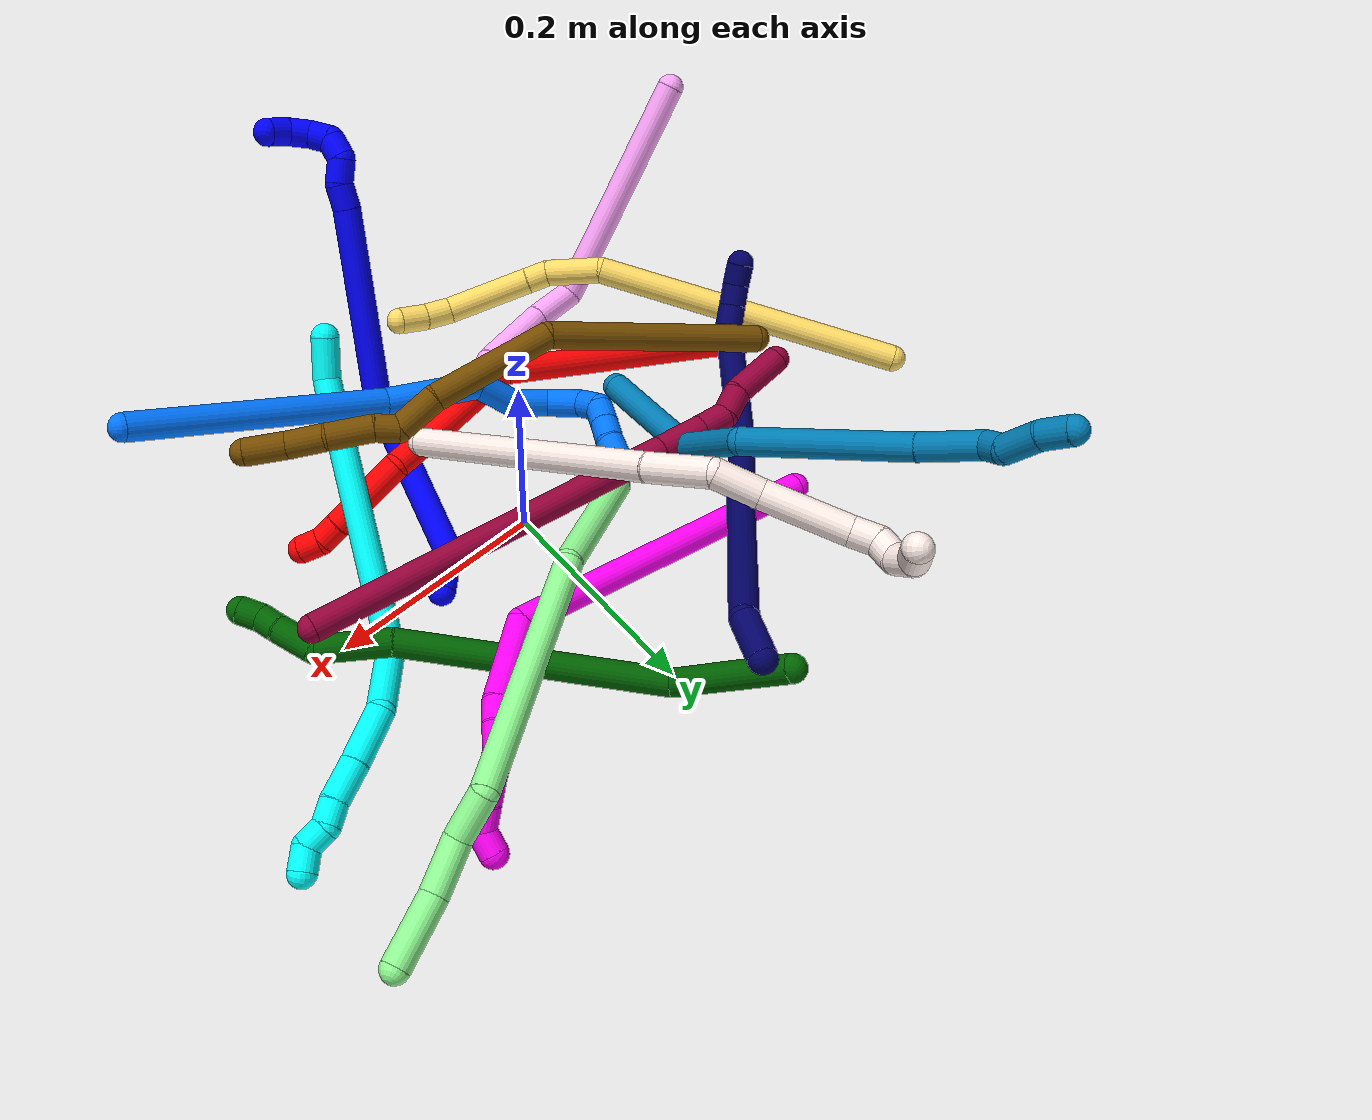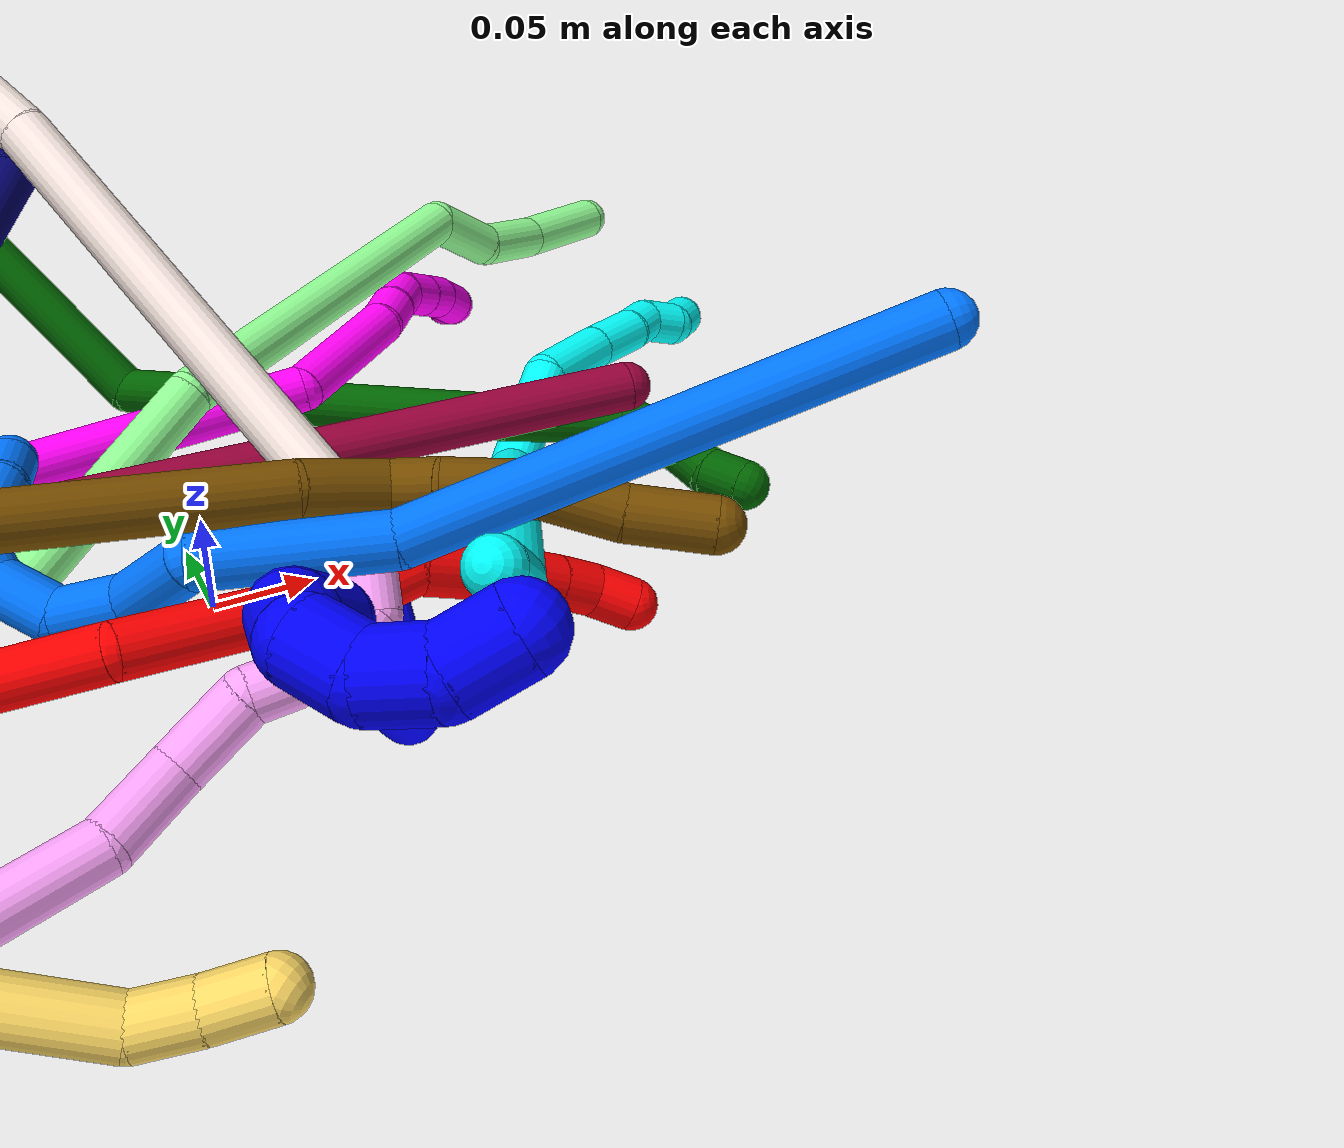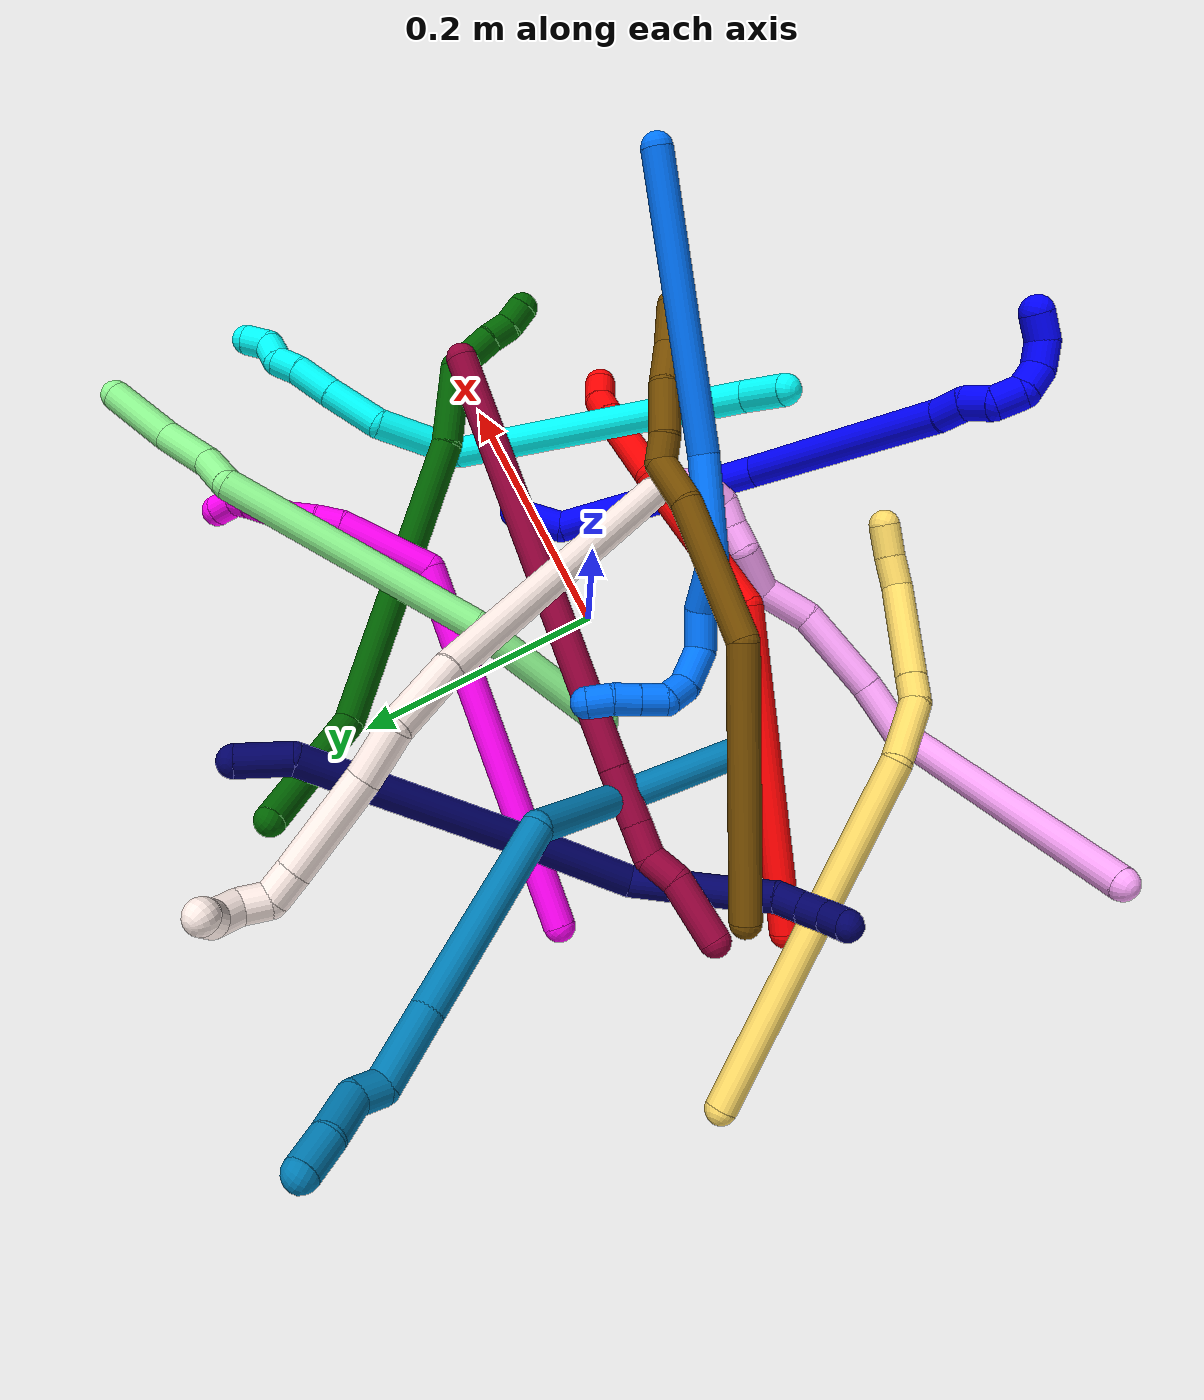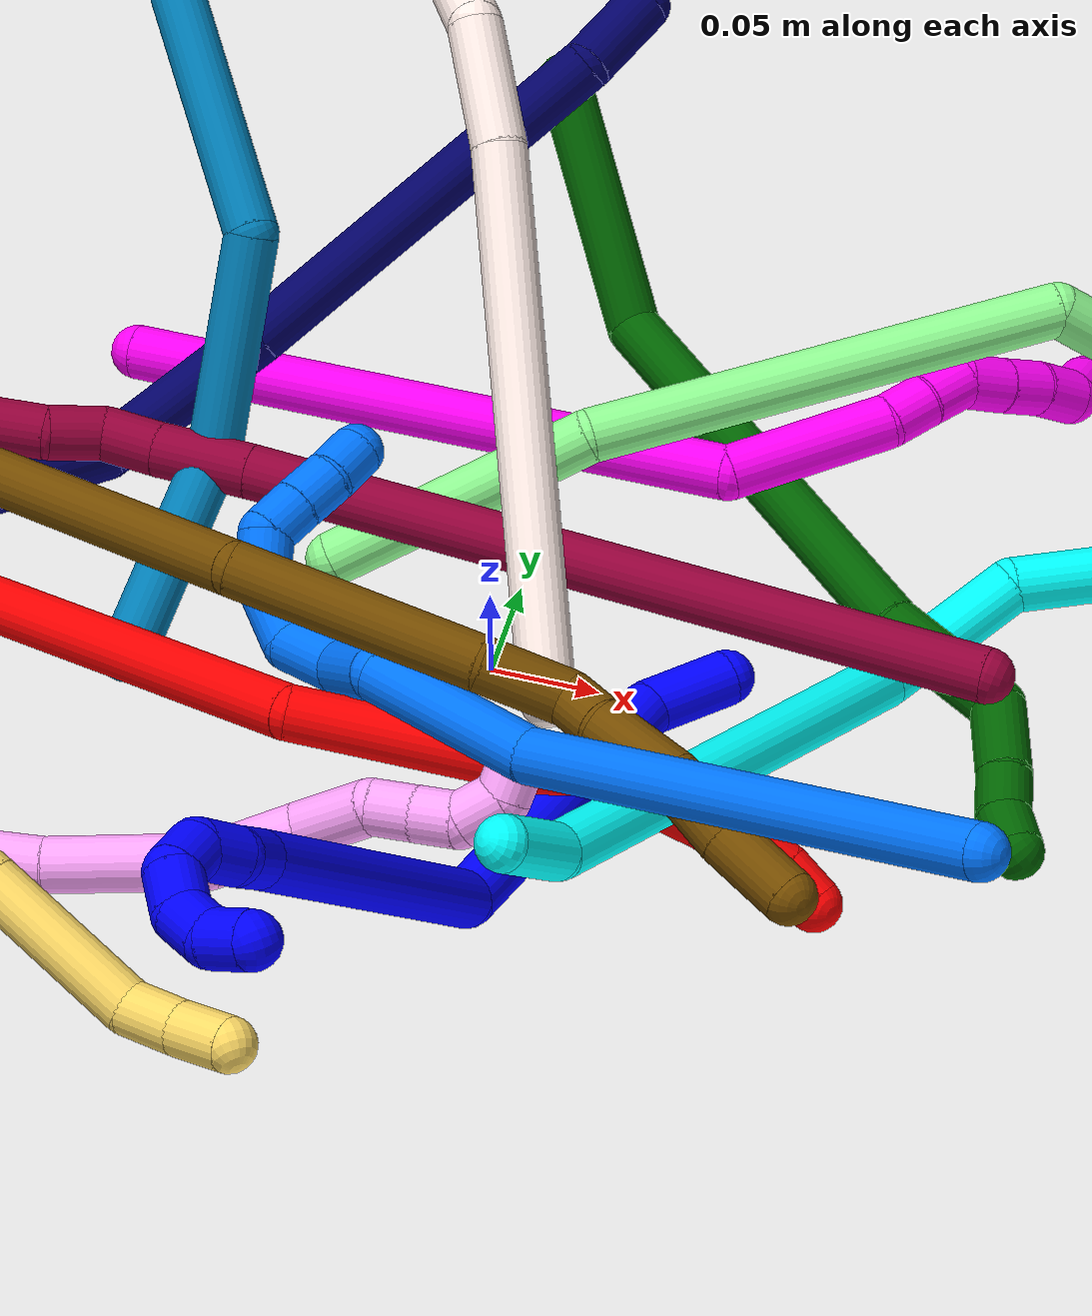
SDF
<sdf version="1.7">
 <world name="default">
  <plugin name="TubeGeneratorPlugin" filename="libtube_generator_plugin.so"/>
  <model name="photoneo_s_sensor">
   <static>1</static>
   <pose>0 0 2 1.57079 1.57079 3.14159</pose>
   <link name="link">
    <inertial><mass>0.1</mass></inertial>
    <sensor name="sensor" type="depth">
     <update_rate>30</update_rate>
     <camera>
      <horizontal_fov>1.22</horizontal_fov>
      <image><width>1920</width><height>1200</height><format>B8G8R8</format></image>
      <clip><near>0.1</near><far>4</far></clip>
      <depth_camera><output>points</output></depth_camera>
     </camera>
     <plugin name="camera_plugin" filename="libgazebo_ros_depth_camera.so">
      <baseline>0.2</baseline>
      <alwaysOn>1</alwaysOn>
      <updateRate>0.0</updateRate>
      <cameraName>camera_ir</cameraName>
      <imageTopicName>/camera/color/image_raw</imageTopicName>
      <cameraInfoTopicName>/camera/color/camera_info</cameraInfoTopicName>
      <depthImageTopicName>/camera/depth/image_raw</depthImageTopicName>
      <depthImageCameraInfoTopicName>/camera/depth/camera_info</depthImageCameraInfoTopicName>
      <pointCloudTopicName>/camera/depth/points</pointCloudTopicName>
      <frameName>fr_optical</frameName>
      <pointCloudCutoff>0.1</pointCloudCutoff>
      <pointCloudCutoffMax>2.0</pointCloudCutoffMax>
      <distortionK1>0</distortionK1>
      <distortionK2>0</distortionK2>
      <distortionK3>0</distortionK3>
      <distortionT1>0</distortionT1>
      <distortionT2>0</distortionT2>
      <CxPrime>0</CxPrime>
      <Cx>0</Cx>
      <Cy>0</Cy>
      <focalLength>0</focalLength>
      <hackBaseline>0</hackBaseline>
     </plugin>
    </sensor>
   </link>
  </model>
  <gravity>0 0 -9.8</gravity>
  <magnetic_field>6e-06 2.3e-05 -4.2e-05</magnetic_field>
  <atmosphere type="adiabatic"/>
  <physics name="default_physics" default="0" type="ode">
   <max_step_size>0.003</max_step_size>
   <real_time_factor>1</real_time_factor>
   <real_time_update_rate>1000</real_time_update_rate>
   <max_contacts>10000</max_contacts>
   <ode>
    <solver>
     <type>quick</type>
     <iters>100</iters>
     <sor>1.3</sor>
     <use_dynamic_moi_rescaling>0</use_dynamic_moi_rescaling>
    </solver>
    <constraints>
     <contact_max_correcting_vel>0</contact_max_correcting_vel>
     <contact_surface_layer>0.001</contact_surface_layer>
     <cfm>0</cfm>
     <erp>0.2</erp>
    </constraints>
   </ode>
  </physics>
  <scene><ambient>0.4 0.4 0.4 1</ambient><background>0.7 0.7 0.7 1</background><shadows>0</shadows></scene>
  <audio><device>default</device></audio>
  <spherical_coordinates>
   <surface_model>EARTH_WGS84</surface_model>
   <latitude_deg>0</latitude_deg>
   <longitude_deg>0</longitude_deg>
   <elevation>0</elevation>
   <heading_deg>0</heading_deg>
  </spherical_coordinates>
  <model name="bin">
   <static>1</static>
   <link name="bottom">
    <collision name="collision-bottom">
     <pose>0 0 -0.01 0 -0 0</pose>
     <geometry><box><size>0.8 0.6 0.02</size></box></geometry>
     <surface>
      <friction><ode><mu>100</mu><mu2>100</mu2></ode></friction>
      <contact><collide_bitmask>65535</collide_bitmask></contact>
     </surface>
    </collision>
   </link>
   <link name="west_wall">
    <collision name="collision-west_wall">
     <pose>-0.41 0 0.1 0 -0 0</pose>
     <geometry><box><size>0.02 0.6 0.2</size></box></geometry>
     <surface>
      <friction><ode><mu>100</mu><mu2>100</mu2></ode></friction>
      <contact><collide_bitmask>65535</collide_bitmask></contact>
     </surface>
    </collision>
   </link>
   <link name="east_wall">
    <collision name="collision-east_wall">
     <pose>0.41 0 0.1 0 -0 0</pose>
     <geometry><box><size>0.02 0.6 0.2</size></box></geometry>
     <surface>
      <friction><ode><mu>100</mu><mu2>100</mu2></ode></friction>
      <contact><collide_bitmask>65535</collide_bitmask></contact>
     </surface>
    </collision>
   </link>
   <link name="south_wall">
    <collision name="collision-south_wall">
     <pose>0 -0.31 0.1 0 -0 0</pose>
     <geometry><box><size>0.8 0.02 0.2</size></box></geometry>
     <surface>
      <friction><ode><mu>100</mu><mu2>100</mu2></ode></friction>
      <contact><collide_bitmask>65535</collide_bitmask></contact>
     </surface>
    </collision>
   </link>
   <link name="north_wall">
    <collision name="collision-north_wall">
     <pose>0 0.31 0.1 0 -0 0</pose>
     <geometry><box><size>0.8 0.02 0.2</size></box></geometry>
     <surface>
      <friction><ode><mu>100</mu><mu2>100</mu2></ode></friction>
      <contact><collide_bitmask>65535</collide_bitmask></contact>
     </surface>
    </collision>
   </link>
  </model>
  <model name="1">
   <static>0</static>
   <link name="1">
    <collision name="collision-cylinder-e_1_1_4">
     <pose>3e-06 3.3e-05 0.020058 -0.001623 0.000137 0</pose>
     <geometry><cylinder><radius>0.0125</radius><length>0.040116</length></cylinder></geometry>
     <surface>
      <friction><ode><mu>1.16</mu><mu2>1.16</mu2><slip1>0</slip1><slip2>0</slip2></ode></friction>
      <contact><ode><kp>1e+06</kp><kd>1</kd><max_vel>0</max_vel><min_depth>0.001</min_depth></ode></contact>
     </surface>
    </collision>
    <visual name="visual-cylinder-e_1_1_4">
     <pose>3e-06 3.3e-05 0.020058 -0.001623 0.000137 0</pose>
     <geometry><cylinder><radius>0.0125</radius><length>0.040116</length></cylinder></geometry>
     <material><ambient>0 0 1 1</ambient></material>
    </visual>
    <collision name="collision-cylinder-e_2_4_5">
     <pose>-0.021767 -0.037509 0.108158 0.504546 -0.273118 -0.070811</pose>
     <geometry><cylinder><radius>0.0125</radius><length>0.16144</length></cylinder></geometry>
     <surface>
      <friction><ode><mu>1.16</mu><mu2>1.16</mu2><slip1>0</slip1><slip2>0</slip2></ode></friction>
      <contact><ode><kp>1e+06</kp><kd>1</kd><max_vel>0</max_vel><min_depth>0.001</min_depth></ode></contact>
     </surface>
    </collision>
    <visual name="visual-cylinder-e_2_4_5">
     <pose>-0.021767 -0.037509 0.108158 0.504546 -0.273118 -0.070811</pose>
     <geometry><cylinder><radius>0.0125</radius><length>0.16144</length></cylinder></geometry>
     <material><ambient>0 0 1 1</ambient></material>
    </visual>
    <collision name="collision-cylinder-e_3_5_6">
     <pose>-0.016321 -0.132646 0.234787 0.776579 0.320016 0.131842</pose>
     <geometry><cylinder><radius>0.0125</radius><length>0.173051</length></cylinder></geometry>
     <surface>
      <friction><ode><mu>1.16</mu><mu2>1.16</mu2><slip1>0</slip1><slip2>0</slip2></ode></friction>
      <contact><ode><kp>1e+06</kp><kd>1</kd><max_vel>0</max_vel><min_depth>0.001</min_depth></ode></contact>
     </surface>
    </collision>
    <visual name="visual-cylinder-e_3_5_6">
     <pose>-0.016321 -0.132646 0.234787 0.776579 0.320016 0.131842</pose>
     <geometry><cylinder><radius>0.0125</radius><length>0.173051</length></cylinder></geometry>
     <material><ambient>0 0 1 1</ambient></material>
    </visual>
    <collision name="collision-cylinder-e_4_6_7">
     <pose>0.013503 -0.198734 0.30025 0.892043 0.233467 0.112027</pose>
     <geometry><cylinder><radius>0.0125</radius><length>0.022518</length></cylinder></geometry>
     <surface>
      <friction><ode><mu>1.16</mu><mu2>1.16</mu2><slip1>0</slip1><slip2>0</slip2></ode></friction>
      <contact><ode><kp>1e+06</kp><kd>1</kd><max_vel>0</max_vel><min_depth>0.001</min_depth></ode></contact>
     </surface>
    </collision>
    <visual name="visual-cylinder-e_4_6_7">
     <pose>0.013503 -0.198734 0.30025 0.892043 0.233467 0.112027</pose>
     <geometry><cylinder><radius>0.0125</radius><length>0.022518</length></cylinder></geometry>
     <material><ambient>0 0 1 1</ambient></material>
    </visual>
    <collision name="collision-cylinder-e_5_7_8">
     <pose>0.020794 -0.212041 0.315716 0.508005 0.444837 0.117292</pose>
     <geometry><cylinder><radius>0.0125</radius><length>0.02178</length></cylinder></geometry>
     <surface>
      <friction><ode><mu>1.16</mu><mu2>1.16</mu2><slip1>0</slip1><slip2>0</slip2></ode></friction>
      <contact><ode><kp>1e+06</kp><kd>1</kd><max_vel>0</max_vel><min_depth>0.001</min_depth></ode></contact>
     </surface>
    </collision>
    <visual name="visual-cylinder-e_5_7_8">
     <pose>0.020794 -0.212041 0.315716 0.508005 0.444837 0.117292</pose>
     <geometry><cylinder><radius>0.0125</radius><length>0.02178</length></cylinder></geometry>
     <material><ambient>0 0 1 1</ambient></material>
    </visual>
    <collision name="collision-cylinder-e_6_8_9">
     <pose>0.022891 -0.22286 0.332376 0.642206 -0.251388 -0.084009</pose>
     <geometry><cylinder><radius>0.0125</radius><length>0.020814</length></cylinder></geometry>
     <surface>
      <friction><ode><mu>1.16</mu><mu2>1.16</mu2><slip1>0</slip1><slip2>0</slip2></ode></friction>
      <contact><ode><kp>1e+06</kp><kd>1</kd><max_vel>0</max_vel><min_depth>0.001</min_depth></ode></contact>
     </surface>
    </collision>
    <visual name="visual-cylinder-e_6_8_9">
     <pose>0.022891 -0.22286 0.332376 0.642206 -0.251388 -0.084009</pose>
     <geometry><cylinder><radius>0.0125</radius><length>0.020814</length></cylinder></geometry>
     <material><ambient>0 0 1 1</ambient></material>
    </visual>
    <collision name="collision-cylinder-e_7_9_10">
     <pose>0.012418 -0.234528 0.343348 1.09517 -0.894101 -0.568838</pose>
     <geometry><cylinder><radius>0.0125</radius><length>0.020226</length></cylinder></geometry>
     <surface>
      <friction><ode><mu>1.16</mu><mu2>1.16</mu2><slip1>0</slip1><slip2>0</slip2></ode></friction>
      <contact><ode><kp>1e+06</kp><kd>1</kd><max_vel>0</max_vel><min_depth>0.001</min_depth></ode></contact>
     </surface>
    </collision>
    <visual name="visual-cylinder-e_7_9_10">
     <pose>0.012418 -0.234528 0.343348 1.09517 -0.894101 -0.568838</pose>
     <geometry><cylinder><radius>0.0125</radius><length>0.020226</length></cylinder></geometry>
     <material><ambient>0 0 1 1</ambient></material>
    </visual>
    <collision name="collision-cylinder-e_8_10_11">
     <pose>-0.001444 -0.248077 0.344923 1.73659 -0.639933 -0.74615</pose>
     <geometry><cylinder><radius>0.0125</radius><length>0.020019</length></cylinder></geometry>
     <surface>
      <friction><ode><mu>1.16</mu><mu2>1.16</mu2><slip1>0</slip1><slip2>0</slip2></ode></friction>
      <contact><ode><kp>1e+06</kp><kd>1</kd><max_vel>0</max_vel><min_depth>0.001</min_depth></ode></contact>
     </surface>
    </collision>
    <visual name="visual-cylinder-e_8_10_11">
     <pose>-0.001444 -0.248077 0.344923 1.73659 -0.639933 -0.74615</pose>
     <geometry><cylinder><radius>0.0125</radius><length>0.020019</length></cylinder></geometry>
     <material><ambient>0 0 1 1</ambient></material>
    </visual>
    <collision name="collision-cylinder-e_9_11_2">
     <pose>-0.010089 -0.264168 0.338454 2.13255 -0.269596 -0.481677</pose>
     <geometry><cylinder><radius>0.0125</radius><length>0.020037</length></cylinder></geometry>
     <surface>
      <friction><ode><mu>1.16</mu><mu2>1.16</mu2><slip1>0</slip1><slip2>0</slip2></ode></friction>
      <contact><ode><kp>1e+06</kp><kd>1</kd><max_vel>0</max_vel><min_depth>0.001</min_depth></ode></contact>
     </surface>
    </collision>
    <visual name="visual-cylinder-e_9_11_2">
     <pose>-0.010089 -0.264168 0.338454 2.13255 -0.269596 -0.481677</pose>
     <geometry><cylinder><radius>0.0125</radius><length>0.020037</length></cylinder></geometry>
     <material><ambient>0 0 1 1</ambient></material>
    </visual>
    <collision name="collision-sphere-2">
     <pose>-0.012758 -0.272341 0.33331 0 -0 0</pose>
     <geometry><sphere><radius>0.0125</radius></sphere></geometry>
     <surface>
      <friction><ode><mu>1.16</mu><mu2>1.16</mu2><slip1>0</slip1><slip2>0</slip2></ode></friction>
      <contact><ode><kp>1e+06</kp><kd>1</kd><max_vel>0</max_vel><min_depth>0.001</min_depth></ode></contact>
     </surface>
    </collision>
    <visual name="visual-sphere-2">
     <pose>-0.012758 -0.272341 0.33331 0 -0 0</pose>
     <geometry><sphere><radius>0.0125</radius></sphere></geometry>
     <material><ambient>0 0 1 1</ambient></material>
    </visual>
    <collision name="collision-sphere-11">
     <pose>-0.007421 -0.255996 0.343598 0 -0 0</pose>
     <geometry><sphere><radius>0.0125</radius></sphere></geometry>
     <surface>
      <friction><ode><mu>1.16</mu><mu2>1.16</mu2><slip1>0</slip1><slip2>0</slip2></ode></friction>
      <contact><ode><kp>1e+06</kp><kd>1</kd><max_vel>0</max_vel><min_depth>0.001</min_depth></ode></contact>
     </surface>
    </collision>
    <visual name="visual-sphere-11">
     <pose>-0.007421 -0.255996 0.343598 0 -0 0</pose>
     <geometry><sphere><radius>0.0125</radius></sphere></geometry>
     <material><ambient>0 0 1 1</ambient></material>
    </visual>
    <collision name="collision-sphere-10">
     <pose>0.004534 -0.240158 0.346248 0 -0 0</pose>
     <geometry><sphere><radius>0.0125</radius></sphere></geometry>
     <surface>
      <friction><ode><mu>1.16</mu><mu2>1.16</mu2><slip1>0</slip1><slip2>0</slip2></ode></friction>
      <contact><ode><kp>1e+06</kp><kd>1</kd><max_vel>0</max_vel><min_depth>0.001</min_depth></ode></contact>
     </surface>
    </collision>
    <visual name="visual-sphere-10">
     <pose>0.004534 -0.240158 0.346248 0 -0 0</pose>
     <geometry><sphere><radius>0.0125</radius></sphere></geometry>
     <material><ambient>0 0 1 1</ambient></material>
    </visual>
    <collision name="collision-sphere-9">
     <pose>0.020303 -0.228898 0.340448 0 -0 0</pose>
     <geometry><sphere><radius>0.0125</radius></sphere></geometry>
     <surface>
      <friction><ode><mu>1.16</mu><mu2>1.16</mu2><slip1>0</slip1><slip2>0</slip2></ode></friction>
      <contact><ode><kp>1e+06</kp><kd>1</kd><max_vel>0</max_vel><min_depth>0.001</min_depth></ode></contact>
     </surface>
    </collision>
    <visual name="visual-sphere-9">
     <pose>0.020303 -0.228898 0.340448 0 -0 0</pose>
     <geometry><sphere><radius>0.0125</radius></sphere></geometry>
     <material><ambient>0 0 1 1</ambient></material>
    </visual>
    <collision name="collision-sphere-4">
     <pose>6e-06 6.5e-05 0.040115 0 -0 0</pose>
     <geometry><sphere><radius>0.0125</radius></sphere></geometry>
     <surface>
      <friction><ode><mu>1.16</mu><mu2>1.16</mu2><slip1>0</slip1><slip2>0</slip2></ode></friction>
      <contact><ode><kp>1e+06</kp><kd>1</kd><max_vel>0</max_vel><min_depth>0.001</min_depth></ode></contact>
     </surface>
    </collision>
    <visual name="visual-sphere-4">
     <pose>6e-06 6.5e-05 0.040115 0 -0 0</pose>
     <geometry><sphere><radius>0.0125</radius></sphere></geometry>
     <material><ambient>0 0 1 1</ambient></material>
    </visual>
    <collision name="collision-sphere-1">
     <geometry><sphere><radius>0.0125</radius></sphere></geometry>
     <surface>
      <friction><ode><mu>1.16</mu><mu2>1.16</mu2><slip1>0</slip1><slip2>0</slip2></ode></friction>
      <contact><ode><kp>1e+06</kp><kd>1</kd><max_vel>0</max_vel><min_depth>0.001</min_depth></ode></contact>
     </surface>
    </collision>
    <visual name="visual-sphere-1">
     <geometry><sphere><radius>0.0125</radius></sphere></geometry>
     <material><ambient>0 0 1 1</ambient></material>
    </visual>
    <collision name="collision-sphere-8">
     <pose>0.02548 -0.216823 0.324305 0 -0 0</pose>
     <geometry><sphere><radius>0.0125</radius></sphere></geometry>
     <surface>
      <friction><ode><mu>1.16</mu><mu2>1.16</mu2><slip1>0</slip1><slip2>0</slip2></ode></friction>
      <contact><ode><kp>1e+06</kp><kd>1</kd><max_vel>0</max_vel><min_depth>0.001</min_depth></ode></contact>
     </surface>
    </collision>
    <visual name="visual-sphere-8">
     <pose>0.02548 -0.216823 0.324305 0 -0 0</pose>
     <geometry><sphere><radius>0.0125</radius></sphere></geometry>
     <material><ambient>0 0 1 1</ambient></material>
    </visual>
    <collision name="collision-sphere-5">
     <pose>-0.04354 -0.075084 0.176201 0 -0 0</pose>
     <geometry><sphere><radius>0.0125</radius></sphere></geometry>
     <surface>
      <friction><ode><mu>1.16</mu><mu2>1.16</mu2><slip1>0</slip1><slip2>0</slip2></ode></friction>
      <contact><ode><kp>1e+06</kp><kd>1</kd><max_vel>0</max_vel><min_depth>0.001</min_depth></ode></contact>
     </surface>
    </collision>
    <visual name="visual-sphere-5">
     <pose>-0.04354 -0.075084 0.176201 0 -0 0</pose>
     <geometry><sphere><radius>0.0125</radius></sphere></geometry>
     <material><ambient>0 0 1 1</ambient></material>
    </visual>
    <collision name="collision-sphere-6">
     <pose>0.010898 -0.190208 0.293374 0 -0 0</pose>
     <geometry><sphere><radius>0.0125</radius></sphere></geometry>
     <surface>
      <friction><ode><mu>1.16</mu><mu2>1.16</mu2><slip1>0</slip1><slip2>0</slip2></ode></friction>
      <contact><ode><kp>1e+06</kp><kd>1</kd><max_vel>0</max_vel><min_depth>0.001</min_depth></ode></contact>
     </surface>
    </collision>
    <visual name="visual-sphere-6">
     <pose>0.010898 -0.190208 0.293374 0 -0 0</pose>
     <geometry><sphere><radius>0.0125</radius></sphere></geometry>
     <material><ambient>0 0 1 1</ambient></material>
    </visual>
    <collision name="collision-sphere-7">
     <pose>0.016108 -0.207259 0.307127 0 -0 0</pose>
     <geometry><sphere><radius>0.0125</radius></sphere></geometry>
     <surface>
      <friction><ode><mu>1.16</mu><mu2>1.16</mu2><slip1>0</slip1><slip2>0</slip2></ode></friction>
      <contact><ode><kp>1e+06</kp><kd>1</kd><max_vel>0</max_vel><min_depth>0.001</min_depth></ode></contact>
     </surface>
    </collision>
    <visual name="visual-sphere-7">
     <pose>0.016108 -0.207259 0.307127 0 -0 0</pose>
     <geometry><sphere><radius>0.0125</radius></sphere></geometry>
     <material><ambient>0 0 1 1</ambient></material>
    </visual>
    <inertial>
     <pose>-0.01017 -0.115487 0.200165 0 -0 0</pose>
     <mass>0.5</mass>
     <inertia>
      <ixx>0.000798</ixx>
      <ixy>0</ixy>
      <ixz>0</ixz>
      <iyy>0.000657</iyy>
      <iyz>0</iyz>
      <izz>0.00045</izz>
     </inertia>
    </inertial>
   </link>
   <pose>0.104504 0.014117 0.01149 -1.50497 -0.701387 2.30315</pose>
  </model>
  <model name="2">
   <static>0</static>
   <link name="2">
    <collision name="collision-cylinder-e_1_1_4">
     <pose>0.022367 -0.010055 -0.12348 3.06034 0.178619 2.28936</pose>
     <geometry><cylinder><radius>0.0125</radius><length>0.251782</length></cylinder></geometry>
     <surface>
      <friction><ode><mu>1.16</mu><mu2>1.16</mu2><slip1>0</slip1><slip2>0</slip2></ode></friction>
      <contact><ode><kp>1e+06</kp><kd>1</kd><max_vel>0</max_vel><min_depth>0.001</min_depth></ode></contact>
     </surface>
    </collision>
    <visual name="visual-cylinder-e_1_1_4">
     <pose>0.022367 -0.010055 -0.12348 3.06034 0.178619 2.28936</pose>
     <geometry><cylinder><radius>0.0125</radius><length>0.251782</length></cylinder></geometry>
     <material><ambient>1 0 0 1</ambient></material>
    </visual>
    <collision name="collision-cylinder-e_2_4_5">
     <pose>0.081506 -0.02117 -0.286753 3.11496 0.745778 3.07354</pose>
     <geometry><cylinder><radius>0.0125</radius><length>0.108385</length></cylinder></geometry>
     <surface>
      <friction><ode><mu>1.16</mu><mu2>1.16</mu2><slip1>0</slip1><slip2>0</slip2></ode></friction>
      <contact><ode><kp>1e+06</kp><kd>1</kd><max_vel>0</max_vel><min_depth>0.001</min_depth></ode></contact>
     </surface>
    </collision>
    <visual name="visual-cylinder-e_2_4_5">
     <pose>0.081506 -0.02117 -0.286753 3.11496 0.745778 3.07354</pose>
     <geometry><cylinder><radius>0.0125</radius><length>0.108385</length></cylinder></geometry>
     <material><ambient>1 0 0 1</ambient></material>
    </visual>
    <collision name="collision-cylinder-e_3_5_6">
     <pose>0.126254 -0.025073 -0.335954 2.84813 0.681747 2.35204</pose>
     <geometry><cylinder><radius>0.0125</radius><length>0.025313</length></cylinder></geometry>
     <surface>
      <friction><ode><mu>1.16</mu><mu2>1.16</mu2><slip1>0</slip1><slip2>0</slip2></ode></friction>
      <contact><ode><kp>1e+06</kp><kd>1</kd><max_vel>0</max_vel><min_depth>0.001</min_depth></ode></contact>
     </surface>
    </collision>
    <visual name="visual-cylinder-e_3_5_6">
     <pose>0.126254 -0.025073 -0.335954 2.84813 0.681747 2.35204</pose>
     <geometry><cylinder><radius>0.0125</radius><length>0.025313</length></cylinder></geometry>
     <material><ambient>1 0 0 1</ambient></material>
    </visual>
    <collision name="collision-cylinder-e_4_6_7">
     <pose>0.15253 -0.021431 -0.362414 -2.77824 0.786931 -2.30833</pose>
     <geometry><cylinder><radius>0.0125</radius><length>0.051683</length></cylinder></geometry>
     <surface>
      <friction><ode><mu>1.16</mu><mu2>1.16</mu2><slip1>0</slip1><slip2>0</slip2></ode></friction>
      <contact><ode><kp>1e+06</kp><kd>1</kd><max_vel>0</max_vel><min_depth>0.001</min_depth></ode></contact>
     </surface>
    </collision>
    <visual name="visual-cylinder-e_4_6_7">
     <pose>0.15253 -0.021431 -0.362414 -2.77824 0.786931 -2.30833</pose>
     <geometry><cylinder><radius>0.0125</radius><length>0.051683</length></cylinder></geometry>
     <material><ambient>1 0 0 1</ambient></material>
    </visual>
    <collision name="collision-cylinder-e_5_7_8">
     <pose>0.178447 -0.011502 -0.386229 -2.67039 0.787236 -2.09335</pose>
     <geometry><cylinder><radius>0.0125</radius><length>0.021504</length></cylinder></geometry>
     <surface>
      <friction><ode><mu>1.16</mu><mu2>1.16</mu2><slip1>0</slip1><slip2>0</slip2></ode></friction>
      <contact><ode><kp>1e+06</kp><kd>1</kd><max_vel>0</max_vel><min_depth>0.001</min_depth></ode></contact>
     </surface>
    </collision>
    <visual name="visual-cylinder-e_5_7_8">
     <pose>0.178447 -0.011502 -0.386229 -2.67039 0.787236 -2.09335</pose>
     <geometry><cylinder><radius>0.0125</radius><length>0.021504</length></cylinder></geometry>
     <material><ambient>1 0 0 1</ambient></material>
    </visual>
    <collision name="collision-cylinder-e_6_8_9">
     <pose>0.193201 -0.004169 -0.399595 -2.60947 0.749843 -1.93025</pose>
     <geometry><cylinder><radius>0.0125</radius><length>0.020945</length></cylinder></geometry>
     <surface>
      <friction><ode><mu>1.16</mu><mu2>1.16</mu2><slip1>0</slip1><slip2>0</slip2></ode></friction>
      <contact><ode><kp>1e+06</kp><kd>1</kd><max_vel>0</max_vel><min_depth>0.001</min_depth></ode></contact>
     </surface>
    </collision>
    <visual name="visual-cylinder-e_6_8_9">
     <pose>0.193201 -0.004169 -0.399595 -2.60947 0.749843 -1.93025</pose>
     <geometry><cylinder><radius>0.0125</radius><length>0.020945</length></cylinder></geometry>
     <material><ambient>1 0 0 1</ambient></material>
    </visual>
    <collision name="collision-cylinder-e_7_9_2">
     <pose>0.203844 0.004841 -0.414286 -2.57709 0.35113 -1.09797</pose>
     <geometry><cylinder><radius>0.0125</radius><length>0.020388</length></cylinder></geometry>
     <surface>
      <friction><ode><mu>1.16</mu><mu2>1.16</mu2><slip1>0</slip1><slip2>0</slip2></ode></friction>
      <contact><ode><kp>1e+06</kp><kd>1</kd><max_vel>0</max_vel><min_depth>0.001</min_depth></ode></contact>
     </surface>
    </collision>
    <visual name="visual-cylinder-e_7_9_2">
     <pose>0.203844 0.004841 -0.414286 -2.57709 0.35113 -1.09797</pose>
     <geometry><cylinder><radius>0.0125</radius><length>0.020388</length></cylinder></geometry>
     <material><ambient>1 0 0 1</ambient></material>
    </visual>
    <collision name="collision-sphere-2">
     <pose>0.207351 0.009962 -0.422373 0 -0 0</pose>
     <geometry><sphere><radius>0.0125</radius></sphere></geometry>
     <surface>
      <friction><ode><mu>1.16</mu><mu2>1.16</mu2><slip1>0</slip1><slip2>0</slip2></ode></friction>
      <contact><ode><kp>1e+06</kp><kd>1</kd><max_vel>0</max_vel><min_depth>0.001</min_depth></ode></contact>
     </surface>
    </collision>
    <visual name="visual-sphere-2">
     <pose>0.207351 0.009962 -0.422373 0 -0 0</pose>
     <geometry><sphere><radius>0.0125</radius></sphere></geometry>
     <material><ambient>1 0 0 1</ambient></material>
    </visual>
    <collision name="collision-sphere-9">
     <pose>0.200338 -0.00028 -0.406199 0 -0 0</pose>
     <geometry><sphere><radius>0.0125</radius></sphere></geometry>
     <surface>
      <friction><ode><mu>1.16</mu><mu2>1.16</mu2><slip1>0</slip1><slip2>0</slip2></ode></friction>
      <contact><ode><kp>1e+06</kp><kd>1</kd><max_vel>0</max_vel><min_depth>0.001</min_depth></ode></contact>
     </surface>
    </collision>
    <visual name="visual-sphere-9">
     <pose>0.200338 -0.00028 -0.406199 0 -0 0</pose>
     <geometry><sphere><radius>0.0125</radius></sphere></geometry>
     <material><ambient>1 0 0 1</ambient></material>
    </visual>
    <collision name="collision-sphere-4">
     <pose>0.044734 -0.02011 -0.246959 0 -0 0</pose>
     <geometry><sphere><radius>0.0125</radius></sphere></geometry>
     <surface>
      <friction><ode><mu>1.16</mu><mu2>1.16</mu2><slip1>0</slip1><slip2>0</slip2></ode></friction>
      <contact><ode><kp>1e+06</kp><kd>1</kd><max_vel>0</max_vel><min_depth>0.001</min_depth></ode></contact>
     </surface>
    </collision>
    <visual name="visual-sphere-4">
     <pose>0.044734 -0.02011 -0.246959 0 -0 0</pose>
     <geometry><sphere><radius>0.0125</radius></sphere></geometry>
     <material><ambient>1 0 0 1</ambient></material>
    </visual>
    <collision name="collision-sphere-1">
     <geometry><sphere><radius>0.0125</radius></sphere></geometry>
     <surface>
      <friction><ode><mu>1.16</mu><mu2>1.16</mu2><slip1>0</slip1><slip2>0</slip2></ode></friction>
      <contact><ode><kp>1e+06</kp><kd>1</kd><max_vel>0</max_vel><min_depth>0.001</min_depth></ode></contact>
     </surface>
    </collision>
    <visual name="visual-sphere-1">
     <geometry><sphere><radius>0.0125</radius></sphere></geometry>
     <material><ambient>1 0 0 1</ambient></material>
    </visual>
    <collision name="collision-sphere-8">
     <pose>0.186064 -0.008057 -0.392991 0 -0 0</pose>
     <geometry><sphere><radius>0.0125</radius></sphere></geometry>
     <surface>
      <friction><ode><mu>1.16</mu><mu2>1.16</mu2><slip1>0</slip1><slip2>0</slip2></ode></friction>
      <contact><ode><kp>1e+06</kp><kd>1</kd><max_vel>0</max_vel><min_depth>0.001</min_depth></ode></contact>
     </surface>
    </collision>
    <visual name="visual-sphere-8">
     <pose>0.186064 -0.008057 -0.392991 0 -0 0</pose>
     <geometry><sphere><radius>0.0125</radius></sphere></geometry>
     <material><ambient>1 0 0 1</ambient></material>
    </visual>
    <collision name="collision-sphere-5">
     <pose>0.118278 -0.02223 -0.326546 0 -0 0</pose>
     <geometry><sphere><radius>0.0125</radius></sphere></geometry>
     <surface>
      <friction><ode><mu>1.16</mu><mu2>1.16</mu2><slip1>0</slip1><slip2>0</slip2></ode></friction>
      <contact><ode><kp>1e+06</kp><kd>1</kd><max_vel>0</max_vel><min_depth>0.001</min_depth></ode></contact>
     </surface>
    </collision>
    <visual name="visual-sphere-5">
     <pose>0.118278 -0.02223 -0.326546 0 -0 0</pose>
     <geometry><sphere><radius>0.0125</radius></sphere></geometry>
     <material><ambient>1 0 0 1</ambient></material>
    </visual>
    <collision name="collision-sphere-6">
     <pose>0.134229 -0.027915 -0.345361 0 -0 0</pose>
     <geometry><sphere><radius>0.0125</radius></sphere></geometry>
     <surface>
      <friction><ode><mu>1.16</mu><mu2>1.16</mu2><slip1>0</slip1><slip2>0</slip2></ode></friction>
      <contact><ode><kp>1e+06</kp><kd>1</kd><max_vel>0</max_vel><min_depth>0.001</min_depth></ode></contact>
     </surface>
    </collision>
    <visual name="visual-sphere-6">
     <pose>0.134229 -0.027915 -0.345361 0 -0 0</pose>
     <geometry><sphere><radius>0.0125</radius></sphere></geometry>
     <material><ambient>1 0 0 1</ambient></material>
    </visual>
    <collision name="collision-sphere-7">
     <pose>0.170831 -0.014947 -0.379468 0 -0 0</pose>
     <geometry><sphere><radius>0.0125</radius></sphere></geometry>
     <surface>
      <friction><ode><mu>1.16</mu><mu2>1.16</mu2><slip1>0</slip1><slip2>0</slip2></ode></friction>
      <contact><ode><kp>1e+06</kp><kd>1</kd><max_vel>0</max_vel><min_depth>0.001</min_depth></ode></contact>
     </surface>
    </collision>
    <visual name="visual-sphere-7">
     <pose>0.170831 -0.014947 -0.379468 0 -0 0</pose>
     <geometry><sphere><radius>0.0125</radius></sphere></geometry>
     <material><ambient>1 0 0 1</ambient></material>
    </visual>
    <inertial>
     <pose>0.075169 -0.013609 -0.229051 0 -0 0</pose>
     <mass>0.5</mass>
     <inertia>
      <ixx>4.8e-05</ixx>
      <ixy>0</ixy>
      <ixz>0</ixz>
      <iyy>0.002008</iyy>
      <iyz>0</iyz>
      <izz>-0.000255</izz>
     </inertia>
    </inertial>
   </link>
   <pose>-0.290626 -0.018772 0.011495 -1.86363 0.496696 0.87276</pose>
  </model>
  <model name="3">
   <static>0</static>
   <link name="3">
    <collision name="collision-cylinder-e_1_1_4">
     <pose>0.0033 -0.000429 0.01838 0.023314 0.177594 0.002076</pose>
     <geometry><cylinder><radius>0.0125</radius><length>0.037357</length></cylinder></geometry>
     <surface>
      <friction><ode><mu>1.16</mu><mu2>1.16</mu2><slip1>0</slip1><slip2>0</slip2></ode></friction>
      <contact><ode><kp>1e+06</kp><kd>1</kd><max_vel>0</max_vel><min_depth>0.001</min_depth></ode></contact>
     </surface>
    </collision>
    <visual name="visual-cylinder-e_1_1_4">
     <pose>0.0033 -0.000429 0.01838 0.023314 0.177594 0.002076</pose>
     <geometry><cylinder><radius>0.0125</radius><length>0.037357</length></cylinder></geometry>
     <material><ambient>0.003922 1 0.996078 1</ambient></material>
    </visual>
    <collision name="collision-cylinder-e_2_4_5">
     <pose>0.053034 0.037215 0.143227 -0.343429 0.389668 -0.068419</pose>
     <geometry><cylinder><radius>0.0125</radius><length>0.244466</length></cylinder></geometry>
     <surface>
      <friction><ode><mu>1.16</mu><mu2>1.16</mu2><slip1>0</slip1><slip2>0</slip2></ode></friction>
      <contact><ode><kp>1e+06</kp><kd>1</kd><max_vel>0</max_vel><min_depth>0.001</min_depth></ode></contact>
     </surface>
    </collision>
    <visual name="visual-cylinder-e_2_4_5">
     <pose>0.053034 0.037215 0.143227 -0.343429 0.389668 -0.068419</pose>
     <geometry><cylinder><radius>0.0125</radius><length>0.244466</length></cylinder></geometry>
     <material><ambient>0.003922 1 0.996078 1</ambient></material>
    </visual>
    <collision name="collision-cylinder-e_3_5_6">
     <pose>0.100447 0.10574 0.267527 -1.04102 0.027748 -0.015907</pose>
     <geometry><cylinder><radius>0.0125</radius><length>0.070606</length></cylinder></geometry>
     <surface>
      <friction><ode><mu>1.16</mu><mu2>1.16</mu2><slip1>0</slip1><slip2>0</slip2></ode></friction>
      <contact><ode><kp>1e+06</kp><kd>1</kd><max_vel>0</max_vel><min_depth>0.001</min_depth></ode></contact>
     </surface>
    </collision>
    <visual name="visual-cylinder-e_3_5_6">
     <pose>0.100447 0.10574 0.267527 -1.04102 0.027748 -0.015907</pose>
     <geometry><cylinder><radius>0.0125</radius><length>0.070606</length></cylinder></geometry>
     <material><ambient>0.003922 1 0.996078 1</ambient></material>
    </visual>
    <collision name="collision-cylinder-e_4_6_7">
     <pose>0.094881 0.149749 0.304574 -0.614461 -0.271494 0.086618</pose>
     <geometry><cylinder><radius>0.0125</radius><length>0.048817</length></cylinder></geometry>
     <surface>
      <friction><ode><mu>1.16</mu><mu2>1.16</mu2><slip1>0</slip1><slip2>0</slip2></ode></friction>
      <contact><ode><kp>1e+06</kp><kd>1</kd><max_vel>0</max_vel><min_depth>0.001</min_depth></ode></contact>
     </surface>
    </collision>
    <visual name="visual-cylinder-e_4_6_7">
     <pose>0.094881 0.149749 0.304574 -0.614461 -0.271494 0.086618</pose>
     <geometry><cylinder><radius>0.0125</radius><length>0.048817</length></cylinder></geometry>
     <material><ambient>0.003922 1 0.996078 1</ambient></material>
    </visual>
    <collision name="collision-cylinder-e_5_7_8">
     <pose>0.082827 0.172712 0.337911 -0.587591 -0.313889 0.095682</pose>
     <geometry><cylinder><radius>0.0125</radius><length>0.035682</length></cylinder></geometry>
     <surface>
      <friction><ode><mu>1.16</mu><mu2>1.16</mu2><slip1>0</slip1><slip2>0</slip2></ode></friction>
      <contact><ode><kp>1e+06</kp><kd>1</kd><max_vel>0</max_vel><min_depth>0.001</min_depth></ode></contact>
     </surface>
    </collision>
    <visual name="visual-cylinder-e_5_7_8">
     <pose>0.082827 0.172712 0.337911 -0.587591 -0.313889 0.095682</pose>
     <geometry><cylinder><radius>0.0125</radius><length>0.035682</length></cylinder></geometry>
     <material><ambient>0.003922 1 0.996078 1</ambient></material>
    </visual>
    <collision name="collision-cylinder-e_6_8_9">
     <pose>0.075957 0.18764 0.360618 -0.571567 -0.132585 0.039009</pose>
     <geometry><cylinder><radius>0.0125</radius><length>0.020593</length></cylinder></geometry>
     <surface>
      <friction><ode><mu>1.16</mu><mu2>1.16</mu2><slip1>0</slip1><slip2>0</slip2></ode></friction>
      <contact><ode><kp>1e+06</kp><kd>1</kd><max_vel>0</max_vel><min_depth>0.001</min_depth></ode></contact>
     </surface>
    </collision>
    <visual name="visual-cylinder-e_6_8_9">
     <pose>0.075957 0.18764 0.360618 -0.571567 -0.132585 0.039009</pose>
     <geometry><cylinder><radius>0.0125</radius><length>0.020593</length></cylinder></geometry>
     <material><ambient>0.003922 1 0.996078 1</ambient></material>
    </visual>
    <collision name="collision-cylinder-e_7_9_10">
     <pose>0.06826 0.194653 0.377554 -0.17678 -0.641438 0.058861</pose>
     <geometry><cylinder><radius>0.0125</radius><length>0.021178</length></cylinder></geometry>
     <surface>
      <friction><ode><mu>1.16</mu><mu2>1.16</mu2><slip1>0</slip1><slip2>0</slip2></ode></friction>
      <contact><ode><kp>1e+06</kp><kd>1</kd><max_vel>0</max_vel><min_depth>0.001</min_depth></ode></contact>
     </surface>
    </collision>
    <visual name="visual-cylinder-e_7_9_10">
     <pose>0.06826 0.194653 0.377554 -0.17678 -0.641438 0.058861</pose>
     <geometry><cylinder><radius>0.0125</radius><length>0.021178</length></cylinder></geometry>
     <material><ambient>0.003922 1 0.996078 1</ambient></material>
    </visual>
    <collision name="collision-cylinder-e_8_10_2">
     <pose>0.062049 0.20115 0.395306 -0.489263 0.011709 -0.002923</pose>
     <geometry><cylinder><radius>0.0125</radius><length>0.0213</length></cylinder></geometry>
     <surface>
      <friction><ode><mu>1.16</mu><mu2>1.16</mu2><slip1>0</slip1><slip2>0</slip2></ode></friction>
      <contact><ode><kp>1e+06</kp><kd>1</kd><max_vel>0</max_vel><min_depth>0.001</min_depth></ode></contact>
     </surface>
    </collision>
    <visual name="visual-cylinder-e_8_10_2">
     <pose>0.062049 0.20115 0.395306 -0.489263 0.011709 -0.002923</pose>
     <geometry><cylinder><radius>0.0125</radius><length>0.0213</length></cylinder></geometry>
     <material><ambient>0.003922 1 0.996078 1</ambient></material>
    </visual>
    <collision name="collision-sphere-2">
     <pose>0.062173 0.206155 0.404706 0 -0 0</pose>
     <geometry><sphere><radius>0.0125</radius></sphere></geometry>
     <surface>
      <friction><ode><mu>1.16</mu><mu2>1.16</mu2><slip1>0</slip1><slip2>0</slip2></ode></friction>
      <contact><ode><kp>1e+06</kp><kd>1</kd><max_vel>0</max_vel><min_depth>0.001</min_depth></ode></contact>
     </surface>
    </collision>
    <visual name="visual-sphere-2">
     <pose>0.062173 0.206155 0.404706 0 -0 0</pose>
     <geometry><sphere><radius>0.0125</radius></sphere></geometry>
     <material><ambient>0.003922 1 0.996078 1</ambient></material>
    </visual>
    <collision name="collision-sphere-10">
     <pose>0.061924 0.196146 0.385906 0 -0 0</pose>
     <geometry><sphere><radius>0.0125</radius></sphere></geometry>
     <surface>
      <friction><ode><mu>1.16</mu><mu2>1.16</mu2><slip1>0</slip1><slip2>0</slip2></ode></friction>
      <contact><ode><kp>1e+06</kp><kd>1</kd><max_vel>0</max_vel><min_depth>0.001</min_depth></ode></contact>
     </surface>
    </collision>
    <visual name="visual-sphere-10">
     <pose>0.061924 0.196146 0.385906 0 -0 0</pose>
     <geometry><sphere><radius>0.0125</radius></sphere></geometry>
     <material><ambient>0.003922 1 0.996078 1</ambient></material>
    </visual>
    <collision name="collision-sphere-9">
     <pose>0.074596 0.193161 0.369202 0 -0 0</pose>
     <geometry><sphere><radius>0.0125</radius></sphere></geometry>
     <surface>
      <friction><ode><mu>1.16</mu><mu2>1.16</mu2><slip1>0</slip1><slip2>0</slip2></ode></friction>
      <contact><ode><kp>1e+06</kp><kd>1</kd><max_vel>0</max_vel><min_depth>0.001</min_depth></ode></contact>
     </surface>
    </collision>
    <visual name="visual-sphere-9">
     <pose>0.074596 0.193161 0.369202 0 -0 0</pose>
     <geometry><sphere><radius>0.0125</radius></sphere></geometry>
     <material><ambient>0.003922 1 0.996078 1</ambient></material>
    </visual>
    <collision name="collision-sphere-4">
     <pose>0.0066 -0.000857 0.03676 0 -0 0</pose>
     <geometry><sphere><radius>0.0125</radius></sphere></geometry>
     <surface>
      <friction><ode><mu>1.16</mu><mu2>1.16</mu2><slip1>0</slip1><slip2>0</slip2></ode></friction>
      <contact><ode><kp>1e+06</kp><kd>1</kd><max_vel>0</max_vel><min_depth>0.001</min_depth></ode></contact>
     </surface>
    </collision>
    <visual name="visual-sphere-4">
     <pose>0.0066 -0.000857 0.03676 0 -0 0</pose>
     <geometry><sphere><radius>0.0125</radius></sphere></geometry>
     <material><ambient>0.003922 1 0.996078 1</ambient></material>
    </visual>
    <collision name="collision-sphere-1">
     <geometry><sphere><radius>0.0125</radius></sphere></geometry>
     <surface>
      <friction><ode><mu>1.16</mu><mu2>1.16</mu2><slip1>0</slip1><slip2>0</slip2></ode></friction>
      <contact><ode><kp>1e+06</kp><kd>1</kd><max_vel>0</max_vel><min_depth>0.001</min_depth></ode></contact>
     </surface>
    </collision>
    <visual name="visual-sphere-1">
     <geometry><sphere><radius>0.0125</radius></sphere></geometry>
     <material><ambient>0.003922 1 0.996078 1</ambient></material>
    </visual>
    <collision name="collision-sphere-8">
     <pose>0.077318 0.182119 0.352034 0 -0 0</pose>
     <geometry><sphere><radius>0.0125</radius></sphere></geometry>
     <surface>
      <friction><ode><mu>1.16</mu><mu2>1.16</mu2><slip1>0</slip1><slip2>0</slip2></ode></friction>
      <contact><ode><kp>1e+06</kp><kd>1</kd><max_vel>0</max_vel><min_depth>0.001</min_depth></ode></contact>
     </surface>
    </collision>
    <visual name="visual-sphere-8">
     <pose>0.077318 0.182119 0.352034 0 -0 0</pose>
     <geometry><sphere><radius>0.0125</radius></sphere></geometry>
     <material><ambient>0.003922 1 0.996078 1</ambient></material>
    </visual>
    <collision name="collision-sphere-5">
     <pose>0.099468 0.075288 0.249694 0 -0 0</pose>
     <geometry><sphere><radius>0.0125</radius></sphere></geometry>
     <surface>
      <friction><ode><mu>1.16</mu><mu2>1.16</mu2><slip1>0</slip1><slip2>0</slip2></ode></friction>
      <contact><ode><kp>1e+06</kp><kd>1</kd><max_vel>0</max_vel><min_depth>0.001</min_depth></ode></contact>
     </surface>
    </collision>
    <visual name="visual-sphere-5">
     <pose>0.099468 0.075288 0.249694 0 -0 0</pose>
     <geometry><sphere><radius>0.0125</radius></sphere></geometry>
     <material><ambient>0.003922 1 0.996078 1</ambient></material>
    </visual>
    <collision name="collision-sphere-6">
     <pose>0.101427 0.136192 0.285361 0 -0 0</pose>
     <geometry><sphere><radius>0.0125</radius></sphere></geometry>
     <surface>
      <friction><ode><mu>1.16</mu><mu2>1.16</mu2><slip1>0</slip1><slip2>0</slip2></ode></friction>
      <contact><ode><kp>1e+06</kp><kd>1</kd><max_vel>0</max_vel><min_depth>0.001</min_depth></ode></contact>
     </surface>
    </collision>
    <visual name="visual-sphere-6">
     <pose>0.101427 0.136192 0.285361 0 -0 0</pose>
     <geometry><sphere><radius>0.0125</radius></sphere></geometry>
     <material><ambient>0.003922 1 0.996078 1</ambient></material>
    </visual>
    <collision name="collision-sphere-7">
     <pose>0.088335 0.163305 0.323788 0 -0 0</pose>
     <geometry><sphere><radius>0.0125</radius></sphere></geometry>
     <surface>
      <friction><ode><mu>1.16</mu><mu2>1.16</mu2><slip1>0</slip1><slip2>0</slip2></ode></friction>
      <contact><ode><kp>1e+06</kp><kd>1</kd><max_vel>0</max_vel><min_depth>0.001</min_depth></ode></contact>
     </surface>
    </collision>
    <visual name="visual-sphere-7">
     <pose>0.088335 0.163305 0.323788 0 -0 0</pose>
     <geometry><sphere><radius>0.0125</radius></sphere></geometry>
     <material><ambient>0.003922 1 0.996078 1</ambient></material>
    </visual>
    <inertial>
     <pose>0.064198 0.084584 0.210716 0 -0 0</pose>
     <mass>0.5</mass>
     <inertia>
      <ixx>0.001119</ixx>
      <ixy>0</ixy>
      <ixz>0</ixz>
      <iyy>0.001143</iyy>
      <iyz>0</iyz>
      <izz>-0.000851</izz>
     </inertia>
    </inertial>
   </link>
   <pose>0.062254 -0.19583 0.130131 2.28757 0.122854 2.34502</pose>
  </model>
  <model name="4">
   <static>0</static>
   <link name="4">
    <collision name="collision-cylinder-e_1_1_4">
     <pose>0.017751 0.008424 -0.108234 -3.06392 0.162075 -2.24909</pose>
     <geometry><cylinder><radius>0.0125</radius><length>0.220007</length></cylinder></geometry>
     <surface>
      <friction><ode><mu>1.16</mu><mu2>1.16</mu2><slip1>0</slip1><slip2>0</slip2></ode></friction>
      <contact><ode><kp>1e+06</kp><kd>1</kd><max_vel>0</max_vel><min_depth>0.001</min_depth></ode></contact>
     </surface>
    </collision>
    <visual name="visual-cylinder-e_1_1_4">
     <pose>0.017751 0.008424 -0.108234 -3.06392 0.162075 -2.24909</pose>
     <geometry><cylinder><radius>0.0125</radius><length>0.220007</length></cylinder></geometry>
     <material><ambient>1 0.65098 0.996078 1</ambient></material>
    </visual>
    <collision name="collision-cylinder-e_2_4_5">
     <pose>0.052619 0.021267 -0.229801 -2.82155 0.883674 -2.48394</pose>
     <geometry><cylinder><radius>0.0125</radius><length>0.044284</length></cylinder></geometry>
     <surface>
      <friction><ode><mu>1.16</mu><mu2>1.16</mu2><slip1>0</slip1><slip2>0</slip2></ode></friction>
      <contact><ode><kp>1e+06</kp><kd>1</kd><max_vel>0</max_vel><min_depth>0.001</min_depth></ode></contact>
     </surface>
    </collision>
    <visual name="visual-cylinder-e_2_4_5">
     <pose>0.052619 0.021267 -0.229801 -2.82155 0.883674 -2.48394</pose>
     <geometry><cylinder><radius>0.0125</radius><length>0.044284</length></cylinder></geometry>
     <material><ambient>1 0.65098 0.996078 1</ambient></material>
    </visual>
    <collision name="collision-cylinder-e_3_5_6">
     <pose>0.096786 0.037848 -0.263599 -2.6054 0.849065 -2.04941</pose>
     <geometry><cylinder><radius>0.0125</radius><length>0.072068</length></cylinder></geometry>
     <surface>
      <friction><ode><mu>1.16</mu><mu2>1.16</mu2><slip1>0</slip1><slip2>0</slip2></ode></friction>
      <contact><ode><kp>1e+06</kp><kd>1</kd><max_vel>0</max_vel><min_depth>0.001</min_depth></ode></contact>
     </surface>
    </collision>
    <visual name="visual-cylinder-e_3_5_6">
     <pose>0.096786 0.037848 -0.263599 -2.6054 0.849065 -2.04941</pose>
     <geometry><cylinder><radius>0.0125</radius><length>0.072068</length></cylinder></geometry>
     <material><ambient>1 0.65098 0.996078 1</ambient></material>
    </visual>
    <collision name="collision-cylinder-e_4_6_7">
     <pose>0.135895 0.06347 -0.294251 -2.21862 0.620346 -1.14502</pose>
     <geometry><cylinder><radius>0.0125</radius><length>0.04149</length></cylinder></geometry>
     <surface>
      <friction><ode><mu>1.16</mu><mu2>1.16</mu2><slip1>0</slip1><slip2>0</slip2></ode></friction>
      <contact><ode><kp>1e+06</kp><kd>1</kd><max_vel>0</max_vel><min_depth>0.001</min_depth></ode></contact>
     </surface>
    </collision>
    <visual name="visual-cylinder-e_4_6_7">
     <pose>0.135895 0.06347 -0.294251 -2.21862 0.620346 -1.14502</pose>
     <geometry><cylinder><radius>0.0125</radius><length>0.04149</length></cylinder></geometry>
     <material><ambient>1 0.65098 0.996078 1</ambient></material>
    </visual>
    <collision name="collision-cylinder-e_5_7_8">
     <pose>0.166492 0.083304 -0.305696 -1.76585 1.23365 -1.42391</pose>
     <geometry><cylinder><radius>0.0125</radius><length>0.039288</length></cylinder></geometry>
     <surface>
      <friction><ode><mu>1.16</mu><mu2>1.16</mu2><slip1>0</slip1><slip2>0</slip2></ode></friction>
      <contact><ode><kp>1e+06</kp><kd>1</kd><max_vel>0</max_vel><min_depth>0.001</min_depth></ode></contact>
     </surface>
    </collision>
    <visual name="visual-cylinder-e_5_7_8">
     <pose>0.166492 0.083304 -0.305696 -1.76585 1.23365 -1.42391</pose>
     <geometry><cylinder><radius>0.0125</radius><length>0.039288</length></cylinder></geometry>
     <material><ambient>1 0.65098 0.996078 1</ambient></material>
    </visual>
    <collision name="collision-cylinder-e_6_8_9">
     <pose>0.193544 0.090982 -0.312537 -2.91229 0.978301 -2.71548</pose>
     <geometry><cylinder><radius>0.0125</radius><length>0.020525</length></cylinder></geometry>
     <surface>
      <friction><ode><mu>1.16</mu><mu2>1.16</mu2><slip1>0</slip1><slip2>0</slip2></ode></friction>
      <contact><ode><kp>1e+06</kp><kd>1</kd><max_vel>0</max_vel><min_depth>0.001</min_depth></ode></contact>
     </surface>
    </collision>
    <visual name="visual-cylinder-e_6_8_9">
     <pose>0.193544 0.090982 -0.312537 -2.91229 0.978301 -2.71548</pose>
     <geometry><cylinder><radius>0.0125</radius><length>0.020525</length></cylinder></geometry>
     <material><ambient>1 0.65098 0.996078 1</ambient></material>
    </visual>
    <collision name="collision-cylinder-e_7_9_10">
     <pose>0.211331 0.093038 -0.322435 -2.96891 1.12933 -2.87</pose>
     <geometry><cylinder><radius>0.0125</radius><length>0.020516</length></cylinder></geometry>
     <surface>
      <friction><ode><mu>1.16</mu><mu2>1.16</mu2><slip1>0</slip1><slip2>0</slip2></ode></friction>
      <contact><ode><kp>1e+06</kp><kd>1</kd><max_vel>0</max_vel><min_depth>0.001</min_depth></ode></contact>
     </surface>
    </collision>
    <visual name="visual-cylinder-e_7_9_10">
     <pose>0.211331 0.093038 -0.322435 -2.96891 1.12933 -2.87</pose>
     <geometry><cylinder><radius>0.0125</radius><length>0.020516</length></cylinder></geometry>
     <material><ambient>1 0.65098 0.996078 1</ambient></material>
    </visual>
    <collision name="collision-cylinder-e_8_10_11">
     <pose>0.228487 0.100504 -0.328885 -1.8783 0.841484 -1.0978</pose>
     <geometry><cylinder><radius>0.0125</radius><length>0.021141</length></cylinder></geometry>
     <surface>
      <friction><ode><mu>1.16</mu><mu2>1.16</mu2><slip1>0</slip1><slip2>0</slip2></ode></friction>
      <contact><ode><kp>1e+06</kp><kd>1</kd><max_vel>0</max_vel><min_depth>0.001</min_depth></ode></contact>
     </surface>
    </collision>
    <visual name="visual-cylinder-e_8_10_11">
     <pose>0.228487 0.100504 -0.328885 -1.8783 0.841484 -1.0978</pose>
     <geometry><cylinder><radius>0.0125</radius><length>0.021141</length></cylinder></geometry>
     <material><ambient>1 0.65098 0.996078 1</ambient></material>
    </visual>
    <collision name="collision-cylinder-e_9_11_2">
     <pose>0.239925 0.116452 -0.328015 -1.25654 0.351027 -0.25625</pose>
     <geometry><cylinder><radius>0.0125</radius><length>0.020682</length></cylinder></geometry>
     <surface>
      <friction><ode><mu>1.16</mu><mu2>1.16</mu2><slip1>0</slip1><slip2>0</slip2></ode></friction>
      <contact><ode><kp>1e+06</kp><kd>1</kd><max_vel>0</max_vel><min_depth>0.001</min_depth></ode></contact>
     </surface>
    </collision>
    <visual name="visual-cylinder-e_9_11_2">
     <pose>0.239925 0.116452 -0.328015 -1.25654 0.351027 -0.25625</pose>
     <geometry><cylinder><radius>0.0125</radius><length>0.020682</length></cylinder></geometry>
     <material><ambient>1 0.65098 0.996078 1</ambient></material>
    </visual>
    <collision name="collision-sphere-2">
     <pose>0.243481 0.125687 -0.325014 0 -0 0</pose>
     <geometry><sphere><radius>0.0125</radius></sphere></geometry>
     <surface>
      <friction><ode><mu>1.16</mu><mu2>1.16</mu2><slip1>0</slip1><slip2>0</slip2></ode></friction>
      <contact><ode><kp>1e+06</kp><kd>1</kd><max_vel>0</max_vel><min_depth>0.001</min_depth></ode></contact>
     </surface>
    </collision>
    <visual name="visual-sphere-2">
     <pose>0.243481 0.125687 -0.325014 0 -0 0</pose>
     <geometry><sphere><radius>0.0125</radius></sphere></geometry>
     <material><ambient>1 0.65098 0.996078 1</ambient></material>
    </visual>
    <collision name="collision-sphere-11">
     <pose>0.236369 0.107217 -0.331017 0 -0 0</pose>
     <geometry><sphere><radius>0.0125</radius></sphere></geometry>
     <surface>
      <friction><ode><mu>1.16</mu><mu2>1.16</mu2><slip1>0</slip1><slip2>0</slip2></ode></friction>
      <contact><ode><kp>1e+06</kp><kd>1</kd><max_vel>0</max_vel><min_depth>0.001</min_depth></ode></contact>
     </surface>
    </collision>
    <visual name="visual-sphere-11">
     <pose>0.236369 0.107217 -0.331017 0 -0 0</pose>
     <geometry><sphere><radius>0.0125</radius></sphere></geometry>
     <material><ambient>1 0.65098 0.996078 1</ambient></material>
    </visual>
    <collision name="collision-sphere-10">
     <pose>0.220606 0.093791 -0.326753 0 -0 0</pose>
     <geometry><sphere><radius>0.0125</radius></sphere></geometry>
     <surface>
      <friction><ode><mu>1.16</mu><mu2>1.16</mu2><slip1>0</slip1><slip2>0</slip2></ode></friction>
      <contact><ode><kp>1e+06</kp><kd>1</kd><max_vel>0</max_vel><min_depth>0.001</min_depth></ode></contact>
     </surface>
    </collision>
    <visual name="visual-sphere-10">
     <pose>0.220606 0.093791 -0.326753 0 -0 0</pose>
     <geometry><sphere><radius>0.0125</radius></sphere></geometry>
     <material><ambient>1 0.65098 0.996078 1</ambient></material>
    </visual>
    <collision name="collision-sphere-9">
     <pose>0.202057 0.092285 -0.318118 0 -0 0</pose>
     <geometry><sphere><radius>0.0125</radius></sphere></geometry>
     <surface>
      <friction><ode><mu>1.16</mu><mu2>1.16</mu2><slip1>0</slip1><slip2>0</slip2></ode></friction>
      <contact><ode><kp>1e+06</kp><kd>1</kd><max_vel>0</max_vel><min_depth>0.001</min_depth></ode></contact>
     </surface>
    </collision>
    <visual name="visual-sphere-9">
     <pose>0.202057 0.092285 -0.318118 0 -0 0</pose>
     <geometry><sphere><radius>0.0125</radius></sphere></geometry>
     <material><ambient>1 0.65098 0.996078 1</ambient></material>
    </visual>
    <collision name="collision-sphere-4">
     <pose>0.035502 0.016848 -0.216469 0 -0 0</pose>
     <geometry><sphere><radius>0.0125</radius></sphere></geometry>
     <surface>
      <friction><ode><mu>1.16</mu><mu2>1.16</mu2><slip1>0</slip1><slip2>0</slip2></ode></friction>
      <contact><ode><kp>1e+06</kp><kd>1</kd><max_vel>0</max_vel><min_depth>0.001</min_depth></ode></contact>
     </surface>
    </collision>
    <visual name="visual-sphere-4">
     <pose>0.035502 0.016848 -0.216469 0 -0 0</pose>
     <geometry><sphere><radius>0.0125</radius></sphere></geometry>
     <material><ambient>1 0.65098 0.996078 1</ambient></material>
    </visual>
    <collision name="collision-sphere-1">
     <geometry><sphere><radius>0.0125</radius></sphere></geometry>
     <surface>
      <friction><ode><mu>1.16</mu><mu2>1.16</mu2><slip1>0</slip1><slip2>0</slip2></ode></friction>
      <contact><ode><kp>1e+06</kp><kd>1</kd><max_vel>0</max_vel><min_depth>0.001</min_depth></ode></contact>
     </surface>
    </collision>
    <visual name="visual-sphere-1">
     <geometry><sphere><radius>0.0125</radius></sphere></geometry>
     <material><ambient>1 0.65098 0.996078 1</ambient></material>
    </visual>
    <collision name="collision-sphere-8">
     <pose>0.18503 0.089679 -0.306956 0 -0 0</pose>
     <geometry><sphere><radius>0.0125</radius></sphere></geometry>
     <surface>
      <friction><ode><mu>1.16</mu><mu2>1.16</mu2><slip1>0</slip1><slip2>0</slip2></ode></friction>
      <contact><ode><kp>1e+06</kp><kd>1</kd><max_vel>0</max_vel><min_depth>0.001</min_depth></ode></contact>
     </surface>
    </collision>
    <visual name="visual-sphere-8">
     <pose>0.18503 0.089679 -0.306956 0 -0 0</pose>
     <geometry><sphere><radius>0.0125</radius></sphere></geometry>
     <material><ambient>1 0.65098 0.996078 1</ambient></material>
    </visual>
    <collision name="collision-sphere-5">
     <pose>0.069737 0.025685 -0.243132 0 -0 0</pose>
     <geometry><sphere><radius>0.0125</radius></sphere></geometry>
     <surface>
      <friction><ode><mu>1.16</mu><mu2>1.16</mu2><slip1>0</slip1><slip2>0</slip2></ode></friction>
      <contact><ode><kp>1e+06</kp><kd>1</kd><max_vel>0</max_vel><min_depth>0.001</min_depth></ode></contact>
     </surface>
    </collision>
    <visual name="visual-sphere-5">
     <pose>0.069737 0.025685 -0.243132 0 -0 0</pose>
     <geometry><sphere><radius>0.0125</radius></sphere></geometry>
     <material><ambient>1 0.65098 0.996078 1</ambient></material>
    </visual>
    <collision name="collision-sphere-6">
     <pose>0.123836 0.05001 -0.284065 0 -0 0</pose>
     <geometry><sphere><radius>0.0125</radius></sphere></geometry>
     <surface>
      <friction><ode><mu>1.16</mu><mu2>1.16</mu2><slip1>0</slip1><slip2>0</slip2></ode></friction>
      <contact><ode><kp>1e+06</kp><kd>1</kd><max_vel>0</max_vel><min_depth>0.001</min_depth></ode></contact>
     </surface>
    </collision>
    <visual name="visual-sphere-6">
     <pose>0.123836 0.05001 -0.284065 0 -0 0</pose>
     <geometry><sphere><radius>0.0125</radius></sphere></geometry>
     <material><ambient>1 0.65098 0.996078 1</ambient></material>
    </visual>
    <collision name="collision-sphere-7">
     <pose>0.147954 0.076929 -0.304437 0 -0 0</pose>
     <geometry><sphere><radius>0.0125</radius></sphere></geometry>
     <surface>
      <friction><ode><mu>1.16</mu><mu2>1.16</mu2><slip1>0</slip1><slip2>0</slip2></ode></friction>
      <contact><ode><kp>1e+06</kp><kd>1</kd><max_vel>0</max_vel><min_depth>0.001</min_depth></ode></contact>
     </surface>
    </collision>
    <visual name="visual-sphere-7">
     <pose>0.147954 0.076929 -0.304437 0 -0 0</pose>
     <geometry><sphere><radius>0.0125</radius></sphere></geometry>
     <material><ambient>1 0.65098 0.996078 1</ambient></material>
    </visual>
    <inertial>
     <pose>0.086981 0.039477 -0.207942 0 -0 0</pose>
     <mass>0.5</mass>
     <inertia>
      <ixx>-0.001269</ixx>
      <ixy>0</ixy>
      <ixz>0</ixz>
      <iyy>-9.8e-05</iyy>
      <iyz>0</iyz>
      <izz>-0.000309</izz>
     </inertia>
    </inertial>
   </link>
   <pose>-0.359879 -0.216969 0.152343 0.37008 -0.605317 -0.327565</pose>
  </model>
  <model name="5">
   <static>0</static>
   <link name="5">
    <collision name="collision-cylinder-e_1_1_4">
     <pose>0.013832 -0.050678 0.135735 0.357334 0.095179 0.017201</pose>
     <geometry><cylinder><radius>0.0125</radius><length>0.291092</length></cylinder></geometry>
     <surface>
      <friction><ode><mu>1.16</mu><mu2>1.16</mu2><slip1>0</slip1><slip2>0</slip2></ode></friction>
      <contact><ode><kp>1e+06</kp><kd>1</kd><max_vel>0</max_vel><min_depth>0.001</min_depth></ode></contact>
     </surface>
    </collision>
    <visual name="visual-cylinder-e_1_1_4">
     <pose>0.013832 -0.050678 0.135735 0.357334 0.095179 0.017201</pose>
     <geometry><cylinder><radius>0.0125</radius><length>0.291092</length></cylinder></geometry>
     <material><ambient>1 0.858824 0.4 1</ambient></material>
    </visual>
    <collision name="collision-cylinder-e_2_4_5">
     <pose>0.026048 -0.100336 0.298481 -0.037768 -0.059733 0.001128</pose>
     <geometry><cylinder><radius>0.0125</radius><length>0.054156</length></cylinder></geometry>
     <surface>
      <friction><ode><mu>1.16</mu><mu2>1.16</mu2><slip1>0</slip1><slip2>0</slip2></ode></friction>
      <contact><ode><kp>1e+06</kp><kd>1</kd><max_vel>0</max_vel><min_depth>0.001</min_depth></ode></contact>
     </surface>
    </collision>
    <visual name="visual-cylinder-e_2_4_5">
     <pose>0.026048 -0.100336 0.298481 -0.037768 -0.059733 0.001128</pose>
     <geometry><cylinder><radius>0.0125</radius><length>0.054156</length></cylinder></geometry>
     <material><ambient>1 0.858824 0.4 1</ambient></material>
    </visual>
    <collision name="collision-cylinder-e_3_5_6">
     <pose>0.019443 -0.099812 0.334869 0.052929 -0.488231 -0.013187</pose>
     <geometry><cylinder><radius>0.0125</radius><length>0.021268</length></cylinder></geometry>
     <surface>
      <friction><ode><mu>1.16</mu><mu2>1.16</mu2><slip1>0</slip1><slip2>0</slip2></ode></friction>
      <contact><ode><kp>1e+06</kp><kd>1</kd><max_vel>0</max_vel><min_depth>0.001</min_depth></ode></contact>
     </surface>
    </collision>
    <visual name="visual-cylinder-e_3_5_6">
     <pose>0.019443 -0.099812 0.334869 0.052929 -0.488231 -0.013187</pose>
     <geometry><cylinder><radius>0.0125</radius><length>0.021268</length></cylinder></geometry>
     <material><ambient>1 0.858824 0.4 1</ambient></material>
    </visual>
    <collision name="collision-cylinder-e_4_6_7">
     <pose>-0.004059 -0.101163 0.380383 0.023634 -0.473371 -0.005701</pose>
     <geometry><cylinder><radius>0.0125</radius><length>0.081223</length></cylinder></geometry>
     <surface>
      <friction><ode><mu>1.16</mu><mu2>1.16</mu2><slip1>0</slip1><slip2>0</slip2></ode></friction>
      <contact><ode><kp>1e+06</kp><kd>1</kd><max_vel>0</max_vel><min_depth>0.001</min_depth></ode></contact>
     </surface>
    </collision>
    <visual name="visual-cylinder-e_4_6_7">
     <pose>-0.004059 -0.101163 0.380383 0.023634 -0.473371 -0.005701</pose>
     <geometry><cylinder><radius>0.0125</radius><length>0.081223</length></cylinder></geometry>
     <material><ambient>1 0.858824 0.4 1</ambient></material>
    </visual>
    <collision name="collision-cylinder-e_5_7_8">
     <pose>-0.029756 -0.107051 0.426151 0.481575 -0.583994 -0.147353</pose>
     <geometry><cylinder><radius>0.0125</radius><length>0.026055</length></cylinder></geometry>
     <surface>
      <friction><ode><mu>1.16</mu><mu2>1.16</mu2><slip1>0</slip1><slip2>0</slip2></ode></friction>
      <contact><ode><kp>1e+06</kp><kd>1</kd><max_vel>0</max_vel><min_depth>0.001</min_depth></ode></contact>
     </surface>
    </collision>
    <visual name="visual-cylinder-e_5_7_8">
     <pose>-0.029756 -0.107051 0.426151 0.481575 -0.583994 -0.147353</pose>
     <geometry><cylinder><radius>0.0125</radius><length>0.026055</length></cylinder></geometry>
     <material><ambient>1 0.858824 0.4 1</ambient></material>
    </visual>
    <collision name="collision-cylinder-e_6_8_2">
     <pose>-0.043441 -0.118714 0.445029 0.621993 -0.519257 -0.170344</pose>
     <geometry><cylinder><radius>0.0125</radius><length>0.026206</length></cylinder></geometry>
     <surface>
      <friction><ode><mu>1.16</mu><mu2>1.16</mu2><slip1>0</slip1><slip2>0</slip2></ode></friction>
      <contact><ode><kp>1e+06</kp><kd>1</kd><max_vel>0</max_vel><min_depth>0.001</min_depth></ode></contact>
     </surface>
    </collision>
    <visual name="visual-cylinder-e_6_8_2">
     <pose>-0.043441 -0.118714 0.445029 0.621993 -0.519257 -0.170344</pose>
     <geometry><cylinder><radius>0.0125</radius><length>0.026206</length></cylinder></geometry>
     <material><ambient>1 0.858824 0.4 1</ambient></material>
    </visual>
    <collision name="collision-sphere-2">
     <pose>-0.049944 -0.125342 0.454274 0 -0 0</pose>
     <geometry><sphere><radius>0.0125</radius></sphere></geometry>
     <surface>
      <friction><ode><mu>1.16</mu><mu2>1.16</mu2><slip1>0</slip1><slip2>0</slip2></ode></friction>
      <contact><ode><kp>1e+06</kp><kd>1</kd><max_vel>0</max_vel><min_depth>0.001</min_depth></ode></contact>
     </surface>
    </collision>
    <visual name="visual-sphere-2">
     <pose>-0.049944 -0.125342 0.454274 0 -0 0</pose>
     <geometry><sphere><radius>0.0125</radius></sphere></geometry>
     <material><ambient>1 0.858824 0.4 1</ambient></material>
    </visual>
    <collision name="collision-sphere-4">
     <pose>0.027664 -0.101357 0.27147 0 -0 0</pose>
     <geometry><sphere><radius>0.0125</radius></sphere></geometry>
     <surface>
      <friction><ode><mu>1.16</mu><mu2>1.16</mu2><slip1>0</slip1><slip2>0</slip2></ode></friction>
      <contact><ode><kp>1e+06</kp><kd>1</kd><max_vel>0</max_vel><min_depth>0.001</min_depth></ode></contact>
     </surface>
    </collision>
    <visual name="visual-sphere-4">
     <pose>0.027664 -0.101357 0.27147 0 -0 0</pose>
     <geometry><sphere><radius>0.0125</radius></sphere></geometry>
     <material><ambient>1 0.858824 0.4 1</ambient></material>
    </visual>
    <collision name="collision-sphere-1">
     <geometry><sphere><radius>0.0125</radius></sphere></geometry>
     <surface>
      <friction><ode><mu>1.16</mu><mu2>1.16</mu2><slip1>0</slip1><slip2>0</slip2></ode></friction>
      <contact><ode><kp>1e+06</kp><kd>1</kd><max_vel>0</max_vel><min_depth>0.001</min_depth></ode></contact>
     </surface>
    </collision>
    <visual name="visual-sphere-1">
     <geometry><sphere><radius>0.0125</radius></sphere></geometry>
     <material><ambient>1 0.858824 0.4 1</ambient></material>
    </visual>
    <collision name="collision-sphere-8">
     <pose>-0.036939 -0.112085 0.435783 0 -0 0</pose>
     <geometry><sphere><radius>0.0125</radius></sphere></geometry>
     <surface>
      <friction><ode><mu>1.16</mu><mu2>1.16</mu2><slip1>0</slip1><slip2>0</slip2></ode></friction>
      <contact><ode><kp>1e+06</kp><kd>1</kd><max_vel>0</max_vel><min_depth>0.001</min_depth></ode></contact>
     </surface>
    </collision>
    <visual name="visual-sphere-8">
     <pose>-0.036939 -0.112085 0.435783 0 -0 0</pose>
     <geometry><sphere><radius>0.0125</radius></sphere></geometry>
     <material><ambient>1 0.858824 0.4 1</ambient></material>
    </visual>
    <collision name="collision-sphere-5">
     <pose>0.024431 -0.099315 0.325491 0 -0 0</pose>
     <geometry><sphere><radius>0.0125</radius></sphere></geometry>
     <surface>
      <friction><ode><mu>1.16</mu><mu2>1.16</mu2><slip1>0</slip1><slip2>0</slip2></ode></friction>
      <contact><ode><kp>1e+06</kp><kd>1</kd><max_vel>0</max_vel><min_depth>0.001</min_depth></ode></contact>
     </surface>
    </collision>
    <visual name="visual-sphere-5">
     <pose>0.024431 -0.099315 0.325491 0 -0 0</pose>
     <geometry><sphere><radius>0.0125</radius></sphere></geometry>
     <material><ambient>1 0.858824 0.4 1</ambient></material>
    </visual>
    <collision name="collision-sphere-6">
     <pose>0.014455 -0.100309 0.344248 0 -0 0</pose>
     <geometry><sphere><radius>0.0125</radius></sphere></geometry>
     <surface>
      <friction><ode><mu>1.16</mu><mu2>1.16</mu2><slip1>0</slip1><slip2>0</slip2></ode></friction>
      <contact><ode><kp>1e+06</kp><kd>1</kd><max_vel>0</max_vel><min_depth>0.001</min_depth></ode></contact>
     </surface>
    </collision>
    <visual name="visual-sphere-6">
     <pose>0.014455 -0.100309 0.344248 0 -0 0</pose>
     <geometry><sphere><radius>0.0125</radius></sphere></geometry>
     <material><ambient>1 0.858824 0.4 1</ambient></material>
    </visual>
    <collision name="collision-sphere-7">
     <pose>-0.022574 -0.102018 0.416519 0 -0 0</pose>
     <geometry><sphere><radius>0.0125</radius></sphere></geometry>
     <surface>
      <friction><ode><mu>1.16</mu><mu2>1.16</mu2><slip1>0</slip1><slip2>0</slip2></ode></friction>
      <contact><ode><kp>1e+06</kp><kd>1</kd><max_vel>0</max_vel><min_depth>0.001</min_depth></ode></contact>
     </surface>
    </collision>
    <visual name="visual-sphere-7">
     <pose>-0.022574 -0.102018 0.416519 0 -0 0</pose>
     <geometry><sphere><radius>0.0125</radius></sphere></geometry>
     <material><ambient>1 0.858824 0.4 1</ambient></material>
    </visual>
    <inertial>
     <pose>0.007214 -0.072851 0.232919 0 -0 0</pose>
     <mass>0.5</mass>
     <inertia>
      <ixx>0.002151</ixx>
      <ixy>0</ixy>
      <ixz>0</ixz>
      <iyy>0.002031</iyy>
      <iyz>0</iyz>
      <izz>0.000588</izz>
     </inertia>
    </inertial>
   </link>
   <pose>-0.381298 0.086872 0.011658 -1.80239 -0.169087 -2.46111</pose>
  </model>
  <model name="6">
   <static>0</static>
   <link name="6">
    <collision name="collision-cylinder-e_1_1_4">
     <pose>0.055789 -0.007473 -0.020251 2.78808 1.20162 2.63166</pose>
     <geometry><cylinder><radius>0.0125</radius><length>0.119638</length></cylinder></geometry>
     <surface>
      <friction><ode><mu>1.16</mu><mu2>1.16</mu2><slip1>0</slip1><slip2>0</slip2></ode></friction>
      <contact><ode><kp>1e+06</kp><kd>1</kd><max_vel>0</max_vel><min_depth>0.001</min_depth></ode></contact>
     </surface>
    </collision>
    <visual name="visual-cylinder-e_1_1_4">
     <pose>0.055789 -0.007473 -0.020251 2.78808 1.20162 2.63166</pose>
     <geometry><cylinder><radius>0.0125</radius><length>0.119638</length></cylinder></geometry>
     <material><ambient>0 0.392157 0.003922 1</ambient></material>
    </visual>
    <collision name="collision-cylinder-e_2_4_5">
     <pose>0.19913 -0.091841 -0.019331 1.30213 0.831958 0.649321</pose>
     <geometry><cylinder><radius>0.0125</radius><length>0.236867</length></cylinder></geometry>
     <surface>
      <friction><ode><mu>1.16</mu><mu2>1.16</mu2><slip1>0</slip1><slip2>0</slip2></ode></friction>
      <contact><ode><kp>1e+06</kp><kd>1</kd><max_vel>0</max_vel><min_depth>0.001</min_depth></ode></contact>
     </surface>
    </collision>
    <visual name="visual-cylinder-e_2_4_5">
     <pose>0.19913 -0.091841 -0.019331 1.30213 0.831958 0.649321</pose>
     <geometry><cylinder><radius>0.0125</radius><length>0.236867</length></cylinder></geometry>
     <material><ambient>0 0.392157 0.003922 1</ambient></material>
    </visual>
    <collision name="collision-cylinder-e_3_5_6">
     <pose>0.313371 -0.184161 0.012316 0.974169 0.961005 0.538739</pose>
     <geometry><cylinder><radius>0.0125</radius><length>0.065114</length></cylinder></geometry>
     <surface>
      <friction><ode><mu>1.16</mu><mu2>1.16</mu2><slip1>0</slip1><slip2>0</slip2></ode></friction>
      <contact><ode><kp>1e+06</kp><kd>1</kd><max_vel>0</max_vel><min_depth>0.001</min_depth></ode></contact>
     </surface>
    </collision>
    <visual name="visual-cylinder-e_3_5_6">
     <pose>0.313371 -0.184161 0.012316 0.974169 0.961005 0.538739</pose>
     <geometry><cylinder><radius>0.0125</radius><length>0.065114</length></cylinder></geometry>
     <material><ambient>0 0.392157 0.003922 1</ambient></material>
    </visual>
    <collision name="collision-cylinder-e_4_6_7">
     <pose>0.352156 -0.213055 0.017201 1.96418 0.6924 0.990683</pose>
     <geometry><cylinder><radius>0.0125</radius><length>0.037896</length></cylinder></geometry>
     <surface>
      <friction><ode><mu>1.16</mu><mu2>1.16</mu2><slip1>0</slip1><slip2>0</slip2></ode></friction>
      <contact><ode><kp>1e+06</kp><kd>1</kd><max_vel>0</max_vel><min_depth>0.001</min_depth></ode></contact>
     </surface>
    </collision>
    <visual name="visual-cylinder-e_4_6_7">
     <pose>0.352156 -0.213055 0.017201 1.96418 0.6924 0.990683</pose>
     <geometry><cylinder><radius>0.0125</radius><length>0.037896</length></cylinder></geometry>
     <material><ambient>0 0.392157 0.003922 1</ambient></material>
    </visual>
    <collision name="collision-cylinder-e_5_7_8">
     <pose>0.370697 -0.233038 0.007387 2.14618 0.692887 1.1729</pose>
     <geometry><cylinder><radius>0.0125</radius><length>0.020178</length></cylinder></geometry>
     <surface>
      <friction><ode><mu>1.16</mu><mu2>1.16</mu2><slip1>0</slip1><slip2>0</slip2></ode></friction>
      <contact><ode><kp>1e+06</kp><kd>1</kd><max_vel>0</max_vel><min_depth>0.001</min_depth></ode></contact>
     </surface>
    </collision>
    <visual name="visual-cylinder-e_5_7_8">
     <pose>0.370697 -0.233038 0.007387 2.14618 0.692887 1.1729</pose>
     <geometry><cylinder><radius>0.0125</radius><length>0.020178</length></cylinder></geometry>
     <material><ambient>0 0.392157 0.003922 1</ambient></material>
    </visual>
    <collision name="collision-cylinder-e_6_8_2">
     <pose>0.384402 -0.246546 0.001962 1.74087 0.796732 0.926182</pose>
     <geometry><cylinder><radius>0.0125</radius><length>0.020307</length></cylinder></geometry>
     <surface>
      <friction><ode><mu>1.16</mu><mu2>1.16</mu2><slip1>0</slip1><slip2>0</slip2></ode></friction>
      <contact><ode><kp>1e+06</kp><kd>1</kd><max_vel>0</max_vel><min_depth>0.001</min_depth></ode></contact>
     </surface>
    </collision>
    <visual name="visual-cylinder-e_6_8_2">
     <pose>0.384402 -0.246546 0.001962 1.74087 0.796732 0.926182</pose>
     <geometry><cylinder><radius>0.0125</radius><length>0.020307</length></cylinder></geometry>
     <material><ambient>0 0.392157 0.003922 1</ambient></material>
    </visual>
    <collision name="collision-sphere-2">
     <pose>0.391662 -0.253542 0.00076 0 -0 0</pose>
     <geometry><sphere><radius>0.0125</radius></sphere></geometry>
     <surface>
      <friction><ode><mu>1.16</mu><mu2>1.16</mu2><slip1>0</slip1><slip2>0</slip2></ode></friction>
      <contact><ode><kp>1e+06</kp><kd>1</kd><max_vel>0</max_vel><min_depth>0.001</min_depth></ode></contact>
     </surface>
    </collision>
    <visual name="visual-sphere-2">
     <pose>0.391662 -0.253542 0.00076 0 -0 0</pose>
     <geometry><sphere><radius>0.0125</radius></sphere></geometry>
     <material><ambient>0 0.392157 0.003922 1</ambient></material>
    </visual>
    <collision name="collision-sphere-4">
     <pose>0.111578 -0.014946 -0.040502 0 -0 0</pose>
     <geometry><sphere><radius>0.0125</radius></sphere></geometry>
     <surface>
      <friction><ode><mu>1.16</mu><mu2>1.16</mu2><slip1>0</slip1><slip2>0</slip2></ode></friction>
      <contact><ode><kp>1e+06</kp><kd>1</kd><max_vel>0</max_vel><min_depth>0.001</min_depth></ode></contact>
     </surface>
    </collision>
    <visual name="visual-sphere-4">
     <pose>0.111578 -0.014946 -0.040502 0 -0 0</pose>
     <geometry><sphere><radius>0.0125</radius></sphere></geometry>
     <material><ambient>0 0.392157 0.003922 1</ambient></material>
    </visual>
    <collision name="collision-sphere-1">
     <geometry><sphere><radius>0.0125</radius></sphere></geometry>
     <surface>
      <friction><ode><mu>1.16</mu><mu2>1.16</mu2><slip1>0</slip1><slip2>0</slip2></ode></friction>
      <contact><ode><kp>1e+06</kp><kd>1</kd><max_vel>0</max_vel><min_depth>0.001</min_depth></ode></contact>
     </surface>
    </collision>
    <visual name="visual-sphere-1">
     <geometry><sphere><radius>0.0125</radius></sphere></geometry>
     <material><ambient>0 0.392157 0.003922 1</ambient></material>
    </visual>
    <collision name="collision-sphere-8">
     <pose>0.377141 -0.239551 0.003163 0 -0 0</pose>
     <geometry><sphere><radius>0.0125</radius></sphere></geometry>
     <surface>
      <friction><ode><mu>1.16</mu><mu2>1.16</mu2><slip1>0</slip1><slip2>0</slip2></ode></friction>
      <contact><ode><kp>1e+06</kp><kd>1</kd><max_vel>0</max_vel><min_depth>0.001</min_depth></ode></contact>
     </surface>
    </collision>
    <visual name="visual-sphere-8">
     <pose>0.377141 -0.239551 0.003163 0 -0 0</pose>
     <geometry><sphere><radius>0.0125</radius></sphere></geometry>
     <material><ambient>0 0.392157 0.003922 1</ambient></material>
    </visual>
    <collision name="collision-sphere-5">
     <pose>0.286682 -0.168737 0.00184 0 -0 0</pose>
     <geometry><sphere><radius>0.0125</radius></sphere></geometry>
     <surface>
      <friction><ode><mu>1.16</mu><mu2>1.16</mu2><slip1>0</slip1><slip2>0</slip2></ode></friction>
      <contact><ode><kp>1e+06</kp><kd>1</kd><max_vel>0</max_vel><min_depth>0.001</min_depth></ode></contact>
     </surface>
    </collision>
    <visual name="visual-sphere-5">
     <pose>0.286682 -0.168737 0.00184 0 -0 0</pose>
     <geometry><sphere><radius>0.0125</radius></sphere></geometry>
     <material><ambient>0 0.392157 0.003922 1</ambient></material>
    </visual>
    <collision name="collision-sphere-6">
     <pose>0.34006 -0.199585 0.022792 0 -0 0</pose>
     <geometry><sphere><radius>0.0125</radius></sphere></geometry>
     <surface>
      <friction><ode><mu>1.16</mu><mu2>1.16</mu2><slip1>0</slip1><slip2>0</slip2></ode></friction>
      <contact><ode><kp>1e+06</kp><kd>1</kd><max_vel>0</max_vel><min_depth>0.001</min_depth></ode></contact>
     </surface>
    </collision>
    <visual name="visual-sphere-6">
     <pose>0.34006 -0.199585 0.022792 0 -0 0</pose>
     <geometry><sphere><radius>0.0125</radius></sphere></geometry>
     <material><ambient>0 0.392157 0.003922 1</ambient></material>
    </visual>
    <collision name="collision-sphere-7">
     <pose>0.364252 -0.226526 0.011611 0 -0 0</pose>
     <geometry><sphere><radius>0.0125</radius></sphere></geometry>
     <surface>
      <friction><ode><mu>1.16</mu><mu2>1.16</mu2><slip1>0</slip1><slip2>0</slip2></ode></friction>
      <contact><ode><kp>1e+06</kp><kd>1</kd><max_vel>0</max_vel><min_depth>0.001</min_depth></ode></contact>
     </surface>
    </collision>
    <visual name="visual-sphere-7">
     <pose>0.364252 -0.226526 0.011611 0 -0 0</pose>
     <geometry><sphere><radius>0.0125</radius></sphere></geometry>
     <material><ambient>0 0.392157 0.003922 1</ambient></material>
    </visual>
    <inertial>
     <pose>0.205755 -0.104845 -0.010718 0 -0 0</pose>
     <mass>0.5</mass>
     <inertia>
      <ixx>0.001093</ixx>
      <ixy>0</ixy>
      <ixz>0</ixz>
      <iyy>0.001359</iyy>
      <iyz>0</iyz>
      <izz>-0.000228</izz>
     </inertia>
    </inertial>
   </link>
   <pose>-0.04565 0.286615 0.084026 -0.868183 0.568679 -0.511314</pose>
  </model>
  <model name="7">
   <static>0</static>
   <link name="7">
    <collision name="collision-cylinder-e_1_1_4">
     <pose>-0.010104 -0.015681 -0.008789 2.08164 -0.512086 -0.840425</pose>
     <geometry><cylinder><radius>0.0125</radius><length>0.041242</length></cylinder></geometry>
     <surface>
      <friction><ode><mu>1.16</mu><mu2>1.16</mu2><slip1>0</slip1><slip2>0</slip2></ode></friction>
      <contact><ode><kp>1e+06</kp><kd>1</kd><max_vel>0</max_vel><min_depth>0.001</min_depth></ode></contact>
     </surface>
    </collision>
    <visual name="visual-cylinder-e_1_1_4">
     <pose>-0.010104 -0.015681 -0.008789 2.08164 -0.512086 -0.840425</pose>
     <geometry><cylinder><radius>0.0125</radius><length>0.041242</length></cylinder></geometry>
     <material><ambient>0.003922 0 0.403922 1</ambient></material>
    </visual>
    <collision name="collision-cylinder-e_2_4_5">
     <pose>-0.097171 -0.071132 -0.060284 2.39178 -0.922029 -1.80161</pose>
     <geometry><cylinder><radius>0.0125</radius><length>0.193171</length></cylinder></geometry>
     <surface>
      <friction><ode><mu>1.16</mu><mu2>1.16</mu2><slip1>0</slip1><slip2>0</slip2></ode></friction>
      <contact><ode><kp>1e+06</kp><kd>1</kd><max_vel>0</max_vel><min_depth>0.001</min_depth></ode></contact>
     </surface>
    </collision>
    <visual name="visual-cylinder-e_2_4_5">
     <pose>-0.097171 -0.071132 -0.060284 2.39178 -0.922029 -1.80161</pose>
     <geometry><cylinder><radius>0.0125</radius><length>0.193171</length></cylinder></geometry>
     <material><ambient>0.003922 0 0.403922 1</ambient></material>
    </visual>
    <collision name="collision-cylinder-e_3_5_6">
     <pose>-0.209643 -0.12969 -0.120417 2.31862 -0.945711 -1.72905</pose>
     <geometry><cylinder><radius>0.0125</radius><length>0.087579</length></cylinder></geometry>
     <surface>
      <friction><ode><mu>1.16</mu><mu2>1.16</mu2><slip1>0</slip1><slip2>0</slip2></ode></friction>
      <contact><ode><kp>1e+06</kp><kd>1</kd><max_vel>0</max_vel><min_depth>0.001</min_depth></ode></contact>
     </surface>
    </collision>
    <visual name="visual-cylinder-e_3_5_6">
     <pose>-0.209643 -0.12969 -0.120417 2.31862 -0.945711 -1.72905</pose>
     <geometry><cylinder><radius>0.0125</radius><length>0.087579</length></cylinder></geometry>
     <material><ambient>0.003922 0 0.403922 1</ambient></material>
    </visual>
    <collision name="collision-cylinder-e_4_6_7">
     <pose>-0.265845 -0.191402 -0.135198 1.50926 -0.448442 -0.422474</pose>
     <geometry><cylinder><radius>0.0125</radius><length>0.095452</length></cylinder></geometry>
     <surface>
      <friction><ode><mu>1.16</mu><mu2>1.16</mu2><slip1>0</slip1><slip2>0</slip2></ode></friction>
      <contact><ode><kp>1e+06</kp><kd>1</kd><max_vel>0</max_vel><min_depth>0.001</min_depth></ode></contact>
     </surface>
    </collision>
    <visual name="visual-cylinder-e_4_6_7">
     <pose>-0.265845 -0.191402 -0.135198 1.50926 -0.448442 -0.422474</pose>
     <geometry><cylinder><radius>0.0125</radius><length>0.095452</length></cylinder></geometry>
     <material><ambient>0.003922 0 0.403922 1</ambient></material>
    </visual>
    <collision name="collision-cylinder-e_5_7_8">
     <pose>-0.290073 -0.243858 -0.131188 1.42853 -0.352047 -0.305994</pose>
     <geometry><cylinder><radius>0.0125</radius><length>0.020513</length></cylinder></geometry>
     <surface>
      <friction><ode><mu>1.16</mu><mu2>1.16</mu2><slip1>0</slip1><slip2>0</slip2></ode></friction>
      <contact><ode><kp>1e+06</kp><kd>1</kd><max_vel>0</max_vel><min_depth>0.001</min_depth></ode></contact>
     </surface>
    </collision>
    <visual name="visual-cylinder-e_5_7_8">
     <pose>-0.290073 -0.243858 -0.131188 1.42853 -0.352047 -0.305994</pose>
     <geometry><cylinder><radius>0.0125</radius><length>0.020513</length></cylinder></geometry>
     <material><ambient>0.003922 0 0.403922 1</ambient></material>
    </visual>
    <collision name="collision-cylinder-e_6_8_9">
     <pose>-0.299268 -0.261399 -0.126888 1.21963 -0.585593 -0.415159</pose>
     <geometry><cylinder><radius>0.0125</radius><length>0.020474</length></cylinder></geometry>
     <surface>
      <friction><ode><mu>1.16</mu><mu2>1.16</mu2><slip1>0</slip1><slip2>0</slip2></ode></friction>
      <contact><ode><kp>1e+06</kp><kd>1</kd><max_vel>0</max_vel><min_depth>0.001</min_depth></ode></contact>
     </surface>
    </collision>
    <visual name="visual-cylinder-e_6_8_9">
     <pose>-0.299268 -0.261399 -0.126888 1.21963 -0.585593 -0.415159</pose>
     <geometry><cylinder><radius>0.0125</radius><length>0.020474</length></cylinder></geometry>
     <material><ambient>0.003922 0 0.403922 1</ambient></material>
    </visual>
    <collision name="collision-cylinder-e_7_9_10">
     <pose>-0.309047 -0.277998 -0.119182 1.06373 -0.397204 -0.23575</pose>
     <geometry><cylinder><radius>0.0125</radius><length>0.021308</length></cylinder></geometry>
     <surface>
      <friction><ode><mu>1.16</mu><mu2>1.16</mu2><slip1>0</slip1><slip2>0</slip2></ode></friction>
      <contact><ode><kp>1e+06</kp><kd>1</kd><max_vel>0</max_vel><min_depth>0.001</min_depth></ode></contact>
     </surface>
    </collision>
    <visual name="visual-cylinder-e_7_9_10">
     <pose>-0.309047 -0.277998 -0.119182 1.06373 -0.397204 -0.23575</pose>
     <geometry><cylinder><radius>0.0125</radius><length>0.021308</length></cylinder></geometry>
     <material><ambient>0.003922 0 0.403922 1</ambient></material>
    </visual>
    <collision name="collision-cylinder-e_8_10_2">
     <pose>-0.31565 -0.294269 -0.108292 0.898193 -0.247478 -0.119739</pose>
     <geometry><cylinder><radius>0.0125</radius><length>0.02026</length></cylinder></geometry>
     <surface>
      <friction><ode><mu>1.16</mu><mu2>1.16</mu2><slip1>0</slip1><slip2>0</slip2></ode></friction>
      <contact><ode><kp>1e+06</kp><kd>1</kd><max_vel>0</max_vel><min_depth>0.001</min_depth></ode></contact>
     </surface>
    </collision>
    <visual name="visual-cylinder-e_8_10_2">
     <pose>-0.31565 -0.294269 -0.108292 0.898193 -0.247478 -0.119739</pose>
     <geometry><cylinder><radius>0.0125</radius><length>0.02026</length></cylinder></geometry>
     <material><ambient>0.003922 0 0.403922 1</ambient></material>
    </visual>
    <collision name="collision-sphere-2">
     <pose>-0.318132 -0.301951 -0.102173 0 -0 0</pose>
     <geometry><sphere><radius>0.0125</radius></sphere></geometry>
     <surface>
      <friction><ode><mu>1.16</mu><mu2>1.16</mu2><slip1>0</slip1><slip2>0</slip2></ode></friction>
      <contact><ode><kp>1e+06</kp><kd>1</kd><max_vel>0</max_vel><min_depth>0.001</min_depth></ode></contact>
     </surface>
    </collision>
    <visual name="visual-sphere-2">
     <pose>-0.318132 -0.301951 -0.102173 0 -0 0</pose>
     <geometry><sphere><radius>0.0125</radius></sphere></geometry>
     <material><ambient>0.003922 0 0.403922 1</ambient></material>
    </visual>
    <collision name="collision-sphere-10">
     <pose>-0.313169 -0.286587 -0.114411 0 -0 0</pose>
     <geometry><sphere><radius>0.0125</radius></sphere></geometry>
     <surface>
      <friction><ode><mu>1.16</mu><mu2>1.16</mu2><slip1>0</slip1><slip2>0</slip2></ode></friction>
      <contact><ode><kp>1e+06</kp><kd>1</kd><max_vel>0</max_vel><min_depth>0.001</min_depth></ode></contact>
     </surface>
    </collision>
    <visual name="visual-sphere-10">
     <pose>-0.313169 -0.286587 -0.114411 0 -0 0</pose>
     <geometry><sphere><radius>0.0125</radius></sphere></geometry>
     <material><ambient>0.003922 0 0.403922 1</ambient></material>
    </visual>
    <collision name="collision-sphere-9">
     <pose>-0.304926 -0.26941 -0.123953 0 -0 0</pose>
     <geometry><sphere><radius>0.0125</radius></sphere></geometry>
     <surface>
      <friction><ode><mu>1.16</mu><mu2>1.16</mu2><slip1>0</slip1><slip2>0</slip2></ode></friction>
      <contact><ode><kp>1e+06</kp><kd>1</kd><max_vel>0</max_vel><min_depth>0.001</min_depth></ode></contact>
     </surface>
    </collision>
    <visual name="visual-sphere-9">
     <pose>-0.304926 -0.26941 -0.123953 0 -0 0</pose>
     <geometry><sphere><radius>0.0125</radius></sphere></geometry>
     <material><ambient>0.003922 0 0.403922 1</ambient></material>
    </visual>
    <collision name="collision-sphere-4">
     <pose>-0.020208 -0.031362 -0.017577 0 -0 0</pose>
     <geometry><sphere><radius>0.0125</radius></sphere></geometry>
     <surface>
      <friction><ode><mu>1.16</mu><mu2>1.16</mu2><slip1>0</slip1><slip2>0</slip2></ode></friction>
      <contact><ode><kp>1e+06</kp><kd>1</kd><max_vel>0</max_vel><min_depth>0.001</min_depth></ode></contact>
     </surface>
    </collision>
    <visual name="visual-sphere-4">
     <pose>-0.020208 -0.031362 -0.017577 0 -0 0</pose>
     <geometry><sphere><radius>0.0125</radius></sphere></geometry>
     <material><ambient>0.003922 0 0.403922 1</ambient></material>
    </visual>
    <collision name="collision-sphere-1">
     <geometry><sphere><radius>0.0125</radius></sphere></geometry>
     <surface>
      <friction><ode><mu>1.16</mu><mu2>1.16</mu2><slip1>0</slip1><slip2>0</slip2></ode></friction>
      <contact><ode><kp>1e+06</kp><kd>1</kd><max_vel>0</max_vel><min_depth>0.001</min_depth></ode></contact>
     </surface>
    </collision>
    <visual name="visual-sphere-1">
     <geometry><sphere><radius>0.0125</radius></sphere></geometry>
     <material><ambient>0.003922 0 0.403922 1</ambient></material>
    </visual>
    <collision name="collision-sphere-8">
     <pose>-0.29361 -0.253388 -0.129823 0 -0 0</pose>
     <geometry><sphere><radius>0.0125</radius></sphere></geometry>
     <surface>
      <friction><ode><mu>1.16</mu><mu2>1.16</mu2><slip1>0</slip1><slip2>0</slip2></ode></friction>
      <contact><ode><kp>1e+06</kp><kd>1</kd><max_vel>0</max_vel><min_depth>0.001</min_depth></ode></contact>
     </surface>
    </collision>
    <visual name="visual-sphere-8">
     <pose>-0.29361 -0.253388 -0.129823 0 -0 0</pose>
     <geometry><sphere><radius>0.0125</radius></sphere></geometry>
     <material><ambient>0.003922 0 0.403922 1</ambient></material>
    </visual>
    <collision name="collision-sphere-5">
     <pose>-0.174133 -0.110903 -0.102991 0 -0 0</pose>
     <geometry><sphere><radius>0.0125</radius></sphere></geometry>
     <surface>
      <friction><ode><mu>1.16</mu><mu2>1.16</mu2><slip1>0</slip1><slip2>0</slip2></ode></friction>
      <contact><ode><kp>1e+06</kp><kd>1</kd><max_vel>0</max_vel><min_depth>0.001</min_depth></ode></contact>
     </surface>
    </collision>
    <visual name="visual-sphere-5">
     <pose>-0.174133 -0.110903 -0.102991 0 -0 0</pose>
     <geometry><sphere><radius>0.0125</radius></sphere></geometry>
     <material><ambient>0.003922 0 0.403922 1</ambient></material>
    </visual>
    <collision name="collision-sphere-6">
     <pose>-0.245152 -0.148477 -0.137843 0 -0 0</pose>
     <geometry><sphere><radius>0.0125</radius></sphere></geometry>
     <surface>
      <friction><ode><mu>1.16</mu><mu2>1.16</mu2><slip1>0</slip1><slip2>0</slip2></ode></friction>
      <contact><ode><kp>1e+06</kp><kd>1</kd><max_vel>0</max_vel><min_depth>0.001</min_depth></ode></contact>
     </surface>
    </collision>
    <visual name="visual-sphere-6">
     <pose>-0.245152 -0.148477 -0.137843 0 -0 0</pose>
     <geometry><sphere><radius>0.0125</radius></sphere></geometry>
     <material><ambient>0.003922 0 0.403922 1</ambient></material>
    </visual>
    <collision name="collision-sphere-7">
     <pose>-0.286537 -0.234328 -0.132553 0 -0 0</pose>
     <geometry><sphere><radius>0.0125</radius></sphere></geometry>
     <surface>
      <friction><ode><mu>1.16</mu><mu2>1.16</mu2><slip1>0</slip1><slip2>0</slip2></ode></friction>
      <contact><ode><kp>1e+06</kp><kd>1</kd><max_vel>0</max_vel><min_depth>0.001</min_depth></ode></contact>
     </surface>
    </collision>
    <visual name="visual-sphere-7">
     <pose>-0.286537 -0.234328 -0.132553 0 -0 0</pose>
     <geometry><sphere><radius>0.0125</radius></sphere></geometry>
     <material><ambient>0.003922 0 0.403922 1</ambient></material>
    </visual>
    <inertial>
     <pose>-0.175962 -0.13251 -0.090962 0 -0 0</pose>
     <mass>0.5</mass>
     <inertia>
      <ixx>-0.000469</ixx>
      <ixy>0</ixy>
      <ixz>0</ixz>
      <iyy>3.5e-05</iyy>
      <iyz>0</iyz>
      <izz>0.000919</izz>
     </inertia>
    </inertial>
   </link>
   <pose>-0.007557 0.284042 0.143752 -0.555348 -0.40482 0.077408</pose>
  </model>
  <model name="8">
   <static>0</static>
   <link name="8">
    <collision name="collision-cylinder-e_1_1_4">
     <pose>-0.034273 -0.01269 -0.170609 3.06735 -0.197716 -2.425</pose>
     <geometry><cylinder><radius>0.0125</radius><length>0.34896</length></cylinder></geometry>
     <surface>
      <friction><ode><mu>1.16</mu><mu2>1.16</mu2><slip1>0</slip1><slip2>0</slip2></ode></friction>
      <contact><ode><kp>1e+06</kp><kd>1</kd><max_vel>0</max_vel><min_depth>0.001</min_depth></ode></contact>
     </surface>
    </collision>
    <visual name="visual-cylinder-e_1_1_4">
     <pose>-0.034273 -0.01269 -0.170609 3.06735 -0.197716 -2.425</pose>
     <geometry><cylinder><radius>0.0125</radius><length>0.34896</length></cylinder></geometry>
     <material><ambient>0.584314 0 0.227451 1</ambient></material>
    </visual>
    <collision name="collision-cylinder-e_2_4_5">
     <pose>-0.073686 -0.026751 -0.363298 3.07961 -0.228286 -2.61336</pose>
     <geometry><cylinder><radius>0.0125</radius><length>0.045422</length></cylinder></geometry>
     <surface>
      <friction><ode><mu>1.16</mu><mu2>1.16</mu2><slip1>0</slip1><slip2>0</slip2></ode></friction>
      <contact><ode><kp>1e+06</kp><kd>1</kd><max_vel>0</max_vel><min_depth>0.001</min_depth></ode></contact>
     </surface>
    </collision>
    <visual name="visual-cylinder-e_2_4_5">
     <pose>-0.073686 -0.026751 -0.363298 3.07961 -0.228286 -2.61336</pose>
     <geometry><cylinder><radius>0.0125</radius><length>0.045422</length></cylinder></geometry>
     <material><ambient>0.584314 0 0.227451 1</ambient></material>
    </visual>
    <collision name="collision-cylinder-e_3_5_6">
     <pose>-0.081024 -0.028793 -0.398697 3.09117 -0.163379 -2.54399</pose>
     <geometry><cylinder><radius>0.0125</radius><length>0.027032</length></cylinder></geometry>
     <surface>
      <friction><ode><mu>1.16</mu><mu2>1.16</mu2><slip1>0</slip1><slip2>0</slip2></ode></friction>
      <contact><ode><kp>1e+06</kp><kd>1</kd><max_vel>0</max_vel><min_depth>0.001</min_depth></ode></contact>
     </surface>
    </collision>
    <visual name="visual-cylinder-e_3_5_6">
     <pose>-0.081024 -0.028793 -0.398697 3.09117 -0.163379 -2.54399</pose>
     <geometry><cylinder><radius>0.0125</radius><length>0.027032</length></cylinder></geometry>
     <material><ambient>0.584314 0 0.227451 1</ambient></material>
    </visual>
    <collision name="collision-cylinder-e_4_6_7">
     <pose>-0.085242 -0.023419 -0.423473 -2.656 -0.154625 0.606256</pose>
     <geometry><cylinder><radius>0.0125</radius><length>0.026223</length></cylinder></geometry>
     <surface>
      <friction><ode><mu>1.16</mu><mu2>1.16</mu2><slip1>0</slip1><slip2>0</slip2></ode></friction>
      <contact><ode><kp>1e+06</kp><kd>1</kd><max_vel>0</max_vel><min_depth>0.001</min_depth></ode></contact>
     </surface>
    </collision>
    <visual name="visual-cylinder-e_4_6_7">
     <pose>-0.085242 -0.023419 -0.423473 -2.656 -0.154625 0.606256</pose>
     <geometry><cylinder><radius>0.0125</radius><length>0.026223</length></cylinder></geometry>
     <material><ambient>0.584314 0 0.227451 1</ambient></material>
    </visual>
    <collision name="collision-cylinder-e_5_7_2">
     <pose>-0.092352 -0.013719 -0.460351 -2.99885 -0.195698 1.88264</pose>
     <geometry><cylinder><radius>0.0125</radius><length>0.052363</length></cylinder></geometry>
     <surface>
      <friction><ode><mu>1.16</mu><mu2>1.16</mu2><slip1>0</slip1><slip2>0</slip2></ode></friction>
      <contact><ode><kp>1e+06</kp><kd>1</kd><max_vel>0</max_vel><min_depth>0.001</min_depth></ode></contact>
     </surface>
    </collision>
    <visual name="visual-cylinder-e_5_7_2">
     <pose>-0.092352 -0.013719 -0.460351 -2.99885 -0.195698 1.88264</pose>
     <geometry><cylinder><radius>0.0125</radius><length>0.052363</length></cylinder></geometry>
     <material><ambient>0.584314 0 0.227451 1</ambient></material>
    </visual>
    <collision name="collision-sphere-2">
     <pose>-0.097443 -0.010065 -0.485772 0 -0 0</pose>
     <geometry><sphere><radius>0.0125</radius></sphere></geometry>
     <surface>
      <friction><ode><mu>1.16</mu><mu2>1.16</mu2><slip1>0</slip1><slip2>0</slip2></ode></friction>
      <contact><ode><kp>1e+06</kp><kd>1</kd><max_vel>0</max_vel><min_depth>0.001</min_depth></ode></contact>
     </surface>
    </collision>
    <visual name="visual-sphere-2">
     <pose>-0.097443 -0.010065 -0.485772 0 -0 0</pose>
     <geometry><sphere><radius>0.0125</radius></sphere></geometry>
     <material><ambient>0.584314 0 0.227451 1</ambient></material>
    </visual>
    <collision name="collision-sphere-7">
     <pose>-0.087261 -0.017372 -0.43493 0 -0 0</pose>
     <geometry><sphere><radius>0.0125</radius></sphere></geometry>
     <surface>
      <friction><ode><mu>1.16</mu><mu2>1.16</mu2><slip1>0</slip1><slip2>0</slip2></ode></friction>
      <contact><ode><kp>1e+06</kp><kd>1</kd><max_vel>0</max_vel><min_depth>0.001</min_depth></ode></contact>
     </surface>
    </collision>
    <visual name="visual-sphere-7">
     <pose>-0.087261 -0.017372 -0.43493 0 -0 0</pose>
     <geometry><sphere><radius>0.0125</radius></sphere></geometry>
     <material><ambient>0.584314 0 0.227451 1</ambient></material>
    </visual>
    <collision name="collision-sphere-6">
     <pose>-0.083223 -0.029465 -0.412016 0 -0 0</pose>
     <geometry><sphere><radius>0.0125</radius></sphere></geometry>
     <surface>
      <friction><ode><mu>1.16</mu><mu2>1.16</mu2><slip1>0</slip1><slip2>0</slip2></ode></friction>
      <contact><ode><kp>1e+06</kp><kd>1</kd><max_vel>0</max_vel><min_depth>0.001</min_depth></ode></contact>
     </surface>
    </collision>
    <visual name="visual-sphere-6">
     <pose>-0.083223 -0.029465 -0.412016 0 -0 0</pose>
     <geometry><sphere><radius>0.0125</radius></sphere></geometry>
     <material><ambient>0.584314 0 0.227451 1</ambient></material>
    </visual>
    <collision name="collision-sphere-5">
     <pose>-0.078826 -0.028121 -0.385378 0 -0 0</pose>
     <geometry><sphere><radius>0.0125</radius></sphere></geometry>
     <surface>
      <friction><ode><mu>1.16</mu><mu2>1.16</mu2><slip1>0</slip1><slip2>0</slip2></ode></friction>
      <contact><ode><kp>1e+06</kp><kd>1</kd><max_vel>0</max_vel><min_depth>0.001</min_depth></ode></contact>
     </surface>
    </collision>
    <visual name="visual-sphere-5">
     <pose>-0.078826 -0.028121 -0.385378 0 -0 0</pose>
     <geometry><sphere><radius>0.0125</radius></sphere></geometry>
     <material><ambient>0.584314 0 0.227451 1</ambient></material>
    </visual>
    <collision name="collision-sphere-1">
     <geometry><sphere><radius>0.0125</radius></sphere></geometry>
     <surface>
      <friction><ode><mu>1.16</mu><mu2>1.16</mu2><slip1>0</slip1><slip2>0</slip2></ode></friction>
      <contact><ode><kp>1e+06</kp><kd>1</kd><max_vel>0</max_vel><min_depth>0.001</min_depth></ode></contact>
     </surface>
    </collision>
    <visual name="visual-sphere-1">
     <geometry><sphere><radius>0.0125</radius></sphere></geometry>
     <material><ambient>0.584314 0 0.227451 1</ambient></material>
    </visual>
    <collision name="collision-sphere-4">
     <pose>-0.068546 -0.02538 -0.341219 0 -0 0</pose>
     <geometry><sphere><radius>0.0125</radius></sphere></geometry>
     <surface>
      <friction><ode><mu>1.16</mu><mu2>1.16</mu2><slip1>0</slip1><slip2>0</slip2></ode></friction>
      <contact><ode><kp>1e+06</kp><kd>1</kd><max_vel>0</max_vel><min_depth>0.001</min_depth></ode></contact>
     </surface>
    </collision>
    <visual name="visual-sphere-4">
     <pose>-0.068546 -0.02538 -0.341219 0 -0 0</pose>
     <geometry><sphere><radius>0.0125</radius></sphere></geometry>
     <material><ambient>0.584314 0 0.227451 1</ambient></material>
    </visual>
    <inertial>
     <pose>-0.049137 -0.015508 -0.244051 0 -0 0</pose>
     <mass>0.5</mass>
     <inertia>
      <ixx>-0.004929</ixx>
      <ixy>0</ixy>
      <ixz>0</ixz>
      <iyy>0.000439</iyy>
      <iyz>0</iyz>
      <izz>0.000922</izz>
     </inertia>
    </inertial>
   </link>
   <pose>0.223199 0.00017 0.0657 2.03754 -1.19767 1.01321</pose>
  </model>
  <model name="9">
   <static>0</static>
   <link name="9">
    <collision name="collision-cylinder-e_1_1_4">
     <pose>0.007696 0.041526 0.033778 -0.887936 0.142799 -0.06801</pose>
     <geometry><cylinder><radius>0.0125</radius><length>0.108159</length></cylinder></geometry>
     <surface>
      <friction><ode><mu>1.16</mu><mu2>1.16</mu2><slip1>0</slip1><slip2>0</slip2></ode></friction>
      <contact><ode><kp>1e+06</kp><kd>1</kd><max_vel>0</max_vel><min_depth>0.001</min_depth></ode></contact>
     </surface>
    </collision>
    <visual name="visual-cylinder-e_1_1_4">
     <pose>0.007696 0.041526 0.033778 -0.887936 0.142799 -0.06801</pose>
     <geometry><cylinder><radius>0.0125</radius><length>0.108159</length></cylinder></geometry>
     <material><ambient>0 0.490196 0.709804 1</ambient></material>
    </visual>
    <collision name="collision-cylinder-e_2_4_5">
     <pose>-0.009335 0.117128 0.0945 -0.901734 -0.517479 0.25488</pose>
     <geometry><cylinder><radius>0.0125</radius><length>0.099971</length></cylinder></geometry>
     <surface>
      <friction><ode><mu>1.16</mu><mu2>1.16</mu2><slip1>0</slip1><slip2>0</slip2></ode></friction>
      <contact><ode><kp>1e+06</kp><kd>1</kd><max_vel>0</max_vel><min_depth>0.001</min_depth></ode></contact>
     </surface>
    </collision>
    <visual name="visual-cylinder-e_2_4_5">
     <pose>-0.009335 0.117128 0.0945 -0.901734 -0.517479 0.25488</pose>
     <geometry><cylinder><radius>0.0125</radius><length>0.099971</length></cylinder></geometry>
     <material><ambient>0 0.490196 0.709804 1</ambient></material>
    </visual>
    <collision name="collision-cylinder-e_3_5_6">
     <pose>-0.039123 0.226296 0.126901 -1.49825 -0.067108 0.062411</pose>
     <geometry><cylinder><radius>0.0125</radius><length>0.150921</length></cylinder></geometry>
     <surface>
      <friction><ode><mu>1.16</mu><mu2>1.16</mu2><slip1>0</slip1><slip2>0</slip2></ode></friction>
      <contact><ode><kp>1e+06</kp><kd>1</kd><max_vel>0</max_vel><min_depth>0.001</min_depth></ode></contact>
     </surface>
    </collision>
    <visual name="visual-cylinder-e_3_5_6">
     <pose>-0.039123 0.226296 0.126901 -1.49825 -0.067108 0.062411</pose>
     <geometry><cylinder><radius>0.0125</radius><length>0.150921</length></cylinder></geometry>
     <material><ambient>0 0.490196 0.709804 1</ambient></material>
    </visual>
    <collision name="collision-cylinder-e_4_6_7">
     <pose>-0.048438 0.329161 0.134685 -1.48722 -0.151509 0.139389</pose>
     <geometry><cylinder><radius>0.0125</radius><length>0.056385</length></cylinder></geometry>
     <surface>
      <friction><ode><mu>1.16</mu><mu2>1.16</mu2><slip1>0</slip1><slip2>0</slip2></ode></friction>
      <contact><ode><kp>1e+06</kp><kd>1</kd><max_vel>0</max_vel><min_depth>0.001</min_depth></ode></contact>
     </surface>
    </collision>
    <visual name="visual-cylinder-e_4_6_7">
     <pose>-0.048438 0.329161 0.134685 -1.48722 -0.151509 0.139389</pose>
     <geometry><cylinder><radius>0.0125</radius><length>0.056385</length></cylinder></geometry>
     <material><ambient>0 0.490196 0.709804 1</ambient></material>
    </visual>
    <collision name="collision-cylinder-e_5_7_8">
     <pose>-0.05618 0.364436 0.144166 -0.809219 -0.324473 0.139955</pose>
     <geometry><cylinder><radius>0.0125</radius><length>0.021875</length></cylinder></geometry>
     <surface>
      <friction><ode><mu>1.16</mu><mu2>1.16</mu2><slip1>0</slip1><slip2>0</slip2></ode></friction>
      <contact><ode><kp>1e+06</kp><kd>1</kd><max_vel>0</max_vel><min_depth>0.001</min_depth></ode></contact>
     </surface>
    </collision>
    <visual name="visual-cylinder-e_5_7_8">
     <pose>-0.05618 0.364436 0.144166 -0.809219 -0.324473 0.139955</pose>
     <geometry><cylinder><radius>0.0125</radius><length>0.021875</length></cylinder></geometry>
     <material><ambient>0 0.490196 0.709804 1</ambient></material>
    </visual>
    <collision name="collision-cylinder-e_6_8_9">
     <pose>-0.069723 0.386228 0.154424 -1.35685 -0.602433 0.490747</pose>
     <geometry><cylinder><radius>0.0125</radius><length>0.035493</length></cylinder></geometry>
     <surface>
      <friction><ode><mu>1.16</mu><mu2>1.16</mu2><slip1>0</slip1><slip2>0</slip2></ode></friction>
      <contact><ode><kp>1e+06</kp><kd>1</kd><max_vel>0</max_vel><min_depth>0.001</min_depth></ode></contact>
     </surface>
    </collision>
    <visual name="visual-cylinder-e_6_8_9">
     <pose>-0.069723 0.386228 0.154424 -1.35685 -0.602433 0.490747</pose>
     <geometry><cylinder><radius>0.0125</radius><length>0.035493</length></cylinder></geometry>
     <material><ambient>0 0.490196 0.709804 1</ambient></material>
    </visual>
    <collision name="collision-cylinder-e_7_9_2">
     <pose>-0.084734 0.412867 0.160325 -1.34813 -0.372996 0.299233</pose>
     <geometry><cylinder><radius>0.0125</radius><length>0.027195</length></cylinder></geometry>
     <surface>
      <friction><ode><mu>1.16</mu><mu2>1.16</mu2><slip1>0</slip1><slip2>0</slip2></ode></friction>
      <contact><ode><kp>1e+06</kp><kd>1</kd><max_vel>0</max_vel><min_depth>0.001</min_depth></ode></contact>
     </surface>
    </collision>
    <visual name="visual-cylinder-e_7_9_2">
     <pose>-0.084734 0.412867 0.160325 -1.34813 -0.372996 0.299233</pose>
     <geometry><cylinder><radius>0.0125</radius><length>0.027195</length></cylinder></geometry>
     <material><ambient>0 0.490196 0.709804 1</ambient></material>
    </visual>
    <collision name="collision-sphere-2">
     <pose>-0.089689 0.425217 0.163121 0 -0 0</pose>
     <geometry><sphere><radius>0.0125</radius></sphere></geometry>
     <surface>
      <friction><ode><mu>1.16</mu><mu2>1.16</mu2><slip1>0</slip1><slip2>0</slip2></ode></friction>
      <contact><ode><kp>1e+06</kp><kd>1</kd><max_vel>0</max_vel><min_depth>0.001</min_depth></ode></contact>
     </surface>
    </collision>
    <visual name="visual-sphere-2">
     <pose>-0.089689 0.425217 0.163121 0 -0 0</pose>
     <geometry><sphere><radius>0.0125</radius></sphere></geometry>
     <material><ambient>0 0.490196 0.709804 1</ambient></material>
    </visual>
    <collision name="collision-sphere-9">
     <pose>-0.079779 0.400517 0.157529 0 -0 0</pose>
     <geometry><sphere><radius>0.0125</radius></sphere></geometry>
     <surface>
      <friction><ode><mu>1.16</mu><mu2>1.16</mu2><slip1>0</slip1><slip2>0</slip2></ode></friction>
      <contact><ode><kp>1e+06</kp><kd>1</kd><max_vel>0</max_vel><min_depth>0.001</min_depth></ode></contact>
     </surface>
    </collision>
    <visual name="visual-sphere-9">
     <pose>-0.079779 0.400517 0.157529 0 -0 0</pose>
     <geometry><sphere><radius>0.0125</radius></sphere></geometry>
     <material><ambient>0 0.490196 0.709804 1</ambient></material>
    </visual>
    <collision name="collision-sphere-4">
     <pose>0.015393 0.083053 0.067555 0 -0 0</pose>
     <geometry><sphere><radius>0.0125</radius></sphere></geometry>
     <surface>
      <friction><ode><mu>1.16</mu><mu2>1.16</mu2><slip1>0</slip1><slip2>0</slip2></ode></friction>
      <contact><ode><kp>1e+06</kp><kd>1</kd><max_vel>0</max_vel><min_depth>0.001</min_depth></ode></contact>
     </surface>
    </collision>
    <visual name="visual-sphere-4">
     <pose>0.015393 0.083053 0.067555 0 -0 0</pose>
     <geometry><sphere><radius>0.0125</radius></sphere></geometry>
     <material><ambient>0 0.490196 0.709804 1</ambient></material>
    </visual>
    <collision name="collision-sphere-1">
     <geometry><sphere><radius>0.0125</radius></sphere></geometry>
     <surface>
      <friction><ode><mu>1.16</mu><mu2>1.16</mu2><slip1>0</slip1><slip2>0</slip2></ode></friction>
      <contact><ode><kp>1e+06</kp><kd>1</kd><max_vel>0</max_vel><min_depth>0.001</min_depth></ode></contact>
     </surface>
    </collision>
    <visual name="visual-sphere-1">
     <geometry><sphere><radius>0.0125</radius></sphere></geometry>
     <material><ambient>0 0.490196 0.709804 1</ambient></material>
    </visual>
    <collision name="collision-sphere-8">
     <pose>-0.059667 0.371939 0.151319 0 -0 0</pose>
     <geometry><sphere><radius>0.0125</radius></sphere></geometry>
     <surface>
      <friction><ode><mu>1.16</mu><mu2>1.16</mu2><slip1>0</slip1><slip2>0</slip2></ode></friction>
      <contact><ode><kp>1e+06</kp><kd>1</kd><max_vel>0</max_vel><min_depth>0.001</min_depth></ode></contact>
     </surface>
    </collision>
    <visual name="visual-sphere-8">
     <pose>-0.059667 0.371939 0.151319 0 -0 0</pose>
     <geometry><sphere><radius>0.0125</radius></sphere></geometry>
     <material><ambient>0 0.490196 0.709804 1</ambient></material>
    </visual>
    <collision name="collision-sphere-5">
     <pose>-0.034062 0.151203 0.121444 0 -0 0</pose>
     <geometry><sphere><radius>0.0125</radius></sphere></geometry>
     <surface>
      <friction><ode><mu>1.16</mu><mu2>1.16</mu2><slip1>0</slip1><slip2>0</slip2></ode></friction>
      <contact><ode><kp>1e+06</kp><kd>1</kd><max_vel>0</max_vel><min_depth>0.001</min_depth></ode></contact>
     </surface>
    </collision>
    <visual name="visual-sphere-5">
     <pose>-0.034062 0.151203 0.121444 0 -0 0</pose>
     <geometry><sphere><radius>0.0125</radius></sphere></geometry>
     <material><ambient>0 0.490196 0.709804 1</ambient></material>
    </visual>
    <collision name="collision-sphere-6">
     <pose>-0.044183 0.301389 0.132359 0 -0 0</pose>
     <geometry><sphere><radius>0.0125</radius></sphere></geometry>
     <surface>
      <friction><ode><mu>1.16</mu><mu2>1.16</mu2><slip1>0</slip1><slip2>0</slip2></ode></friction>
      <contact><ode><kp>1e+06</kp><kd>1</kd><max_vel>0</max_vel><min_depth>0.001</min_depth></ode></contact>
     </surface>
    </collision>
    <visual name="visual-sphere-6">
     <pose>-0.044183 0.301389 0.132359 0 -0 0</pose>
     <geometry><sphere><radius>0.0125</radius></sphere></geometry>
     <material><ambient>0 0.490196 0.709804 1</ambient></material>
    </visual>
    <collision name="collision-sphere-7">
     <pose>-0.052693 0.356933 0.137012 0 -0 0</pose>
     <geometry><sphere><radius>0.0125</radius></sphere></geometry>
     <surface>
      <friction><ode><mu>1.16</mu><mu2>1.16</mu2><slip1>0</slip1><slip2>0</slip2></ode></friction>
      <contact><ode><kp>1e+06</kp><kd>1</kd><max_vel>0</max_vel><min_depth>0.001</min_depth></ode></contact>
     </surface>
    </collision>
    <visual name="visual-sphere-7">
     <pose>-0.052693 0.356933 0.137012 0 -0 0</pose>
     <geometry><sphere><radius>0.0125</radius></sphere></geometry>
     <material><ambient>0 0.490196 0.709804 1</ambient></material>
    </visual>
    <inertial>
     <pose>-0.029489 0.203644 0.105683 0 -0 0</pose>
     <mass>0.5</mass>
     <inertia>
      <ixx>0.000526</ixx>
      <ixy>0</ixy>
      <ixz>0</ixz>
      <iyy>0.000228</iyy>
      <iyz>0</iyz>
      <izz>-0.000392</izz>
     </inertia>
    </inertial>
   </link>
   <pose>-0.152634 -0.051602 0.021089 0.74957 1.19113 1.34657</pose>
  </model>
  <model name="10">
   <static>0</static>
   <link name="10">
    <collision name="collision-cylinder-e_1_1_4">
     <pose>-0.051281 -0.03476 0.133468 0.254779 -0.355977 -0.046074</pose>
     <geometry><cylinder><radius>0.0125</radius><length>0.29429</length></cylinder></geometry>
     <surface>
      <friction><ode><mu>1.16</mu><mu2>1.16</mu2><slip1>0</slip1><slip2>0</slip2></ode></friction>
      <contact><ode><kp>1e+06</kp><kd>1</kd><max_vel>0</max_vel><min_depth>0.001</min_depth></ode></contact>
     </surface>
    </collision>
    <visual name="visual-cylinder-e_1_1_4">
     <pose>-0.051281 -0.03476 0.133468 0.254779 -0.355977 -0.046074</pose>
     <geometry><cylinder><radius>0.0125</radius><length>0.29429</length></cylinder></geometry>
     <material><ambient>1 0 0.964706 1</ambient></material>
    </visual>
    <collision name="collision-cylinder-e_2_4_5">
     <pose>-0.107672 -0.051324 0.300692 -0.494389 -0.132482 0.033478</pose>
     <geometry><cylinder><radius>0.0125</radius><length>0.077375</length></cylinder></geometry>
     <surface>
      <friction><ode><mu>1.16</mu><mu2>1.16</mu2><slip1>0</slip1><slip2>0</slip2></ode></friction>
      <contact><ode><kp>1e+06</kp><kd>1</kd><max_vel>0</max_vel><min_depth>0.001</min_depth></ode></contact>
     </surface>
    </collision>
    <visual name="visual-cylinder-e_2_4_5">
     <pose>-0.107672 -0.051324 0.300692 -0.494389 -0.132482 0.033478</pose>
     <geometry><cylinder><radius>0.0125</radius><length>0.077375</length></cylinder></geometry>
     <material><ambient>1 0 0.964706 1</ambient></material>
    </visual>
    <collision name="collision-cylinder-e_3_5_6">
     <pose>-0.113274 -0.026139 0.342199 -0.733767 -0.047047 0.018082</pose>
     <geometry><cylinder><radius>0.0125</radius><length>0.020895</length></cylinder></geometry>
     <surface>
      <friction><ode><mu>1.16</mu><mu2>1.16</mu2><slip1>0</slip1><slip2>0</slip2></ode></friction>
      <contact><ode><kp>1e+06</kp><kd>1</kd><max_vel>0</max_vel><min_depth>0.001</min_depth></ode></contact>
     </surface>
    </collision>
    <visual name="visual-cylinder-e_3_5_6">
     <pose>-0.113274 -0.026139 0.342199 -0.733767 -0.047047 0.018082</pose>
     <geometry><cylinder><radius>0.0125</radius><length>0.020895</length></cylinder></geometry>
     <material><ambient>1 0 0.964706 1</ambient></material>
    </visual>
    <collision name="collision-cylinder-e_4_6_7">
     <pose>-0.112895 -0.011446 0.357915 -0.768696 0.078358 -0.031706</pose>
     <geometry><cylinder><radius>0.0125</radius><length>0.022233</length></cylinder></geometry>
     <surface>
      <friction><ode><mu>1.16</mu><mu2>1.16</mu2><slip1>0</slip1><slip2>0</slip2></ode></friction>
      <contact><ode><kp>1e+06</kp><kd>1</kd><max_vel>0</max_vel><min_depth>0.001</min_depth></ode></contact>
     </surface>
    </collision>
    <visual name="visual-cylinder-e_4_6_7">
     <pose>-0.112895 -0.011446 0.357915 -0.768696 0.078358 -0.031706</pose>
     <geometry><cylinder><radius>0.0125</radius><length>0.022233</length></cylinder></geometry>
     <material><ambient>1 0 0.964706 1</ambient></material>
    </visual>
    <collision name="collision-cylinder-e_5_7_8">
     <pose>-0.108065 -0.000316 0.375837 -0.331427 0.359746 -0.060805</pose>
     <geometry><cylinder><radius>0.0125</radius><length>0.022497</length></cylinder></geometry>
     <surface>
      <friction><ode><mu>1.16</mu><mu2>1.16</mu2><slip1>0</slip1><slip2>0</slip2></ode></friction>
      <contact><ode><kp>1e+06</kp><kd>1</kd><max_vel>0</max_vel><min_depth>0.001</min_depth></ode></contact>
     </surface>
    </collision>
    <visual name="visual-cylinder-e_5_7_8">
     <pose>-0.108065 -0.000316 0.375837 -0.331427 0.359746 -0.060805</pose>
     <geometry><cylinder><radius>0.0125</radius><length>0.022497</length></cylinder></geometry>
     <material><ambient>1 0 0.964706 1</ambient></material>
    </visual>
    <collision name="collision-cylinder-e_6_8_9">
     <pose>-0.100305 0.006721 0.394635 -0.387668 0.378667 -0.075198</pose>
     <geometry><cylinder><radius>0.0125</radius><length>0.020559</length></cylinder></geometry>
     <surface>
      <friction><ode><mu>1.16</mu><mu2>1.16</mu2><slip1>0</slip1><slip2>0</slip2></ode></friction>
      <contact><ode><kp>1e+06</kp><kd>1</kd><max_vel>0</max_vel><min_depth>0.001</min_depth></ode></contact>
     </surface>
    </collision>
    <visual name="visual-cylinder-e_6_8_9">
     <pose>-0.100305 0.006721 0.394635 -0.387668 0.378667 -0.075198</pose>
     <geometry><cylinder><radius>0.0125</radius><length>0.020559</length></cylinder></geometry>
     <material><ambient>1 0 0.964706 1</ambient></material>
    </visual>
    <collision name="collision-cylinder-e_7_9_10">
     <pose>-0.091108 0.013363 0.412369 -0.328563 0.521467 -0.088403</pose>
     <geometry><cylinder><radius>0.0125</radius><length>0.021669</length></cylinder></geometry>
     <surface>
      <friction><ode><mu>1.16</mu><mu2>1.16</mu2><slip1>0</slip1><slip2>0</slip2></ode></friction>
      <contact><ode><kp>1e+06</kp><kd>1</kd><max_vel>0</max_vel><min_depth>0.001</min_depth></ode></contact>
     </surface>
    </collision>
    <visual name="visual-cylinder-e_7_9_10">
     <pose>-0.091108 0.013363 0.412369 -0.328563 0.521467 -0.088403</pose>
     <geometry><cylinder><radius>0.0125</radius><length>0.021669</length></cylinder></geometry>
     <material><ambient>1 0 0.964706 1</ambient></material>
    </visual>
    <collision name="collision-cylinder-e_8_10_2">
     <pose>-0.08036 0.024349 0.424862 -1.14574 0.549728 -0.359861</pose>
     <geometry><cylinder><radius>0.0125</radius><length>0.020483</length></cylinder></geometry>
     <surface>
      <friction><ode><mu>1.16</mu><mu2>1.16</mu2><slip1>0</slip1><slip2>0</slip2></ode></friction>
      <contact><ode><kp>1e+06</kp><kd>1</kd><max_vel>0</max_vel><min_depth>0.001</min_depth></ode></contact>
     </surface>
    </collision>
    <visual name="visual-cylinder-e_8_10_2">
     <pose>-0.08036 0.024349 0.424862 -1.14574 0.549728 -0.359861</pose>
     <geometry><cylinder><radius>0.0125</radius><length>0.020483</length></cylinder></geometry>
     <material><ambient>1 0 0.964706 1</ambient></material>
    </visual>
    <collision name="collision-sphere-2">
     <pose>-0.07501 0.032305 0.428463 0 -0 0</pose>
     <geometry><sphere><radius>0.0125</radius></sphere></geometry>
     <surface>
      <friction><ode><mu>1.16</mu><mu2>1.16</mu2><slip1>0</slip1><slip2>0</slip2></ode></friction>
      <contact><ode><kp>1e+06</kp><kd>1</kd><max_vel>0</max_vel><min_depth>0.001</min_depth></ode></contact>
     </surface>
    </collision>
    <visual name="visual-sphere-2">
     <pose>-0.07501 0.032305 0.428463 0 -0 0</pose>
     <geometry><sphere><radius>0.0125</radius></sphere></geometry>
     <material><ambient>1 0 0.964706 1</ambient></material>
    </visual>
    <collision name="collision-sphere-10">
     <pose>-0.085711 0.016394 0.421261 0 -0 0</pose>
     <geometry><sphere><radius>0.0125</radius></sphere></geometry>
     <surface>
      <friction><ode><mu>1.16</mu><mu2>1.16</mu2><slip1>0</slip1><slip2>0</slip2></ode></friction>
      <contact><ode><kp>1e+06</kp><kd>1</kd><max_vel>0</max_vel><min_depth>0.001</min_depth></ode></contact>
     </surface>
    </collision>
    <visual name="visual-sphere-10">
     <pose>-0.085711 0.016394 0.421261 0 -0 0</pose>
     <geometry><sphere><radius>0.0125</radius></sphere></geometry>
     <material><ambient>1 0 0.964706 1</ambient></material>
    </visual>
    <collision name="collision-sphere-9">
     <pose>-0.096505 0.010331 0.403478 0 -0 0</pose>
     <geometry><sphere><radius>0.0125</radius></sphere></geometry>
     <surface>
      <friction><ode><mu>1.16</mu><mu2>1.16</mu2><slip1>0</slip1><slip2>0</slip2></ode></friction>
      <contact><ode><kp>1e+06</kp><kd>1</kd><max_vel>0</max_vel><min_depth>0.001</min_depth></ode></contact>
     </surface>
    </collision>
    <visual name="visual-sphere-9">
     <pose>-0.096505 0.010331 0.403478 0 -0 0</pose>
     <geometry><sphere><radius>0.0125</radius></sphere></geometry>
     <material><ambient>1 0 0.964706 1</ambient></material>
    </visual>
    <collision name="collision-sphere-4">
     <pose>-0.102562 -0.06952 0.266935 0 -0 0</pose>
     <geometry><sphere><radius>0.0125</radius></sphere></geometry>
     <surface>
      <friction><ode><mu>1.16</mu><mu2>1.16</mu2><slip1>0</slip1><slip2>0</slip2></ode></friction>
      <contact><ode><kp>1e+06</kp><kd>1</kd><max_vel>0</max_vel><min_depth>0.001</min_depth></ode></contact>
     </surface>
    </collision>
    <visual name="visual-sphere-4">
     <pose>-0.102562 -0.06952 0.266935 0 -0 0</pose>
     <geometry><sphere><radius>0.0125</radius></sphere></geometry>
     <material><ambient>1 0 0.964706 1</ambient></material>
    </visual>
    <collision name="collision-sphere-1">
     <geometry><sphere><radius>0.0125</radius></sphere></geometry>
     <surface>
      <friction><ode><mu>1.16</mu><mu2>1.16</mu2><slip1>0</slip1><slip2>0</slip2></ode></friction>
      <contact><ode><kp>1e+06</kp><kd>1</kd><max_vel>0</max_vel><min_depth>0.001</min_depth></ode></contact>
     </surface>
    </collision>
    <visual name="visual-sphere-1">
     <geometry><sphere><radius>0.0125</radius></sphere></geometry>
     <material><ambient>1 0 0.964706 1</ambient></material>
    </visual>
    <collision name="collision-sphere-8">
     <pose>-0.104105 0.00311 0.385792 0 -0 0</pose>
     <geometry><sphere><radius>0.0125</radius></sphere></geometry>
     <surface>
      <friction><ode><mu>1.16</mu><mu2>1.16</mu2><slip1>0</slip1><slip2>0</slip2></ode></friction>
      <contact><ode><kp>1e+06</kp><kd>1</kd><max_vel>0</max_vel><min_depth>0.001</min_depth></ode></contact>
     </surface>
    </collision>
    <visual name="visual-sphere-8">
     <pose>-0.104105 0.00311 0.385792 0 -0 0</pose>
     <geometry><sphere><radius>0.0125</radius></sphere></geometry>
     <material><ambient>1 0 0.964706 1</ambient></material>
    </visual>
    <collision name="collision-sphere-5">
     <pose>-0.112783 -0.033128 0.334448 0 -0 0</pose>
     <geometry><sphere><radius>0.0125</radius></sphere></geometry>
     <surface>
      <friction><ode><mu>1.16</mu><mu2>1.16</mu2><slip1>0</slip1><slip2>0</slip2></ode></friction>
      <contact><ode><kp>1e+06</kp><kd>1</kd><max_vel>0</max_vel><min_depth>0.001</min_depth></ode></contact>
     </surface>
    </collision>
    <visual name="visual-sphere-5">
     <pose>-0.112783 -0.033128 0.334448 0 -0 0</pose>
     <geometry><sphere><radius>0.0125</radius></sphere></geometry>
     <material><ambient>1 0 0.964706 1</ambient></material>
    </visual>
    <collision name="collision-sphere-6">
     <pose>-0.113765 -0.019151 0.349949 0 -0 0</pose>
     <geometry><sphere><radius>0.0125</radius></sphere></geometry>
     <surface>
      <friction><ode><mu>1.16</mu><mu2>1.16</mu2><slip1>0</slip1><slip2>0</slip2></ode></friction>
      <contact><ode><kp>1e+06</kp><kd>1</kd><max_vel>0</max_vel><min_depth>0.001</min_depth></ode></contact>
     </surface>
    </collision>
    <visual name="visual-sphere-6">
     <pose>-0.113765 -0.019151 0.349949 0 -0 0</pose>
     <geometry><sphere><radius>0.0125</radius></sphere></geometry>
     <material><ambient>1 0 0.964706 1</ambient></material>
    </visual>
    <collision name="collision-sphere-7">
     <pose>-0.112025 -0.003742 0.365882 0 -0 0</pose>
     <geometry><sphere><radius>0.0125</radius></sphere></geometry>
     <surface>
      <friction><ode><mu>1.16</mu><mu2>1.16</mu2><slip1>0</slip1><slip2>0</slip2></ode></friction>
      <contact><ode><kp>1e+06</kp><kd>1</kd><max_vel>0</max_vel><min_depth>0.001</min_depth></ode></contact>
     </surface>
    </collision>
    <visual name="visual-sphere-7">
     <pose>-0.112025 -0.003742 0.365882 0 -0 0</pose>
     <geometry><sphere><radius>0.0125</radius></sphere></geometry>
     <material><ambient>1 0 0.964706 1</ambient></material>
    </visual>
    <inertial>
     <pose>-0.072826 -0.028164 0.223716 0 -0 0</pose>
     <mass>0.5</mass>
     <inertia>
      <ixx>0.001952</ixx>
      <ixy>0</ixy>
      <ixz>0</ixz>
      <iyy>0.002029</iyy>
      <iyz>0</iyz>
      <izz>0.00126</izz>
     </inertia>
    </inertial>
   </link>
   <pose>-0.207325 0.133225 0.011521 2.38 1.3163 2.54621</pose>
  </model>
  <model name="11">
   <static>0</static>
   <link name="11">
    <collision name="collision-cylinder-e_1_1_4">
     <pose>-0.012932 0.020413 0.120412 -0.167932 -0.105492 0.008887</pose>
     <geometry><cylinder><radius>0.0125</radius><length>0.245626</length></cylinder></geometry>
     <surface>
      <friction><ode><mu>1.16</mu><mu2>1.16</mu2><slip1>0</slip1><slip2>0</slip2></ode></friction>
      <contact><ode><kp>1e+06</kp><kd>1</kd><max_vel>0</max_vel><min_depth>0.001</min_depth></ode></contact>
     </surface>
    </collision>
    <visual name="visual-cylinder-e_1_1_4">
     <pose>-0.012932 0.020413 0.120412 -0.167932 -0.105492 0.008887</pose>
     <geometry><cylinder><radius>0.0125</radius><length>0.245626</length></cylinder></geometry>
     <material><ambient>1 0.933333 0.909804 1</ambient></material>
    </visual>
    <collision name="collision-cylinder-e_2_4_5">
     <pose>-0.03232 0.046922 0.268767 -0.214767 -0.222019 0.024031</pose>
     <geometry><cylinder><radius>0.0125</radius><length>0.05864</length></cylinder></geometry>
     <surface>
      <friction><ode><mu>1.16</mu><mu2>1.16</mu2><slip1>0</slip1><slip2>0</slip2></ode></friction>
      <contact><ode><kp>1e+06</kp><kd>1</kd><max_vel>0</max_vel><min_depth>0.001</min_depth></ode></contact>
     </surface>
    </collision>
    <visual name="visual-cylinder-e_2_4_5">
     <pose>-0.03232 0.046922 0.268767 -0.214767 -0.222019 0.024031</pose>
     <geometry><cylinder><radius>0.0125</radius><length>0.05864</length></cylinder></geometry>
     <material><ambient>1 0.933333 0.909804 1</ambient></material>
    </visual>
    <collision name="collision-cylinder-e_3_5_6">
     <pose>-0.047039 0.066246 0.308331 -0.850001 -0.438757 0.201141</pose>
     <geometry><cylinder><radius>0.0125</radius><length>0.038901</length></cylinder></geometry>
     <surface>
      <friction><ode><mu>1.16</mu><mu2>1.16</mu2><slip1>0</slip1><slip2>0</slip2></ode></friction>
      <contact><ode><kp>1e+06</kp><kd>1</kd><max_vel>0</max_vel><min_depth>0.001</min_depth></ode></contact>
     </surface>
    </collision>
    <visual name="visual-cylinder-e_3_5_6">
     <pose>-0.047039 0.066246 0.308331 -0.850001 -0.438757 0.201141</pose>
     <geometry><cylinder><radius>0.0125</radius><length>0.038901</length></cylinder></geometry>
     <material><ambient>1 0.933333 0.909804 1</ambient></material>
    </visual>
    <collision name="collision-cylinder-e_4_6_7">
     <pose>-0.067966 0.101821 0.346129 -0.706636 -0.352595 0.13121</pose>
     <geometry><cylinder><radius>0.0125</radius><length>0.073349</length></cylinder></geometry>
     <surface>
      <friction><ode><mu>1.16</mu><mu2>1.16</mu2><slip1>0</slip1><slip2>0</slip2></ode></friction>
      <contact><ode><kp>1e+06</kp><kd>1</kd><max_vel>0</max_vel><min_depth>0.001</min_depth></ode></contact>
     </surface>
    </collision>
    <visual name="visual-cylinder-e_4_6_7">
     <pose>-0.067966 0.101821 0.346129 -0.706636 -0.352595 0.13121</pose>
     <geometry><cylinder><radius>0.0125</radius><length>0.073349</length></cylinder></geometry>
     <material><ambient>1 0.933333 0.909804 1</ambient></material>
    </visual>
    <collision name="collision-cylinder-e_5_7_8">
     <pose>-0.084134 0.130207 0.380959 -0.609244 -0.320475 0.101544</pose>
     <geometry><cylinder><radius>0.0125</radius><length>0.022236</length></cylinder></geometry>
     <surface>
      <friction><ode><mu>1.16</mu><mu2>1.16</mu2><slip1>0</slip1><slip2>0</slip2></ode></friction>
      <contact><ode><kp>1e+06</kp><kd>1</kd><max_vel>0</max_vel><min_depth>0.001</min_depth></ode></contact>
     </surface>
    </collision>
    <visual name="visual-cylinder-e_5_7_8">
     <pose>-0.084134 0.130207 0.380959 -0.609244 -0.320475 0.101544</pose>
     <geometry><cylinder><radius>0.0125</radius><length>0.022236</length></cylinder></geometry>
     <material><ambient>1 0.933333 0.909804 1</ambient></material>
    </visual>
    <collision name="collision-cylinder-e_6_8_9">
     <pose>-0.083686 0.14128 0.39773 -0.555172 0.392059 -0.113047</pose>
     <geometry><cylinder><radius>0.0125</radius><length>0.020674</length></cylinder></geometry>
     <surface>
      <friction><ode><mu>1.16</mu><mu2>1.16</mu2><slip1>0</slip1><slip2>0</slip2></ode></friction>
      <contact><ode><kp>1e+06</kp><kd>1</kd><max_vel>0</max_vel><min_depth>0.001</min_depth></ode></contact>
     </surface>
    </collision>
    <visual name="visual-cylinder-e_6_8_9">
     <pose>-0.083686 0.14128 0.39773 -0.555172 0.392059 -0.113047</pose>
     <geometry><cylinder><radius>0.0125</radius><length>0.020674</length></cylinder></geometry>
     <material><ambient>1 0.933333 0.909804 1</ambient></material>
    </visual>
    <collision name="collision-cylinder-e_7_9_10">
     <pose>-0.078123 0.145939 0.415824 0.037608 0.160267 0.003021</pose>
     <geometry><cylinder><radius>0.0125</radius><length>0.020225</length></cylinder></geometry>
     <surface>
      <friction><ode><mu>1.16</mu><mu2>1.16</mu2><slip1>0</slip1><slip2>0</slip2></ode></friction>
      <contact><ode><kp>1e+06</kp><kd>1</kd><max_vel>0</max_vel><min_depth>0.001</min_depth></ode></contact>
     </surface>
    </collision>
    <visual name="visual-cylinder-e_7_9_10">
     <pose>-0.078123 0.145939 0.415824 0.037608 0.160267 0.003021</pose>
     <geometry><cylinder><radius>0.0125</radius><length>0.020225</length></cylinder></geometry>
     <material><ambient>1 0.933333 0.909804 1</ambient></material>
    </visual>
    <collision name="collision-cylinder-e_8_10_2">
     <pose>-0.073253 0.138538 0.4324 0.816589 0.325721 0.141929</pose>
     <geometry><cylinder><radius>0.0125</radius><length>0.020351</length></cylinder></geometry>
     <surface>
      <friction><ode><mu>1.16</mu><mu2>1.16</mu2><slip1>0</slip1><slip2>0</slip2></ode></friction>
      <contact><ode><kp>1e+06</kp><kd>1</kd><max_vel>0</max_vel><min_depth>0.001</min_depth></ode></contact>
     </surface>
    </collision>
    <visual name="visual-cylinder-e_8_10_2">
     <pose>-0.073253 0.138538 0.4324 0.816589 0.325721 0.141929</pose>
     <geometry><cylinder><radius>0.0125</radius><length>0.020351</length></cylinder></geometry>
     <material><ambient>1 0.933333 0.909804 1</ambient></material>
    </visual>
    <collision name="collision-sphere-2">
     <pose>-0.069997 0.131512 0.439001 0 -0 0</pose>
     <geometry><sphere><radius>0.0125</radius></sphere></geometry>
     <surface>
      <friction><ode><mu>1.16</mu><mu2>1.16</mu2><slip1>0</slip1><slip2>0</slip2></ode></friction>
      <contact><ode><kp>1e+06</kp><kd>1</kd><max_vel>0</max_vel><min_depth>0.001</min_depth></ode></contact>
     </surface>
    </collision>
    <visual name="visual-sphere-2">
     <pose>-0.069997 0.131512 0.439001 0 -0 0</pose>
     <geometry><sphere><radius>0.0125</radius></sphere></geometry>
     <material><ambient>1 0.933333 0.909804 1</ambient></material>
    </visual>
    <collision name="collision-sphere-10">
     <pose>-0.076509 0.145564 0.425799 0 -0 0</pose>
     <geometry><sphere><radius>0.0125</radius></sphere></geometry>
     <surface>
      <friction><ode><mu>1.16</mu><mu2>1.16</mu2><slip1>0</slip1><slip2>0</slip2></ode></friction>
      <contact><ode><kp>1e+06</kp><kd>1</kd><max_vel>0</max_vel><min_depth>0.001</min_depth></ode></contact>
     </surface>
    </collision>
    <visual name="visual-sphere-10">
     <pose>-0.076509 0.145564 0.425799 0 -0 0</pose>
     <geometry><sphere><radius>0.0125</radius></sphere></geometry>
     <material><ambient>1 0.933333 0.909804 1</ambient></material>
    </visual>
    <collision name="collision-sphere-9">
     <pose>-0.079737 0.146315 0.405848 0 -0 0</pose>
     <geometry><sphere><radius>0.0125</radius></sphere></geometry>
     <surface>
      <friction><ode><mu>1.16</mu><mu2>1.16</mu2><slip1>0</slip1><slip2>0</slip2></ode></friction>
      <contact><ode><kp>1e+06</kp><kd>1</kd><max_vel>0</max_vel><min_depth>0.001</min_depth></ode></contact>
     </surface>
    </collision>
    <visual name="visual-sphere-9">
     <pose>-0.079737 0.146315 0.405848 0 -0 0</pose>
     <geometry><sphere><radius>0.0125</radius></sphere></geometry>
     <material><ambient>1 0.933333 0.909804 1</ambient></material>
    </visual>
    <collision name="collision-sphere-4">
     <pose>-0.025863 0.040827 0.240824 0 -0 0</pose>
     <geometry><sphere><radius>0.0125</radius></sphere></geometry>
     <surface>
      <friction><ode><mu>1.16</mu><mu2>1.16</mu2><slip1>0</slip1><slip2>0</slip2></ode></friction>
      <contact><ode><kp>1e+06</kp><kd>1</kd><max_vel>0</max_vel><min_depth>0.001</min_depth></ode></contact>
     </surface>
    </collision>
    <visual name="visual-sphere-4">
     <pose>-0.025863 0.040827 0.240824 0 -0 0</pose>
     <geometry><sphere><radius>0.0125</radius></sphere></geometry>
     <material><ambient>1 0.933333 0.909804 1</ambient></material>
    </visual>
    <collision name="collision-sphere-1">
     <geometry><sphere><radius>0.0125</radius></sphere></geometry>
     <surface>
      <friction><ode><mu>1.16</mu><mu2>1.16</mu2><slip1>0</slip1><slip2>0</slip2></ode></friction>
      <contact><ode><kp>1e+06</kp><kd>1</kd><max_vel>0</max_vel><min_depth>0.001</min_depth></ode></contact>
     </surface>
    </collision>
    <visual name="visual-sphere-1">
     <geometry><sphere><radius>0.0125</radius></sphere></geometry>
     <material><ambient>1 0.933333 0.909804 1</ambient></material>
    </visual>
    <collision name="collision-sphere-8">
     <pose>-0.087636 0.136245 0.389613 0 -0 0</pose>
     <geometry><sphere><radius>0.0125</radius></sphere></geometry>
     <surface>
      <friction><ode><mu>1.16</mu><mu2>1.16</mu2><slip1>0</slip1><slip2>0</slip2></ode></friction>
      <contact><ode><kp>1e+06</kp><kd>1</kd><max_vel>0</max_vel><min_depth>0.001</min_depth></ode></contact>
     </surface>
    </collision>
    <visual name="visual-sphere-8">
     <pose>-0.087636 0.136245 0.389613 0 -0 0</pose>
     <geometry><sphere><radius>0.0125</radius></sphere></geometry>
     <material><ambient>1 0.933333 0.909804 1</ambient></material>
    </visual>
    <collision name="collision-sphere-5">
     <pose>-0.038776 0.053017 0.29671 0 -0 0</pose>
     <geometry><sphere><radius>0.0125</radius></sphere></geometry>
     <surface>
      <friction><ode><mu>1.16</mu><mu2>1.16</mu2><slip1>0</slip1><slip2>0</slip2></ode></friction>
      <contact><ode><kp>1e+06</kp><kd>1</kd><max_vel>0</max_vel><min_depth>0.001</min_depth></ode></contact>
     </surface>
    </collision>
    <visual name="visual-sphere-5">
     <pose>-0.038776 0.053017 0.29671 0 -0 0</pose>
     <geometry><sphere><radius>0.0125</radius></sphere></geometry>
     <material><ambient>1 0.933333 0.909804 1</ambient></material>
    </visual>
    <collision name="collision-sphere-6">
     <pose>-0.055302 0.079474 0.319953 0 -0 0</pose>
     <geometry><sphere><radius>0.0125</radius></sphere></geometry>
     <surface>
      <friction><ode><mu>1.16</mu><mu2>1.16</mu2><slip1>0</slip1><slip2>0</slip2></ode></friction>
      <contact><ode><kp>1e+06</kp><kd>1</kd><max_vel>0</max_vel><min_depth>0.001</min_depth></ode></contact>
     </surface>
    </collision>
    <visual name="visual-sphere-6">
     <pose>-0.055302 0.079474 0.319953 0 -0 0</pose>
     <geometry><sphere><radius>0.0125</radius></sphere></geometry>
     <material><ambient>1 0.933333 0.909804 1</ambient></material>
    </visual>
    <collision name="collision-sphere-7">
     <pose>-0.080631 0.124168 0.372306 0 -0 0</pose>
     <geometry><sphere><radius>0.0125</radius></sphere></geometry>
     <surface>
      <friction><ode><mu>1.16</mu><mu2>1.16</mu2><slip1>0</slip1><slip2>0</slip2></ode></friction>
      <contact><ode><kp>1e+06</kp><kd>1</kd><max_vel>0</max_vel><min_depth>0.001</min_depth></ode></contact>
     </surface>
    </collision>
    <visual name="visual-sphere-7">
     <pose>-0.080631 0.124168 0.372306 0 -0 0</pose>
     <geometry><sphere><radius>0.0125</radius></sphere></geometry>
     <material><ambient>1 0.933333 0.909804 1</ambient></material>
    </visual>
    <inertial>
     <pose>-0.037117 0.058796 0.233245 0 -0 0</pose>
     <mass>0.5</mass>
     <inertia>
      <ixx>0.001313</ixx>
      <ixy>0</ixy>
      <ixz>0</ixz>
      <iyy>0.001311</iyy>
      <iyz>0</iyz>
      <izz>-5.4e-05</izz>
     </inertia>
    </inertial>
   </link>
   <pose>0.048204 -0.079111 0.0851 -0.864545 -0.238381 0.11244</pose>
  </model>
  <model name="12">
   <static>0</static>
   <link name="12">
    <collision name="collision-cylinder-e_1_1_4">
     <pose>0.000955 -0.024065 0.100835 0.234273 0.009207 0.001083</pose>
     <geometry><cylinder><radius>0.0125</radius><length>0.207343</length></cylinder></geometry>
     <surface>
      <friction><ode><mu>1.16</mu><mu2>1.16</mu2><slip1>0</slip1><slip2>0</slip2></ode></friction>
      <contact><ode><kp>1e+06</kp><kd>1</kd><max_vel>0</max_vel><min_depth>0.001</min_depth></ode></contact>
     </surface>
    </collision>
    <visual name="visual-cylinder-e_1_1_4">
     <pose>0.000955 -0.024065 0.100835 0.234273 0.009207 0.001083</pose>
     <geometry><cylinder><radius>0.0125</radius><length>0.207343</length></cylinder></geometry>
     <material><ambient>0.466667 0.301961 0 1</ambient></material>
    </visual>
    <collision name="collision-cylinder-e_2_4_5">
     <pose>-0.015547 -0.080969 0.245972 0.637891 -0.30657 -0.101948</pose>
     <geometry><cylinder><radius>0.0125</radius><length>0.115684</length></cylinder></geometry>
     <surface>
      <friction><ode><mu>1.16</mu><mu2>1.16</mu2><slip1>0</slip1><slip2>0</slip2></ode></friction>
      <contact><ode><kp>1e+06</kp><kd>1</kd><max_vel>0</max_vel><min_depth>0.001</min_depth></ode></contact>
     </surface>
    </collision>
    <visual name="visual-cylinder-e_2_4_5">
     <pose>-0.015547 -0.080969 0.245972 0.637891 -0.30657 -0.101948</pose>
     <geometry><cylinder><radius>0.0125</radius><length>0.115684</length></cylinder></geometry>
     <material><ambient>0.466667 0.301961 0 1</ambient></material>
    </visual>
    <collision name="collision-cylinder-e_3_5_6">
     <pose>-0.041627 -0.12734 0.302475 0.837031 -0.442055 -0.199227</pose>
     <geometry><cylinder><radius>0.0125</radius><length>0.040318</length></cylinder></geometry>
     <surface>
      <friction><ode><mu>1.16</mu><mu2>1.16</mu2><slip1>0</slip1><slip2>0</slip2></ode></friction>
      <contact><ode><kp>1e+06</kp><kd>1</kd><max_vel>0</max_vel><min_depth>0.001</min_depth></ode></contact>
     </surface>
    </collision>
    <visual name="visual-cylinder-e_3_5_6">
     <pose>-0.041627 -0.12734 0.302475 0.837031 -0.442055 -0.199227</pose>
     <geometry><cylinder><radius>0.0125</radius><length>0.040318</length></cylinder></geometry>
     <material><ambient>0.466667 0.301961 0 1</ambient></material>
    </visual>
    <collision name="collision-cylinder-e_4_6_7">
     <pose>-0.05232 -0.14184 0.325438 0.089706 -0.189226 -0.008518</pose>
     <geometry><cylinder><radius>0.0125</radius><length>0.022001</length></cylinder></geometry>
     <surface>
      <friction><ode><mu>1.16</mu><mu2>1.16</mu2><slip1>0</slip1><slip2>0</slip2></ode></friction>
      <contact><ode><kp>1e+06</kp><kd>1</kd><max_vel>0</max_vel><min_depth>0.001</min_depth></ode></contact>
     </surface>
    </collision>
    <visual name="visual-cylinder-e_4_6_7">
     <pose>-0.05232 -0.14184 0.325438 0.089706 -0.189226 -0.008518</pose>
     <geometry><cylinder><radius>0.0125</radius><length>0.022001</length></cylinder></geometry>
     <material><ambient>0.466667 0.301961 0 1</ambient></material>
    </visual>
    <collision name="collision-cylinder-e_5_7_8">
     <pose>-0.061144 -0.147985 0.355278 0.26498 -0.329196 -0.044265</pose>
     <geometry><cylinder><radius>0.0125</radius><length>0.041784</length></cylinder></geometry>
     <surface>
      <friction><ode><mu>1.16</mu><mu2>1.16</mu2><slip1>0</slip1><slip2>0</slip2></ode></friction>
      <contact><ode><kp>1e+06</kp><kd>1</kd><max_vel>0</max_vel><min_depth>0.001</min_depth></ode></contact>
     </surface>
    </collision>
    <visual name="visual-cylinder-e_5_7_8">
     <pose>-0.061144 -0.147985 0.355278 0.26498 -0.329196 -0.044265</pose>
     <geometry><cylinder><radius>0.0125</radius><length>0.041784</length></cylinder></geometry>
     <material><ambient>0.466667 0.301961 0 1</ambient></material>
    </visual>
    <collision name="collision-cylinder-e_6_8_9">
     <pose>-0.077093 -0.155549 0.388932 0.16226 -0.556906 -0.046481</pose>
     <geometry><cylinder><radius>0.0125</radius><length>0.034793</length></cylinder></geometry>
     <surface>
      <friction><ode><mu>1.16</mu><mu2>1.16</mu2><slip1>0</slip1><slip2>0</slip2></ode></friction>
      <contact><ode><kp>1e+06</kp><kd>1</kd><max_vel>0</max_vel><min_depth>0.001</min_depth></ode></contact>
     </surface>
    </collision>
    <visual name="visual-cylinder-e_6_8_9">
     <pose>-0.077093 -0.155549 0.388932 0.16226 -0.556906 -0.046481</pose>
     <geometry><cylinder><radius>0.0125</radius><length>0.034793</length></cylinder></geometry>
     <material><ambient>0.466667 0.301961 0 1</ambient></material>
    </visual>
    <collision name="collision-cylinder-e_7_9_2">
     <pose>-0.093799 -0.161369 0.42066 0.197597 -0.40557 -0.040755</pose>
     <geometry><cylinder><radius>0.0125</radius><length>0.038077</length></cylinder></geometry>
     <surface>
      <friction><ode><mu>1.16</mu><mu2>1.16</mu2><slip1>0</slip1><slip2>0</slip2></ode></friction>
      <contact><ode><kp>1e+06</kp><kd>1</kd><max_vel>0</max_vel><min_depth>0.001</min_depth></ode></contact>
     </surface>
    </collision>
    <visual name="visual-cylinder-e_7_9_2">
     <pose>-0.093799 -0.161369 0.42066 0.197597 -0.40557 -0.040755</pose>
     <geometry><cylinder><radius>0.0125</radius><length>0.038077</length></cylinder></geometry>
     <material><ambient>0.466667 0.301961 0 1</ambient></material>
    </visual>
    <collision name="collision-sphere-2">
     <pose>-0.101311 -0.164803 0.437813 0 -0 0</pose>
     <geometry><sphere><radius>0.0125</radius></sphere></geometry>
     <surface>
      <friction><ode><mu>1.16</mu><mu2>1.16</mu2><slip1>0</slip1><slip2>0</slip2></ode></friction>
      <contact><ode><kp>1e+06</kp><kd>1</kd><max_vel>0</max_vel><min_depth>0.001</min_depth></ode></contact>
     </surface>
    </collision>
    <visual name="visual-sphere-2">
     <pose>-0.101311 -0.164803 0.437813 0 -0 0</pose>
     <geometry><sphere><radius>0.0125</radius></sphere></geometry>
     <material><ambient>0.466667 0.301961 0 1</ambient></material>
    </visual>
    <collision name="collision-sphere-9">
     <pose>-0.086288 -0.157934 0.403506 0 -0 0</pose>
     <geometry><sphere><radius>0.0125</radius></sphere></geometry>
     <surface>
      <friction><ode><mu>1.16</mu><mu2>1.16</mu2><slip1>0</slip1><slip2>0</slip2></ode></friction>
      <contact><ode><kp>1e+06</kp><kd>1</kd><max_vel>0</max_vel><min_depth>0.001</min_depth></ode></contact>
     </surface>
    </collision>
    <visual name="visual-sphere-9">
     <pose>-0.086288 -0.157934 0.403506 0 -0 0</pose>
     <geometry><sphere><radius>0.0125</radius></sphere></geometry>
     <material><ambient>0.466667 0.301961 0 1</ambient></material>
    </visual>
    <collision name="collision-sphere-4">
     <pose>0.001909 -0.04813 0.201671 0 -0 0</pose>
     <geometry><sphere><radius>0.0125</radius></sphere></geometry>
     <surface>
      <friction><ode><mu>1.16</mu><mu2>1.16</mu2><slip1>0</slip1><slip2>0</slip2></ode></friction>
      <contact><ode><kp>1e+06</kp><kd>1</kd><max_vel>0</max_vel><min_depth>0.001</min_depth></ode></contact>
     </surface>
    </collision>
    <visual name="visual-sphere-4">
     <pose>0.001909 -0.04813 0.201671 0 -0 0</pose>
     <geometry><sphere><radius>0.0125</radius></sphere></geometry>
     <material><ambient>0.466667 0.301961 0 1</ambient></material>
    </visual>
    <collision name="collision-sphere-1">
     <geometry><sphere><radius>0.0125</radius></sphere></geometry>
     <surface>
      <friction><ode><mu>1.16</mu><mu2>1.16</mu2><slip1>0</slip1><slip2>0</slip2></ode></friction>
      <contact><ode><kp>1e+06</kp><kd>1</kd><max_vel>0</max_vel><min_depth>0.001</min_depth></ode></contact>
     </surface>
    </collision>
    <visual name="visual-sphere-1">
     <geometry><sphere><radius>0.0125</radius></sphere></geometry>
     <material><ambient>0.466667 0.301961 0 1</ambient></material>
    </visual>
    <collision name="collision-sphere-8">
     <pose>-0.067897 -0.153163 0.374358 0 -0 0</pose>
     <geometry><sphere><radius>0.0125</radius></sphere></geometry>
     <surface>
      <friction><ode><mu>1.16</mu><mu2>1.16</mu2><slip1>0</slip1><slip2>0</slip2></ode></friction>
      <contact><ode><kp>1e+06</kp><kd>1</kd><max_vel>0</max_vel><min_depth>0.001</min_depth></ode></contact>
     </surface>
    </collision>
    <visual name="visual-sphere-8">
     <pose>-0.067897 -0.153163 0.374358 0 -0 0</pose>
     <geometry><sphere><radius>0.0125</radius></sphere></geometry>
     <material><ambient>0.466667 0.301961 0 1</ambient></material>
    </visual>
    <collision name="collision-sphere-5">
     <pose>-0.033003 -0.113808 0.290272 0 -0 0</pose>
     <geometry><sphere><radius>0.0125</radius></sphere></geometry>
     <surface>
      <friction><ode><mu>1.16</mu><mu2>1.16</mu2><slip1>0</slip1><slip2>0</slip2></ode></friction>
      <contact><ode><kp>1e+06</kp><kd>1</kd><max_vel>0</max_vel><min_depth>0.001</min_depth></ode></contact>
     </surface>
    </collision>
    <visual name="visual-sphere-5">
     <pose>-0.033003 -0.113808 0.290272 0 -0 0</pose>
     <geometry><sphere><radius>0.0125</radius></sphere></geometry>
     <material><ambient>0.466667 0.301961 0 1</ambient></material>
    </visual>
    <collision name="collision-sphere-6">
     <pose>-0.050251 -0.140872 0.314677 0 -0 0</pose>
     <geometry><sphere><radius>0.0125</radius></sphere></geometry>
     <surface>
      <friction><ode><mu>1.16</mu><mu2>1.16</mu2><slip1>0</slip1><slip2>0</slip2></ode></friction>
      <contact><ode><kp>1e+06</kp><kd>1</kd><max_vel>0</max_vel><min_depth>0.001</min_depth></ode></contact>
     </surface>
    </collision>
    <visual name="visual-sphere-6">
     <pose>-0.050251 -0.140872 0.314677 0 -0 0</pose>
     <geometry><sphere><radius>0.0125</radius></sphere></geometry>
     <material><ambient>0.466667 0.301961 0 1</ambient></material>
    </visual>
    <collision name="collision-sphere-7">
     <pose>-0.05439 -0.142808 0.336198 0 -0 0</pose>
     <geometry><sphere><radius>0.0125</radius></sphere></geometry>
     <surface>
      <friction><ode><mu>1.16</mu><mu2>1.16</mu2><slip1>0</slip1><slip2>0</slip2></ode></friction>
      <contact><ode><kp>1e+06</kp><kd>1</kd><max_vel>0</max_vel><min_depth>0.001</min_depth></ode></contact>
     </surface>
    </collision>
    <visual name="visual-sphere-7">
     <pose>-0.05439 -0.142808 0.336198 0 -0 0</pose>
     <geometry><sphere><radius>0.0125</radius></sphere></geometry>
     <material><ambient>0.466667 0.301961 0 1</ambient></material>
    </visual>
    <inertial>
     <pose>-0.026478 -0.080702 0.226224 0 -0 0</pose>
     <mass>0.5</mass>
     <inertia>
      <ixx>0.00088</ixx>
      <ixy>0</ixy>
      <ixz>0</ixz>
      <iyy>0.000838</iyy>
      <iyz>0</iyz>
      <izz>0.000337</izz>
     </inertia>
    </inertial>
   </link>
   <pose>-0.269004 0.010425 0.058813 0.274624 -1.21679 2.1485</pose>
  </model>
  <model name="13">
   <static>0</static>
   <link name="13">
    <collision name="collision-cylinder-e_1_1_4">
     <pose>0.017164 0.006213 0.061719 -0.100335 0.269946 -0.013637</pose>
     <geometry><cylinder><radius>0.0125</radius><length>0.128723</length></cylinder></geometry>
     <surface>
      <friction><ode><mu>1.16</mu><mu2>1.16</mu2><slip1>0</slip1><slip2>0</slip2></ode></friction>
      <contact><ode><kp>1e+06</kp><kd>1</kd><max_vel>0</max_vel><min_depth>0.001</min_depth></ode></contact>
     </surface>
    </collision>
    <visual name="visual-cylinder-e_1_1_4">
     <pose>0.017164 0.006213 0.061719 -0.100335 0.269946 -0.013637</pose>
     <geometry><cylinder><radius>0.0125</radius><length>0.128723</length></cylinder></geometry>
     <material><ambient>0.564706 0.984314 0.572549 1</ambient></material>
    </visual>
    <collision name="collision-cylinder-e_2_4_5">
     <pose>0.030823 -0.000217 0.233703 0.114172 -0.031569 -0.001804</pose>
     <geometry><cylinder><radius>0.0125</radius><length>0.222087</length></cylinder></geometry>
     <surface>
      <friction><ode><mu>1.16</mu><mu2>1.16</mu2><slip1>0</slip1><slip2>0</slip2></ode></friction>
      <contact><ode><kp>1e+06</kp><kd>1</kd><max_vel>0</max_vel><min_depth>0.001</min_depth></ode></contact>
     </surface>
    </collision>
    <visual name="visual-cylinder-e_2_4_5">
     <pose>0.030823 -0.000217 0.233703 0.114172 -0.031569 -0.001804</pose>
     <geometry><cylinder><radius>0.0125</radius><length>0.222087</length></cylinder></geometry>
     <material><ambient>0.564706 0.984314 0.572549 1</ambient></material>
    </visual>
    <collision name="collision-cylinder-e_3_5_6">
     <pose>0.012531 -0.01425 0.358948 0.092416 -0.776814 -0.037839</pose>
     <geometry><cylinder><radius>0.0125</radius><length>0.042187</length></cylinder></geometry>
     <surface>
      <friction><ode><mu>1.16</mu><mu2>1.16</mu2><slip1>0</slip1><slip2>0</slip2></ode></friction>
      <contact><ode><kp>1e+06</kp><kd>1</kd><max_vel>0</max_vel><min_depth>0.001</min_depth></ode></contact>
     </surface>
    </collision>
    <visual name="visual-cylinder-e_3_5_6">
     <pose>0.012531 -0.01425 0.358948 0.092416 -0.776814 -0.037839</pose>
     <geometry><cylinder><radius>0.0125</radius><length>0.042187</length></cylinder></geometry>
     <material><ambient>0.564706 0.984314 0.572549 1</ambient></material>
    </visual>
    <collision name="collision-cylinder-e_4_6_7">
     <pose>-0.009806 -0.018606 0.39576 0.135082 -0.330116 -0.022534</pose>
     <geometry><cylinder><radius>0.0125</radius><length>0.046585</length></cylinder></geometry>
     <surface>
      <friction><ode><mu>1.16</mu><mu2>1.16</mu2><slip1>0</slip1><slip2>0</slip2></ode></friction>
      <contact><ode><kp>1e+06</kp><kd>1</kd><max_vel>0</max_vel><min_depth>0.001</min_depth></ode></contact>
     </surface>
    </collision>
    <visual name="visual-cylinder-e_4_6_7">
     <pose>-0.009806 -0.018606 0.39576 0.135082 -0.330116 -0.022534</pose>
     <geometry><cylinder><radius>0.0125</radius><length>0.046585</length></cylinder></geometry>
     <material><ambient>0.564706 0.984314 0.572549 1</ambient></material>
    </visual>
    <collision name="collision-cylinder-e_5_7_2">
     <pose>-0.024629 -0.022172 0.446908 0.020442 -0.243146 -0.002498</pose>
     <geometry><cylinder><radius>0.0125</radius><length>0.060417</length></cylinder></geometry>
     <surface>
      <friction><ode><mu>1.16</mu><mu2>1.16</mu2><slip1>0</slip1><slip2>0</slip2></ode></friction>
      <contact><ode><kp>1e+06</kp><kd>1</kd><max_vel>0</max_vel><min_depth>0.001</min_depth></ode></contact>
     </surface>
    </collision>
    <visual name="visual-cylinder-e_5_7_2">
     <pose>-0.024629 -0.022172 0.446908 0.020442 -0.243146 -0.002498</pose>
     <geometry><cylinder><radius>0.0125</radius><length>0.060417</length></cylinder></geometry>
     <material><ambient>0.564706 0.984314 0.572549 1</ambient></material>
    </visual>
    <collision name="collision-sphere-2">
     <pose>-0.031902 -0.022772 0.476222 0 -0 0</pose>
     <geometry><sphere><radius>0.0125</radius></sphere></geometry>
     <surface>
      <friction><ode><mu>1.16</mu><mu2>1.16</mu2><slip1>0</slip1><slip2>0</slip2></ode></friction>
      <contact><ode><kp>1e+06</kp><kd>1</kd><max_vel>0</max_vel><min_depth>0.001</min_depth></ode></contact>
     </surface>
    </collision>
    <visual name="visual-sphere-2">
     <pose>-0.031902 -0.022772 0.476222 0 -0 0</pose>
     <geometry><sphere><radius>0.0125</radius></sphere></geometry>
     <material><ambient>0.564706 0.984314 0.572549 1</ambient></material>
    </visual>
    <collision name="collision-sphere-7">
     <pose>-0.017356 -0.021573 0.417594 0 -0 0</pose>
     <geometry><sphere><radius>0.0125</radius></sphere></geometry>
     <surface>
      <friction><ode><mu>1.16</mu><mu2>1.16</mu2><slip1>0</slip1><slip2>0</slip2></ode></friction>
      <contact><ode><kp>1e+06</kp><kd>1</kd><max_vel>0</max_vel><min_depth>0.001</min_depth></ode></contact>
     </surface>
    </collision>
    <visual name="visual-sphere-7">
     <pose>-0.017356 -0.021573 0.417594 0 -0 0</pose>
     <geometry><sphere><radius>0.0125</radius></sphere></geometry>
     <material><ambient>0.564706 0.984314 0.572549 1</ambient></material>
    </visual>
    <collision name="collision-sphere-6">
     <pose>-0.002256 -0.015638 0.373926 0 -0 0</pose>
     <geometry><sphere><radius>0.0125</radius></sphere></geometry>
     <surface>
      <friction><ode><mu>1.16</mu><mu2>1.16</mu2><slip1>0</slip1><slip2>0</slip2></ode></friction>
      <contact><ode><kp>1e+06</kp><kd>1</kd><max_vel>0</max_vel><min_depth>0.001</min_depth></ode></contact>
     </surface>
    </collision>
    <visual name="visual-sphere-6">
     <pose>-0.002256 -0.015638 0.373926 0 -0 0</pose>
     <geometry><sphere><radius>0.0125</radius></sphere></geometry>
     <material><ambient>0.564706 0.984314 0.572549 1</ambient></material>
    </visual>
    <collision name="collision-sphere-5">
     <pose>0.027318 -0.012862 0.343969 0 -0 0</pose>
     <geometry><sphere><radius>0.0125</radius></sphere></geometry>
     <surface>
      <friction><ode><mu>1.16</mu><mu2>1.16</mu2><slip1>0</slip1><slip2>0</slip2></ode></friction>
      <contact><ode><kp>1e+06</kp><kd>1</kd><max_vel>0</max_vel><min_depth>0.001</min_depth></ode></contact>
     </surface>
    </collision>
    <visual name="visual-sphere-5">
     <pose>0.027318 -0.012862 0.343969 0 -0 0</pose>
     <geometry><sphere><radius>0.0125</radius></sphere></geometry>
     <material><ambient>0.564706 0.984314 0.572549 1</ambient></material>
    </visual>
    <collision name="collision-sphere-1">
     <geometry><sphere><radius>0.0125</radius></sphere></geometry>
     <surface>
      <friction><ode><mu>1.16</mu><mu2>1.16</mu2><slip1>0</slip1><slip2>0</slip2></ode></friction>
      <contact><ode><kp>1e+06</kp><kd>1</kd><max_vel>0</max_vel><min_depth>0.001</min_depth></ode></contact>
     </surface>
    </collision>
    <visual name="visual-sphere-1">
     <geometry><sphere><radius>0.0125</radius></sphere></geometry>
     <material><ambient>0.564706 0.984314 0.572549 1</ambient></material>
    </visual>
    <collision name="collision-sphere-4">
     <pose>0.034328 0.012427 0.123438 0 -0 0</pose>
     <geometry><sphere><radius>0.0125</radius></sphere></geometry>
     <surface>
      <friction><ode><mu>1.16</mu><mu2>1.16</mu2><slip1>0</slip1><slip2>0</slip2></ode></friction>
      <contact><ode><kp>1e+06</kp><kd>1</kd><max_vel>0</max_vel><min_depth>0.001</min_depth></ode></contact>
     </surface>
    </collision>
    <visual name="visual-sphere-4">
     <pose>0.034328 0.012427 0.123438 0 -0 0</pose>
     <geometry><sphere><radius>0.0125</radius></sphere></geometry>
     <material><ambient>0.564706 0.984314 0.572549 1</ambient></material>
    </visual>
    <inertial>
     <pose>0.015277 -0.004112 0.240855 0 -0 0</pose>
     <mass>0.5</mass>
     <inertia>
      <ixx>0.001126</ixx>
      <ixy>0</ixy>
      <ixz>0</ixz>
      <iyy>0.00113</iyy>
      <iyz>0</iyz>
      <izz>0.000121</izz>
     </inertia>
    </inertial>
   </link>
   <pose>-0.082323 0.030683 0.016664 1.26721 -1.14899 2.33683</pose>
  </model>
  <model name="14">
   <static>0</static>
   <link name="14">
    <collision name="collision-cylinder-e_1_1_4">
     <pose>-0.000865 0.001765 -0.114817 -3.12622 -0.007531 0.911161</pose>
     <geometry><cylinder><radius>0.0125</radius><length>0.229667</length></cylinder></geometry>
     <surface>
      <friction><ode><mu>1.16</mu><mu2>1.16</mu2><slip1>0</slip1><slip2>0</slip2></ode></friction>
      <contact><ode><kp>1e+06</kp><kd>1</kd><max_vel>0</max_vel><min_depth>0.001</min_depth></ode></contact>
     </surface>
    </collision>
    <visual name="visual-cylinder-e_1_1_4">
     <pose>-0.000865 0.001765 -0.114817 -3.12622 -0.007531 0.911161</pose>
     <geometry><cylinder><radius>0.0125</radius><length>0.229667</length></cylinder></geometry>
     <material><ambient>0 0.462745 1 1</ambient></material>
    </visual>
    <collision name="collision-cylinder-e_2_4_5">
     <pose>-0.012393 -0.001181 -0.269844 3.02496 -0.257531 -2.2944</pose>
     <geometry><cylinder><radius>0.0125</radius><length>0.083733</length></cylinder></geometry>
     <surface>
      <friction><ode><mu>1.16</mu><mu2>1.16</mu2><slip1>0</slip1><slip2>0</slip2></ode></friction>
      <contact><ode><kp>1e+06</kp><kd>1</kd><max_vel>0</max_vel><min_depth>0.001</min_depth></ode></contact>
     </surface>
    </collision>
    <visual name="visual-cylinder-e_2_4_5">
     <pose>-0.012393 -0.001181 -0.269844 3.02496 -0.257531 -2.2944</pose>
     <geometry><cylinder><radius>0.0125</radius><length>0.083733</length></cylinder></geometry>
     <material><ambient>0 0.462745 1 1</ambient></material>
    </visual>
    <collision name="collision-cylinder-e_3_5_6">
     <pose>-0.02314 0.004177 -0.327289 -2.61281 -0.004216 0.015573</pose>
     <geometry><cylinder><radius>0.0125</radius><length>0.039921</length></cylinder></geometry>
     <surface>
      <friction><ode><mu>1.16</mu><mu2>1.16</mu2><slip1>0</slip1><slip2>0</slip2></ode></friction>
      <contact><ode><kp>1e+06</kp><kd>1</kd><max_vel>0</max_vel><min_depth>0.001</min_depth></ode></contact>
     </surface>
    </collision>
    <visual name="visual-cylinder-e_3_5_6">
     <pose>-0.02314 0.004177 -0.327289 -2.61281 -0.004216 0.015573</pose>
     <geometry><cylinder><radius>0.0125</radius><length>0.039921</length></cylinder></geometry>
     <material><ambient>0 0.462745 1 1</ambient></material>
    </visual>
    <collision name="collision-cylinder-e_4_6_7">
     <pose>-0.026189 0.015202 -0.360156 -3.08053 -0.187054 2.51205</pose>
     <geometry><cylinder><radius>0.0125</radius><length>0.031881</length></cylinder></geometry>
     <surface>
      <friction><ode><mu>1.16</mu><mu2>1.16</mu2><slip1>0</slip1><slip2>0</slip2></ode></friction>
      <contact><ode><kp>1e+06</kp><kd>1</kd><max_vel>0</max_vel><min_depth>0.001</min_depth></ode></contact>
     </surface>
    </collision>
    <visual name="visual-cylinder-e_4_6_7">
     <pose>-0.026189 0.015202 -0.360156 -3.08053 -0.187054 2.51205</pose>
     <geometry><cylinder><radius>0.0125</radius><length>0.031881</length></cylinder></geometry>
     <material><ambient>0 0.462745 1 1</ambient></material>
    </visual>
    <collision name="collision-cylinder-e_5_7_8">
     <pose>-0.041289 0.016292 -0.38686 -3.12951 -0.831248 3.11421</pose>
     <geometry><cylinder><radius>0.0125</radius><length>0.032855</length></cylinder></geometry>
     <surface>
      <friction><ode><mu>1.16</mu><mu2>1.16</mu2><slip1>0</slip1><slip2>0</slip2></ode></friction>
      <contact><ode><kp>1e+06</kp><kd>1</kd><max_vel>0</max_vel><min_depth>0.001</min_depth></ode></contact>
     </surface>
    </collision>
    <visual name="visual-cylinder-e_5_7_8">
     <pose>-0.041289 0.016292 -0.38686 -3.12951 -0.831248 3.11421</pose>
     <geometry><cylinder><radius>0.0125</radius><length>0.032855</length></cylinder></geometry>
     <material><ambient>0 0.462745 1 1</ambient></material>
    </visual>
    <collision name="collision-cylinder-e_6_8_9">
     <pose>-0.063919 0.017074 -0.400522 -2.89644 -1.32154 2.82725</pose>
     <geometry><cylinder><radius>0.0125</radius><length>0.021657</length></cylinder></geometry>
     <surface>
      <friction><ode><mu>1.16</mu><mu2>1.16</mu2><slip1>0</slip1><slip2>0</slip2></ode></friction>
      <contact><ode><kp>1e+06</kp><kd>1</kd><max_vel>0</max_vel><min_depth>0.001</min_depth></ode></contact>
     </surface>
    </collision>
    <visual name="visual-cylinder-e_6_8_9">
     <pose>-0.063919 0.017074 -0.400522 -2.89644 -1.32154 2.82725</pose>
     <geometry><cylinder><radius>0.0125</radius><length>0.021657</length></cylinder></geometry>
     <material><ambient>0 0.462745 1 1</ambient></material>
    </visual>
    <collision name="collision-cylinder-e_7_9_10">
     <pose>-0.082055 0.023865 -0.401118 -1.25667 -0.869069 0.650483</pose>
     <geometry><cylinder><radius>0.0125</radius><length>0.020012</length></cylinder></geometry>
     <surface>
      <friction><ode><mu>1.16</mu><mu2>1.16</mu2><slip1>0</slip1><slip2>0</slip2></ode></friction>
      <contact><ode><kp>1e+06</kp><kd>1</kd><max_vel>0</max_vel><min_depth>0.001</min_depth></ode></contact>
     </surface>
    </collision>
    <visual name="visual-cylinder-e_7_9_10">
     <pose>-0.082055 0.023865 -0.401118 -1.25667 -0.869069 0.650483</pose>
     <geometry><cylinder><radius>0.0125</radius><length>0.020012</length></cylinder></geometry>
     <material><ambient>0 0.462745 1 1</ambient></material>
    </visual>
    <collision name="collision-cylinder-e_8_10_11">
     <pose>-0.097271 0.03637 -0.396965 -1.24383 -0.845339 0.623764</pose>
     <geometry><cylinder><radius>0.0125</radius><length>0.020248</length></cylinder></geometry>
     <surface>
      <friction><ode><mu>1.16</mu><mu2>1.16</mu2><slip1>0</slip1><slip2>0</slip2></ode></friction>
      <contact><ode><kp>1e+06</kp><kd>1</kd><max_vel>0</max_vel><min_depth>0.001</min_depth></ode></contact>
     </surface>
    </collision>
    <visual name="visual-cylinder-e_8_10_11">
     <pose>-0.097271 0.03637 -0.396965 -1.24383 -0.845339 0.623764</pose>
     <geometry><cylinder><radius>0.0125</radius><length>0.020248</length></cylinder></geometry>
     <material><ambient>0 0.462745 1 1</ambient></material>
    </visual>
    <collision name="collision-cylinder-e_9_11_2">
     <pose>-0.111956 0.049771 -0.394421 -1.51592 -0.78953 0.751299</pose>
     <geometry><cylinder><radius>0.0125</radius><length>0.020026</length></cylinder></geometry>
     <surface>
      <friction><ode><mu>1.16</mu><mu2>1.16</mu2><slip1>0</slip1><slip2>0</slip2></ode></friction>
      <contact><ode><kp>1e+06</kp><kd>1</kd><max_vel>0</max_vel><min_depth>0.001</min_depth></ode></contact>
     </surface>
    </collision>
    <visual name="visual-cylinder-e_9_11_2">
     <pose>-0.111956 0.049771 -0.394421 -1.51592 -0.78953 0.751299</pose>
     <geometry><cylinder><radius>0.0125</radius><length>0.020026</length></cylinder></geometry>
     <material><ambient>0 0.462745 1 1</ambient></material>
    </visual>
    <collision name="collision-sphere-2">
     <pose>-0.119065 0.056812 -0.394034 0 -0 0</pose>
     <geometry><sphere><radius>0.0125</radius></sphere></geometry>
     <surface>
      <friction><ode><mu>1.16</mu><mu2>1.16</mu2><slip1>0</slip1><slip2>0</slip2></ode></friction>
      <contact><ode><kp>1e+06</kp><kd>1</kd><max_vel>0</max_vel><min_depth>0.001</min_depth></ode></contact>
     </surface>
    </collision>
    <visual name="visual-sphere-2">
     <pose>-0.119065 0.056812 -0.394034 0 -0 0</pose>
     <geometry><sphere><radius>0.0125</radius></sphere></geometry>
     <material><ambient>0 0.462745 1 1</ambient></material>
    </visual>
    <collision name="collision-sphere-11">
     <pose>-0.104846 0.042731 -0.394807 0 -0 0</pose>
     <geometry><sphere><radius>0.0125</radius></sphere></geometry>
     <surface>
      <friction><ode><mu>1.16</mu><mu2>1.16</mu2><slip1>0</slip1><slip2>0</slip2></ode></friction>
      <contact><ode><kp>1e+06</kp><kd>1</kd><max_vel>0</max_vel><min_depth>0.001</min_depth></ode></contact>
     </surface>
    </collision>
    <visual name="visual-sphere-11">
     <pose>-0.104846 0.042731 -0.394807 0 -0 0</pose>
     <geometry><sphere><radius>0.0125</radius></sphere></geometry>
     <material><ambient>0 0.462745 1 1</ambient></material>
    </visual>
    <collision name="collision-sphere-10">
     <pose>-0.089697 0.030008 -0.399122 0 -0 0</pose>
     <geometry><sphere><radius>0.0125</radius></sphere></geometry>
     <surface>
      <friction><ode><mu>1.16</mu><mu2>1.16</mu2><slip1>0</slip1><slip2>0</slip2></ode></friction>
      <contact><ode><kp>1e+06</kp><kd>1</kd><max_vel>0</max_vel><min_depth>0.001</min_depth></ode></contact>
     </surface>
    </collision>
    <visual name="visual-sphere-10">
     <pose>-0.089697 0.030008 -0.399122 0 -0 0</pose>
     <geometry><sphere><radius>0.0125</radius></sphere></geometry>
     <material><ambient>0 0.462745 1 1</ambient></material>
    </visual>
    <collision name="collision-sphere-9">
     <pose>-0.074413 0.017722 -0.403114 0 -0 0</pose>
     <geometry><sphere><radius>0.0125</radius></sphere></geometry>
     <surface>
      <friction><ode><mu>1.16</mu><mu2>1.16</mu2><slip1>0</slip1><slip2>0</slip2></ode></friction>
      <contact><ode><kp>1e+06</kp><kd>1</kd><max_vel>0</max_vel><min_depth>0.001</min_depth></ode></contact>
     </surface>
    </collision>
    <visual name="visual-sphere-9">
     <pose>-0.074413 0.017722 -0.403114 0 -0 0</pose>
     <geometry><sphere><radius>0.0125</radius></sphere></geometry>
     <material><ambient>0 0.462745 1 1</ambient></material>
    </visual>
    <collision name="collision-sphere-4">
     <pose>-0.00173 0.00353 -0.229633 0 -0 0</pose>
     <geometry><sphere><radius>0.0125</radius></sphere></geometry>
     <surface>
      <friction><ode><mu>1.16</mu><mu2>1.16</mu2><slip1>0</slip1><slip2>0</slip2></ode></friction>
      <contact><ode><kp>1e+06</kp><kd>1</kd><max_vel>0</max_vel><min_depth>0.001</min_depth></ode></contact>
     </surface>
    </collision>
    <visual name="visual-sphere-4">
     <pose>-0.00173 0.00353 -0.229633 0 -0 0</pose>
     <geometry><sphere><radius>0.0125</radius></sphere></geometry>
     <material><ambient>0 0.462745 1 1</ambient></material>
    </visual>
    <collision name="collision-sphere-1">
     <geometry><sphere><radius>0.0125</radius></sphere></geometry>
     <surface>
      <friction><ode><mu>1.16</mu><mu2>1.16</mu2><slip1>0</slip1><slip2>0</slip2></ode></friction>
      <contact><ode><kp>1e+06</kp><kd>1</kd><max_vel>0</max_vel><min_depth>0.001</min_depth></ode></contact>
     </surface>
    </collision>
    <visual name="visual-sphere-1">
     <geometry><sphere><radius>0.0125</radius></sphere></geometry>
     <material><ambient>0 0.462745 1 1</ambient></material>
    </visual>
    <collision name="collision-sphere-8">
     <pose>-0.053425 0.016426 -0.397931 0 -0 0</pose>
     <geometry><sphere><radius>0.0125</radius></sphere></geometry>
     <surface>
      <friction><ode><mu>1.16</mu><mu2>1.16</mu2><slip1>0</slip1><slip2>0</slip2></ode></friction>
      <contact><ode><kp>1e+06</kp><kd>1</kd><max_vel>0</max_vel><min_depth>0.001</min_depth></ode></contact>
     </surface>
    </collision>
    <visual name="visual-sphere-8">
     <pose>-0.053425 0.016426 -0.397931 0 -0 0</pose>
     <geometry><sphere><radius>0.0125</radius></sphere></geometry>
     <material><ambient>0 0.462745 1 1</ambient></material>
    </visual>
    <collision name="collision-sphere-5">
     <pose>-0.023056 -0.005893 -0.310055 0 -0 0</pose>
     <geometry><sphere><radius>0.0125</radius></sphere></geometry>
     <surface>
      <friction><ode><mu>1.16</mu><mu2>1.16</mu2><slip1>0</slip1><slip2>0</slip2></ode></friction>
      <contact><ode><kp>1e+06</kp><kd>1</kd><max_vel>0</max_vel><min_depth>0.001</min_depth></ode></contact>
     </surface>
    </collision>
    <visual name="visual-sphere-5">
     <pose>-0.023056 -0.005893 -0.310055 0 -0 0</pose>
     <geometry><sphere><radius>0.0125</radius></sphere></geometry>
     <material><ambient>0 0.462745 1 1</ambient></material>
    </visual>
    <collision name="collision-sphere-6">
     <pose>-0.023224 0.014246 -0.344523 0 -0 0</pose>
     <geometry><sphere><radius>0.0125</radius></sphere></geometry>
     <surface>
      <friction><ode><mu>1.16</mu><mu2>1.16</mu2><slip1>0</slip1><slip2>0</slip2></ode></friction>
      <contact><ode><kp>1e+06</kp><kd>1</kd><max_vel>0</max_vel><min_depth>0.001</min_depth></ode></contact>
     </surface>
    </collision>
    <visual name="visual-sphere-6">
     <pose>-0.023224 0.014246 -0.344523 0 -0 0</pose>
     <geometry><sphere><radius>0.0125</radius></sphere></geometry>
     <material><ambient>0 0.462745 1 1</ambient></material>
    </visual>
    <collision name="collision-sphere-7">
     <pose>-0.029153 0.016158 -0.37579 0 -0 0</pose>
     <geometry><sphere><radius>0.0125</radius></sphere></geometry>
     <surface>
      <friction><ode><mu>1.16</mu><mu2>1.16</mu2><slip1>0</slip1><slip2>0</slip2></ode></friction>
      <contact><ode><kp>1e+06</kp><kd>1</kd><max_vel>0</max_vel><min_depth>0.001</min_depth></ode></contact>
     </surface>
    </collision>
    <visual name="visual-sphere-7">
     <pose>-0.029153 0.016158 -0.37579 0 -0 0</pose>
     <geometry><sphere><radius>0.0125</radius></sphere></geometry>
     <material><ambient>0 0.462745 1 1</ambient></material>
    </visual>
    <inertial>
     <pose>-0.023179 0.008147 -0.237721 0 -0 0</pose>
     <mass>0.5</mass>
     <inertia>
      <ixx>0.001356</ixx>
      <ixy>0</ixy>
      <ixz>0</ixz>
      <iyy>0.000193</iyy>
      <iyz>0</iyz>
      <izz>-1.7e-05</izz>
     </inertia>
    </inertial>
   </link>
   <pose>0.258455 -0.188091 0.180006 -1.12521 0.663786 -1.56856</pose>
  </model>
 </world>
</sdf>
